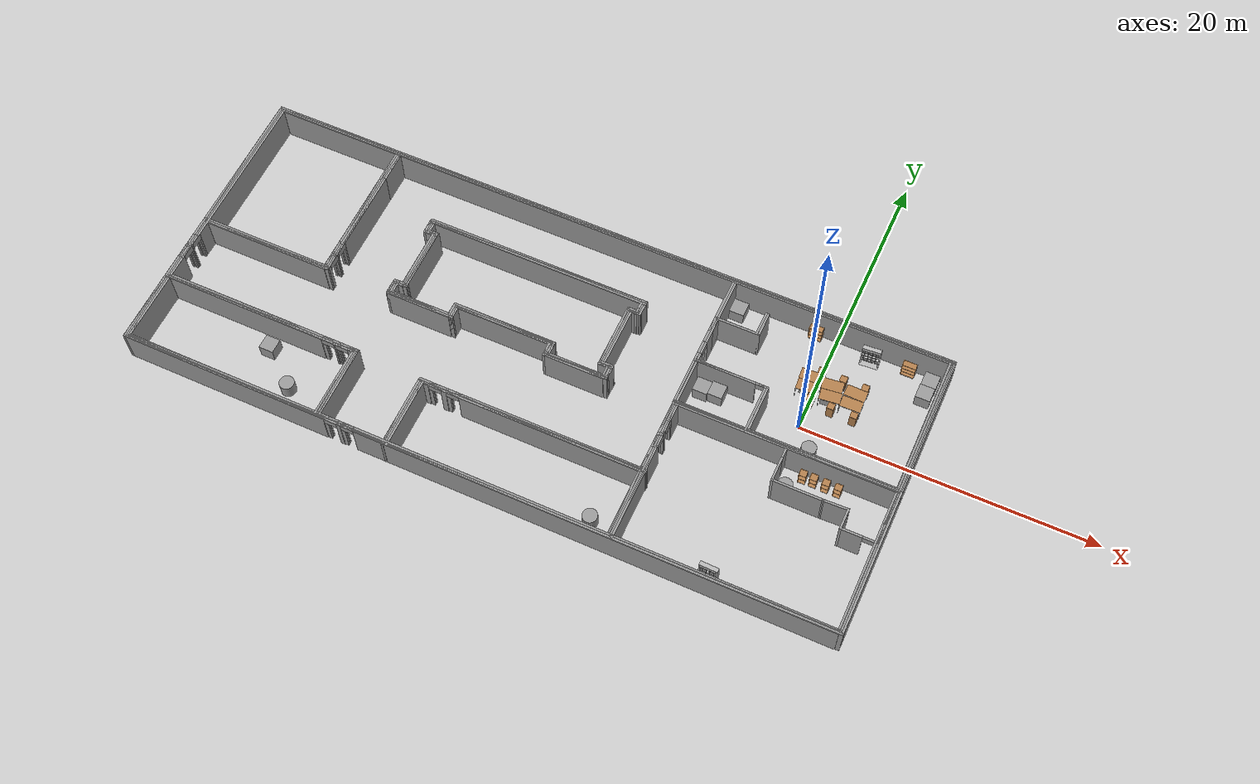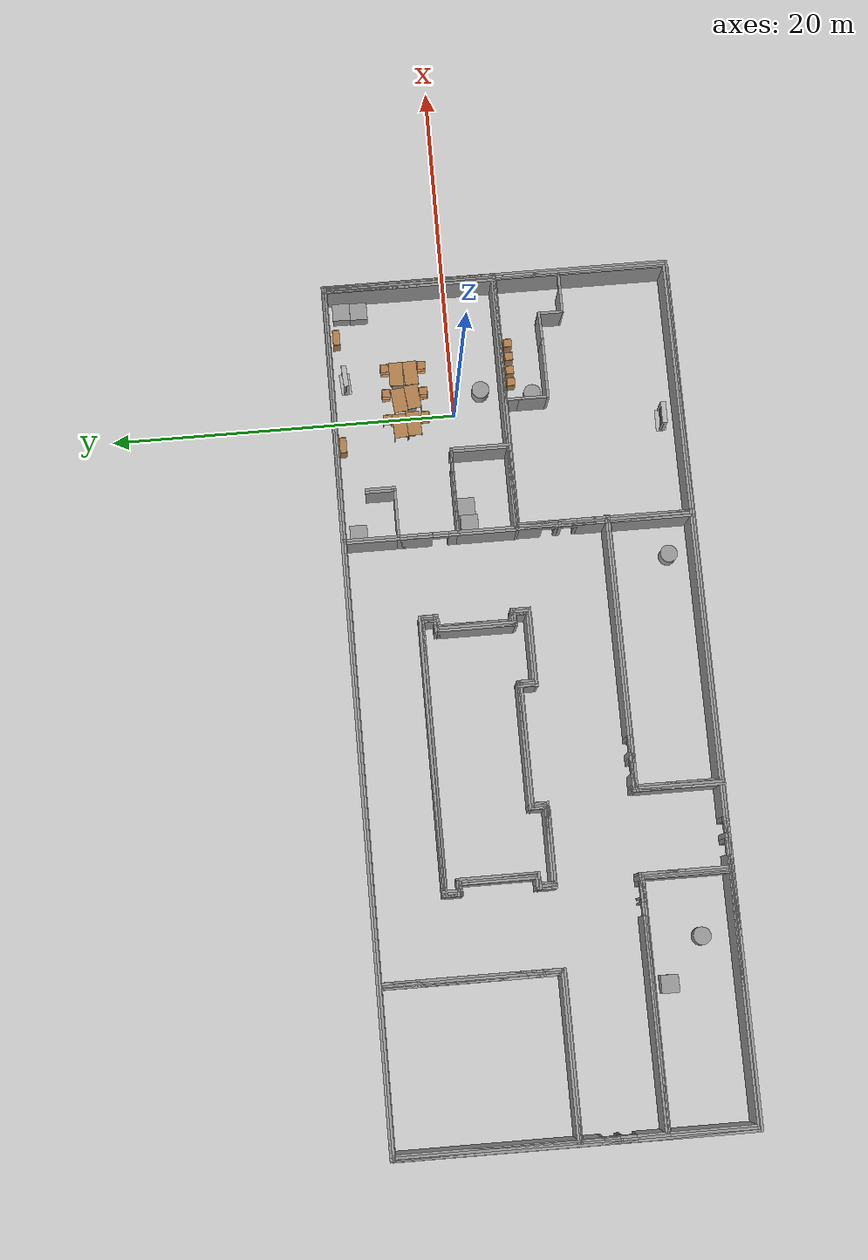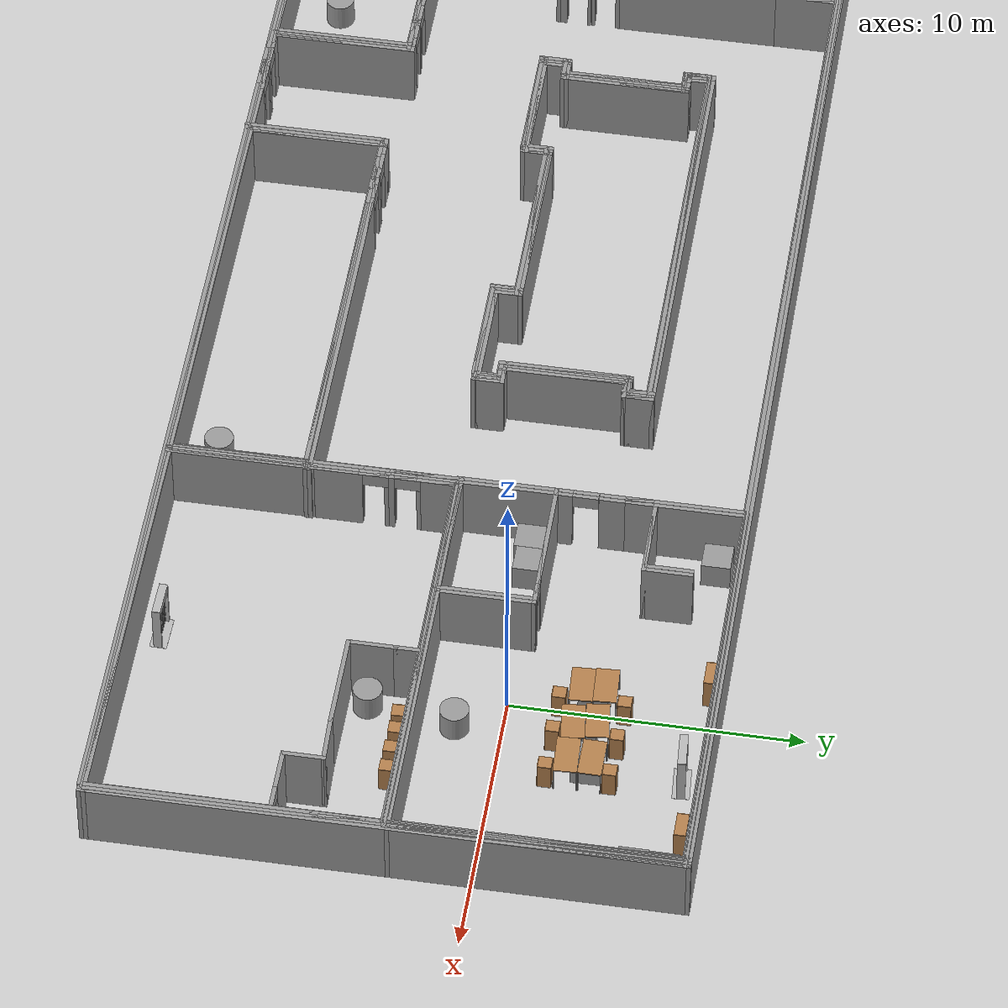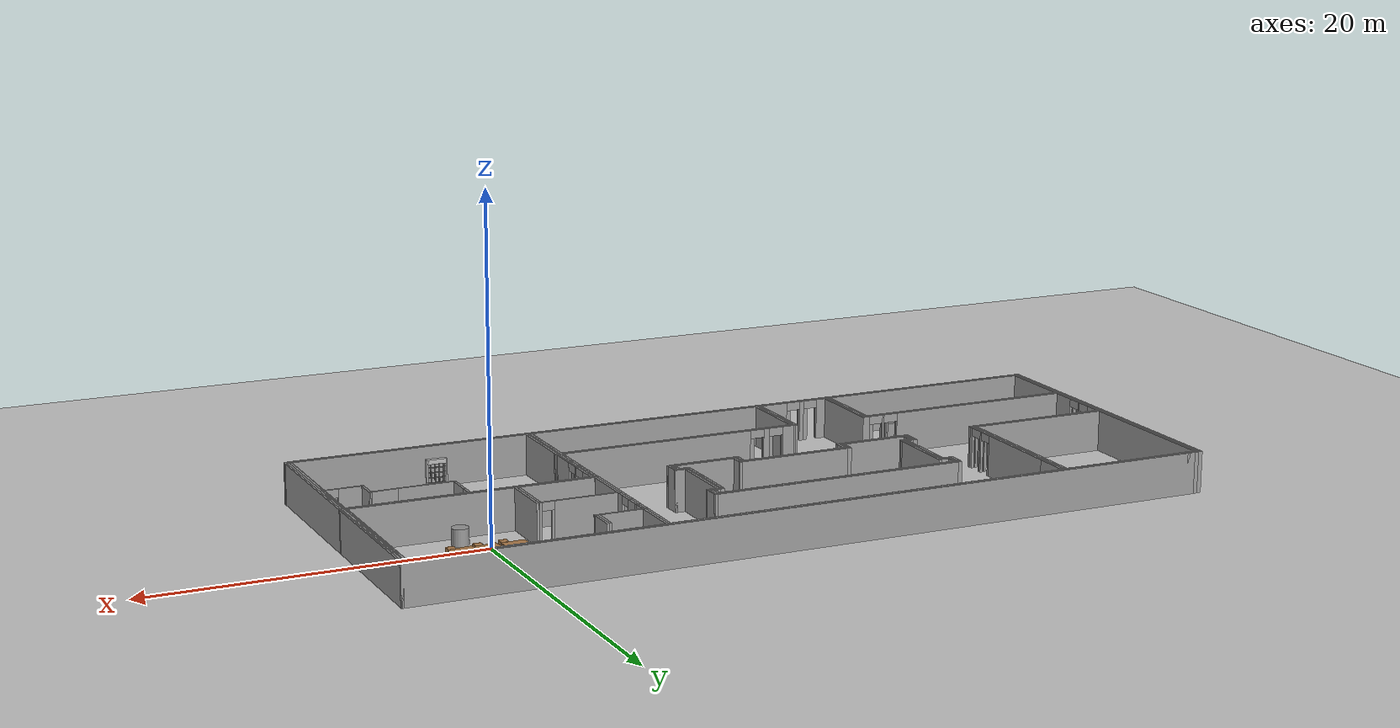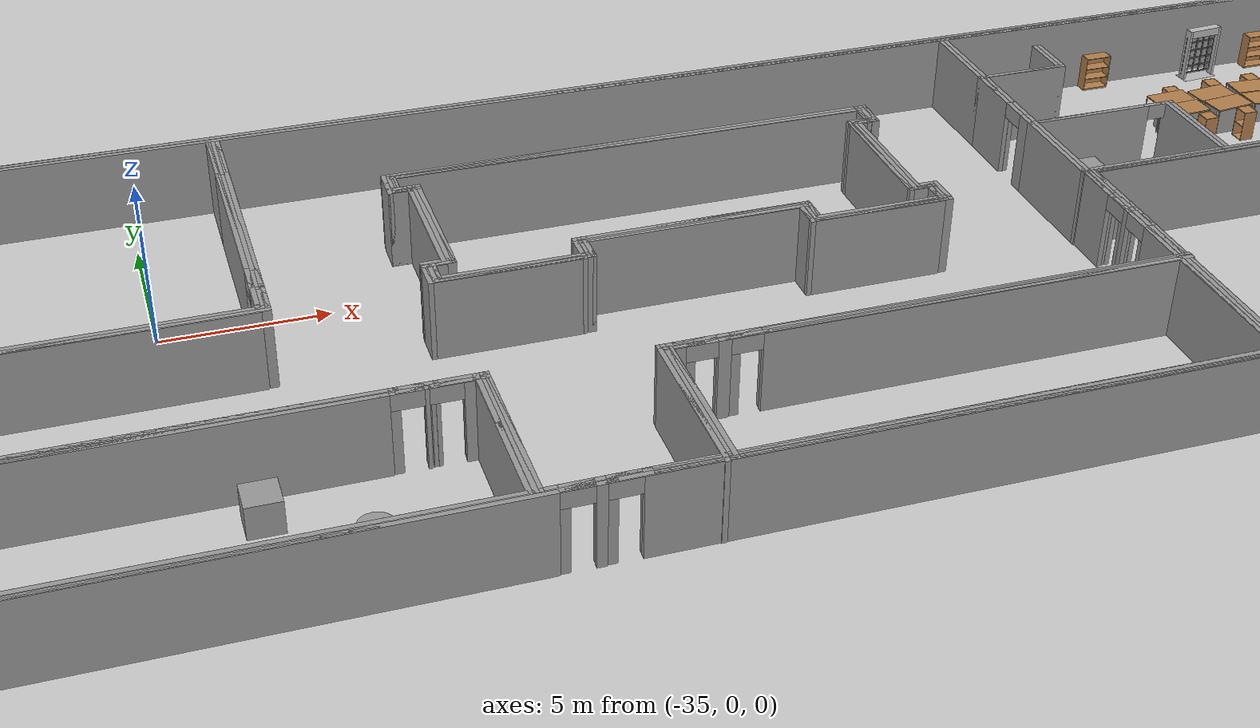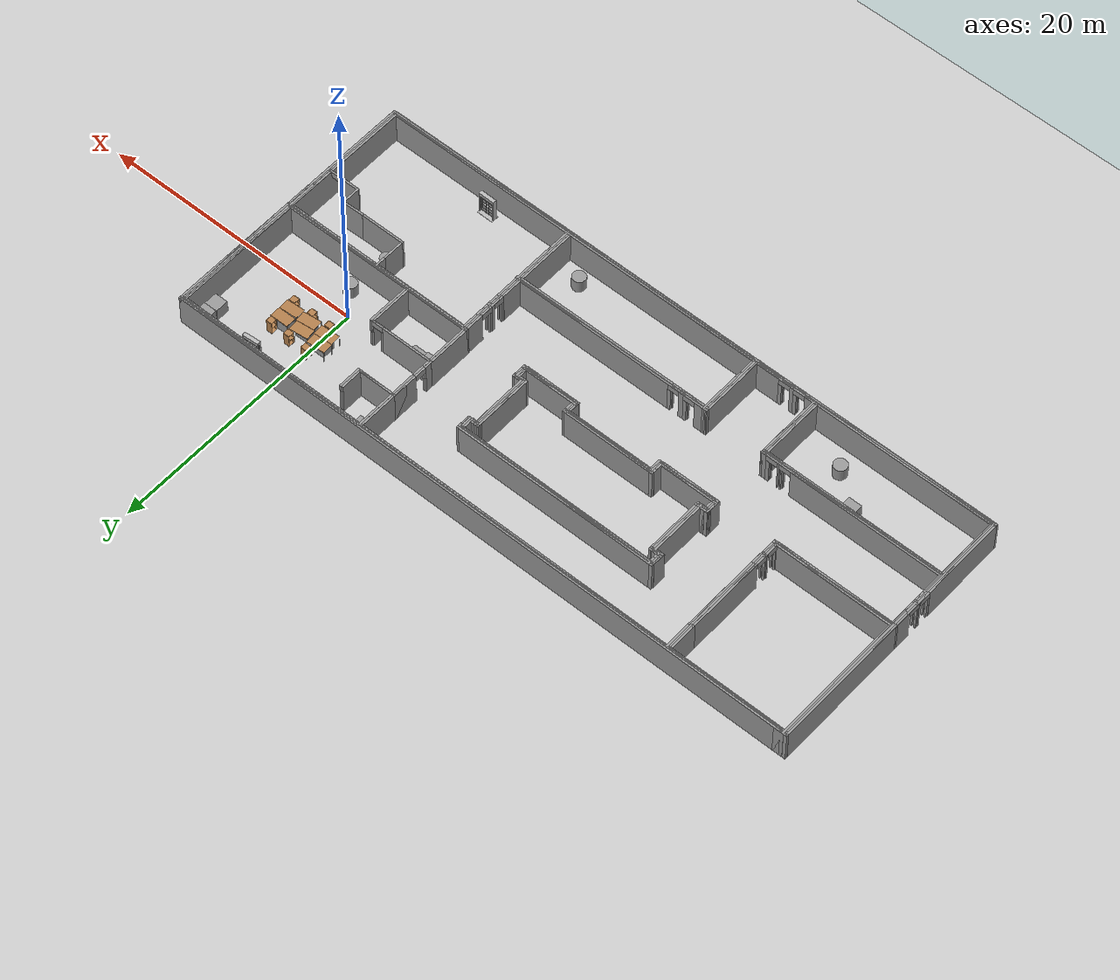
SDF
<sdf version="1.6">
 <world name="default">
  <light name="sun" type="directional">
   <pose>0 0 10 0 -0 0</pose>
   <diffuse>0.8 0.8 0.8 1</diffuse>
   <specular>0.1 0.1 0.1 1</specular>
   <attenuation>
    <range>1000</range>
    <constant>0.9</constant>
    <linear>0.01</linear>
    <quadratic>0.001</quadratic>
   </attenuation>
   <direction>-0.5 0.5 -1</direction>
  </light>
  <model name="ground_plane">
   <static>1</static>
   <link name="link">
    <collision name="collision">
     <geometry><plane><normal>0 0 1</normal><size>100 100</size></plane></geometry>
     <surface><friction><ode><mu>100</mu><mu2>50</mu2></ode></friction></surface>
    </collision>
    <visual name="visual">
     <cast_shadows>0</cast_shadows>
     <geometry><plane><normal>0 0 1</normal><size>100 100</size></plane></geometry>
     <material>
      <script><uri>file://media/materials/scripts/gazebo.material</uri><name>Gazebo/Grey</name></script>
     </material>
    </visual>
   </link>
  </model>
  <gravity>0 0 -9.8</gravity>
  <magnetic_field>6e-06 2.3e-05 -4.2e-05</magnetic_field>
  <atmosphere type="adiabatic"/>
  <physics name="default_physics" default="0" type="ode">
   <max_step_size>0.001</max_step_size>
   <real_time_factor>1</real_time_factor>
   <real_time_update_rate>1000</real_time_update_rate>
  </physics>
  <scene><ambient>0.4 0.4 0.4 1</ambient><background>0.7 0.7 0.7 1</background><shadows>1</shadows></scene>
  <spherical_coordinates>
   <surface_model>EARTH_WGS84</surface_model>
   <latitude_deg>0</latitude_deg>
   <longitude_deg>0</longitude_deg>
   <elevation>0</elevation>
   <heading_deg>0</heading_deg>
  </spherical_coordinates>
  <model name="table_7">
   <static>0</static>
   <link name="link">
    <collision name="surface">
     <pose>0 0 1 0 -0 0</pose>
     <geometry><box><size>1.5 0.8 0.03</size></box></geometry>
     <surface><friction><ode><mu>0.6</mu><mu2>0.6</mu2></ode></friction></surface>
    </collision>
    <visual name="visual1">
     <pose>0 0 1 0 -0 0</pose>
     <geometry><box><size>1.4 0.8 0.04</size></box></geometry>
     <material>
      <script><uri>file://media/materials/scripts/gazebo.material</uri><name>Gazebo/Wood</name></script>
     </material>
    </visual>
    <collision name="front_left_leg">
     <pose>0.68 0.38 0.5 0 -0 0</pose>
     <geometry><cylinder><radius>0.02</radius><length>1</length></cylinder></geometry>
    </collision>
    <visual name="front_left_leg">
     <pose>0.68 0.38 0.5 0 -0 0</pose>
     <geometry><cylinder><radius>0.02</radius><length>1</length></cylinder></geometry>
     <material>
      <script><uri>file://media/materials/scripts/gazebo.material</uri><name>Gazebo/Grey</name></script>
     </material>
    </visual>
    <collision name="front_right_leg">
     <pose>0.68 -0.38 0.5 0 -0 0</pose>
     <geometry><cylinder><radius>0.02</radius><length>1</length></cylinder></geometry>
    </collision>
    <visual name="front_right_leg">
     <pose>0.68 -0.38 0.5 0 -0 0</pose>
     <geometry><cylinder><radius>0.02</radius><length>1</length></cylinder></geometry>
     <material>
      <script><uri>file://media/materials/scripts/gazebo.material</uri><name>Gazebo/Grey</name></script>
     </material>
    </visual>
    <collision name="back_right_leg">
     <pose>-0.68 -0.38 0.5 0 -0 0</pose>
     <geometry><cylinder><radius>0.02</radius><length>1</length></cylinder></geometry>
    </collision>
    <visual name="back_right_leg">
     <pose>-0.68 -0.38 0.5 0 -0 0</pose>
     <geometry><cylinder><radius>0.02</radius><length>1</length></cylinder></geometry>
     <material>
      <script><uri>file://media/materials/scripts/gazebo.material</uri><name>Gazebo/Grey</name></script>
     </material>
    </visual>
    <collision name="back_left_leg">
     <pose>-0.68 0.38 0.5 0 -0 0</pose>
     <geometry><cylinder><radius>0.02</radius><length>1</length></cylinder></geometry>
    </collision>
    <visual name="back_left_leg">
     <pose>-0.68 0.38 0.5 0 -0 0</pose>
     <geometry><cylinder><radius>0.02</radius><length>1</length></cylinder></geometry>
     <material>
      <script><uri>file://media/materials/scripts/gazebo.material</uri><name>Gazebo/Grey</name></script>
     </material>
    </visual>
    <inertial>
     <inertia><ixx>1</ixx><ixy>0</ixy><ixz>0</ixz><iyy>1</iyy><iyz>0</iyz><izz>1</izz></inertia>
     <mass>1</mass>
    </inertial>
   </link>
   <pose>-0.539841 3.25305 0.014986 0 9e-06 0.054108</pose>
  </model>
  <model name="table_7_clone">
   <static>0</static>
   <link name="link">
    <collision name="surface">
     <pose>0 0 1 0 -0 0</pose>
     <geometry><box><size>1.5 0.8 0.03</size></box></geometry>
     <surface><friction><ode><mu>0.6</mu><mu2>0.6</mu2></ode></friction></surface>
    </collision>
    <visual name="visual1">
     <pose>0 0 1 0 -0 0</pose>
     <geometry><box><size>1.4 0.8 0.04</size></box></geometry>
     <material>
      <script><uri>file://media/materials/scripts/gazebo.material</uri><name>Gazebo/Wood</name></script>
     </material>
    </visual>
    <collision name="front_left_leg">
     <pose>0.68 0.38 0.5 0 -0 0</pose>
     <geometry><cylinder><radius>0.02</radius><length>1</length></cylinder></geometry>
    </collision>
    <visual name="front_left_leg">
     <pose>0.68 0.38 0.5 0 -0 0</pose>
     <geometry><cylinder><radius>0.02</radius><length>1</length></cylinder></geometry>
     <material>
      <script><uri>file://media/materials/scripts/gazebo.material</uri><name>Gazebo/Grey</name></script>
     </material>
    </visual>
    <collision name="front_right_leg">
     <pose>0.68 -0.38 0.5 0 -0 0</pose>
     <geometry><cylinder><radius>0.02</radius><length>1</length></cylinder></geometry>
    </collision>
    <visual name="front_right_leg">
     <pose>0.68 -0.38 0.5 0 -0 0</pose>
     <geometry><cylinder><radius>0.02</radius><length>1</length></cylinder></geometry>
     <material>
      <script><uri>file://media/materials/scripts/gazebo.material</uri><name>Gazebo/Grey</name></script>
     </material>
    </visual>
    <collision name="back_right_leg">
     <pose>-0.68 -0.38 0.5 0 -0 0</pose>
     <geometry><cylinder><radius>0.02</radius><length>1</length></cylinder></geometry>
    </collision>
    <visual name="back_right_leg">
     <pose>-0.68 -0.38 0.5 0 -0 0</pose>
     <geometry><cylinder><radius>0.02</radius><length>1</length></cylinder></geometry>
     <material>
      <script><uri>file://media/materials/scripts/gazebo.material</uri><name>Gazebo/Grey</name></script>
     </material>
    </visual>
    <collision name="back_left_leg">
     <pose>-0.68 0.38 0.5 0 -0 0</pose>
     <geometry><cylinder><radius>0.02</radius><length>1</length></cylinder></geometry>
    </collision>
    <visual name="back_left_leg">
     <pose>-0.68 0.38 0.5 0 -0 0</pose>
     <geometry><cylinder><radius>0.02</radius><length>1</length></cylinder></geometry>
     <material>
      <script><uri>file://media/materials/scripts/gazebo.material</uri><name>Gazebo/Grey</name></script>
     </material>
    </visual>
    <inertial>
     <inertia><ixx>1</ixx><ixy>0</ixy><ixz>0</ixz><iyy>1</iyy><iyz>0</iyz><izz>1</izz></inertia>
     <mass>1</mass>
    </inertial>
   </link>
   <pose>-0.46547 2.45586 0.015004 9e-05 6e-06 0.054265</pose>
  </model>
  <model name="table_7_clone_0">
   <static>0</static>
   <link name="link">
    <collision name="surface">
     <pose>0 0 1 0 -0 0</pose>
     <geometry><box><size>1.5 0.8 0.03</size></box></geometry>
     <surface><friction><ode><mu>0.6</mu><mu2>0.6</mu2></ode></friction></surface>
    </collision>
    <visual name="visual1">
     <pose>0 0 1 0 -0 0</pose>
     <geometry><box><size>1.4 0.8 0.04</size></box></geometry>
     <material>
      <script><uri>file://media/materials/scripts/gazebo.material</uri><name>Gazebo/Wood</name></script>
     </material>
    </visual>
    <collision name="front_left_leg">
     <pose>0.68 0.38 0.5 0 -0 0</pose>
     <geometry><cylinder><radius>0.02</radius><length>1</length></cylinder></geometry>
    </collision>
    <visual name="front_left_leg">
     <pose>0.68 0.38 0.5 0 -0 0</pose>
     <geometry><cylinder><radius>0.02</radius><length>1</length></cylinder></geometry>
     <material>
      <script><uri>file://media/materials/scripts/gazebo.material</uri><name>Gazebo/Grey</name></script>
     </material>
    </visual>
    <collision name="front_right_leg">
     <pose>0.68 -0.38 0.5 0 -0 0</pose>
     <geometry><cylinder><radius>0.02</radius><length>1</length></cylinder></geometry>
    </collision>
    <visual name="front_right_leg">
     <pose>0.68 -0.38 0.5 0 -0 0</pose>
     <geometry><cylinder><radius>0.02</radius><length>1</length></cylinder></geometry>
     <material>
      <script><uri>file://media/materials/scripts/gazebo.material</uri><name>Gazebo/Grey</name></script>
     </material>
    </visual>
    <collision name="back_right_leg">
     <pose>-0.68 -0.38 0.5 0 -0 0</pose>
     <geometry><cylinder><radius>0.02</radius><length>1</length></cylinder></geometry>
    </collision>
    <visual name="back_right_leg">
     <pose>-0.68 -0.38 0.5 0 -0 0</pose>
     <geometry><cylinder><radius>0.02</radius><length>1</length></cylinder></geometry>
     <material>
      <script><uri>file://media/materials/scripts/gazebo.material</uri><name>Gazebo/Grey</name></script>
     </material>
    </visual>
    <collision name="back_left_leg">
     <pose>-0.68 0.38 0.5 0 -0 0</pose>
     <geometry><cylinder><radius>0.02</radius><length>1</length></cylinder></geometry>
    </collision>
    <visual name="back_left_leg">
     <pose>-0.68 0.38 0.5 0 -0 0</pose>
     <geometry><cylinder><radius>0.02</radius><length>1</length></cylinder></geometry>
     <material>
      <script><uri>file://media/materials/scripts/gazebo.material</uri><name>Gazebo/Grey</name></script>
     </material>
    </visual>
    <inertial>
     <inertia><ixx>1</ixx><ixy>0</ixy><ixz>0</ixz><iyy>1</iyy><iyz>0</iyz><izz>1</izz></inertia>
     <mass>1</mass>
    </inertial>
   </link>
   <pose>0.985844 3.1842 0.014959 -0.000606 1.8e-05 0.105898</pose>
  </model>
  <model name="table_7_clone_1">
   <static>0</static>
   <link name="link">
    <collision name="surface">
     <pose>0 0 1 0 -0 0</pose>
     <geometry><box><size>1.5 0.8 0.03</size></box></geometry>
     <surface><friction><ode><mu>0.6</mu><mu2>0.6</mu2></ode></friction></surface>
    </collision>
    <visual name="visual1">
     <pose>0 0 1 0 -0 0</pose>
     <geometry><box><size>1.4 0.8 0.04</size></box></geometry>
     <material>
      <script><uri>file://media/materials/scripts/gazebo.material</uri><name>Gazebo/Wood</name></script>
     </material>
    </visual>
    <collision name="front_left_leg">
     <pose>0.68 0.38 0.5 0 -0 0</pose>
     <geometry><cylinder><radius>0.02</radius><length>1</length></cylinder></geometry>
    </collision>
    <visual name="front_left_leg">
     <pose>0.68 0.38 0.5 0 -0 0</pose>
     <geometry><cylinder><radius>0.02</radius><length>1</length></cylinder></geometry>
     <material>
      <script><uri>file://media/materials/scripts/gazebo.material</uri><name>Gazebo/Grey</name></script>
     </material>
    </visual>
    <collision name="front_right_leg">
     <pose>0.68 -0.38 0.5 0 -0 0</pose>
     <geometry><cylinder><radius>0.02</radius><length>1</length></cylinder></geometry>
    </collision>
    <visual name="front_right_leg">
     <pose>0.68 -0.38 0.5 0 -0 0</pose>
     <geometry><cylinder><radius>0.02</radius><length>1</length></cylinder></geometry>
     <material>
      <script><uri>file://media/materials/scripts/gazebo.material</uri><name>Gazebo/Grey</name></script>
     </material>
    </visual>
    <collision name="back_right_leg">
     <pose>-0.68 -0.38 0.5 0 -0 0</pose>
     <geometry><cylinder><radius>0.02</radius><length>1</length></cylinder></geometry>
    </collision>
    <visual name="back_right_leg">
     <pose>-0.68 -0.38 0.5 0 -0 0</pose>
     <geometry><cylinder><radius>0.02</radius><length>1</length></cylinder></geometry>
     <material>
      <script><uri>file://media/materials/scripts/gazebo.material</uri><name>Gazebo/Grey</name></script>
     </material>
    </visual>
    <collision name="back_left_leg">
     <pose>-0.68 0.38 0.5 0 -0 0</pose>
     <geometry><cylinder><radius>0.02</radius><length>1</length></cylinder></geometry>
    </collision>
    <visual name="back_left_leg">
     <pose>-0.68 0.38 0.5 0 -0 0</pose>
     <geometry><cylinder><radius>0.02</radius><length>1</length></cylinder></geometry>
     <material>
      <script><uri>file://media/materials/scripts/gazebo.material</uri><name>Gazebo/Grey</name></script>
     </material>
    </visual>
    <inertial>
     <inertia><ixx>1</ixx><ixy>0</ixy><ixz>0</ixz><iyy>1</iyy><iyz>0</iyz><izz>1</izz></inertia>
     <mass>1</mass>
    </inertial>
   </link>
   <pose>1.1351 2.39038 0.014996 7e-06 3e-06 0.114239</pose>
  </model>
  <model name="bookshelf">
   <static>1</static>
   <link name="link">
    <inertial><mass>1</mass></inertial>
    <collision name="back">
     <pose>0 0.005 0.6 0 -0 0</pose>
     <geometry><box><size>0.9 0.01 1.2</size></box></geometry>
    </collision>
    <visual name="visual1">
     <pose>0 0.005 0.6 0 -0 0</pose>
     <geometry><box><size>0.9 0.01 1.2</size></box></geometry>
     <material>
      <script><uri>file://media/materials/scripts/gazebo.material</uri><name>Gazebo/Wood</name></script>
     </material>
    </visual>
    <collision name="left_side">
     <pose>0.45 -0.195 0.6 0 -0 0</pose>
     <geometry><box><size>0.02 0.4 1.2</size></box></geometry>
    </collision>
    <visual name="visual2">
     <pose>0.45 -0.195 0.6 0 -0 0</pose>
     <geometry><box><size>0.02 0.4 1.2</size></box></geometry>
     <material>
      <script><uri>file://media/materials/scripts/gazebo.material</uri><name>Gazebo/Wood</name></script>
     </material>
    </visual>
    <collision name="right_side">
     <pose>-0.45 -0.195 0.6 0 -0 0</pose>
     <geometry><box><size>0.02 0.4 1.2</size></box></geometry>
    </collision>
    <visual name="visual3">
     <pose>-0.45 -0.195 0.6 0 -0 0</pose>
     <geometry><box><size>0.02 0.4 1.2</size></box></geometry>
     <material>
      <script><uri>file://media/materials/scripts/gazebo.material</uri><name>Gazebo/Wood</name></script>
     </material>
    </visual>
    <collision name="bottom">
     <pose>0 -0.195 0.03 0 -0 0</pose>
     <geometry><box><size>0.88 0.4 0.06</size></box></geometry>
    </collision>
    <visual name="visual4">
     <pose>0 -0.195 0.03 0 -0 0</pose>
     <geometry><box><size>0.88 0.4 0.06</size></box></geometry>
     <material>
      <script><uri>file://media/materials/scripts/gazebo.material</uri><name>Gazebo/Wood</name></script>
     </material>
    </visual>
    <collision name="top">
     <pose>0 -0.195 1.19 0 -0 0</pose>
     <geometry><box><size>0.88 0.4 0.02</size></box></geometry>
    </collision>
    <visual name="visual5">
     <pose>0 -0.195 1.19 0 -0 0</pose>
     <geometry><box><size>0.88 0.4 0.02</size></box></geometry>
     <material>
      <script><uri>file://media/materials/scripts/gazebo.material</uri><name>Gazebo/Wood</name></script>
     </material>
    </visual>
    <collision name="low_shelf">
     <pose>0 -0.195 0.43 0 -0 0</pose>
     <geometry><box><size>0.88 0.4 0.02</size></box></geometry>
    </collision>
    <visual name="visual6">
     <pose>0 -0.195 0.43 0 -0 0</pose>
     <geometry><box><size>0.88 0.4 0.02</size></box></geometry>
     <material>
      <script><uri>file://media/materials/scripts/gazebo.material</uri><name>Gazebo/Wood</name></script>
     </material>
    </visual>
    <collision name="high_shelf">
     <pose>0 -0.195 0.8 0 -0 0</pose>
     <geometry><box><size>0.88 0.4 0.02</size></box></geometry>
    </collision>
    <visual name="visual7">
     <pose>0 -0.195 0.8 0 -0 0</pose>
     <geometry><box><size>0.88 0.4 0.02</size></box></geometry>
     <material>
      <script><uri>file://media/materials/scripts/gazebo.material</uri><name>Gazebo/Wood</name></script>
     </material>
    </visual>
   </link>
   <pose>4.99044 6.73324 0 0 -0 0</pose>
  </model>
  <model name="office_building_0">
   <pose>0.0648 2.0804 0 0 -0 0</pose>
   <link name="Wall_15">
    <collision name="Wall_15_Collision">
     <geometry><box><size>3.25 0.15 2.5</size></box></geometry>
     <pose>0 0 1.25 0 -0 0</pose>
    </collision>
    <visual name="Wall_15_Visual">
     <pose>0 0 1.25 0 -0 0</pose>
     <geometry><box><size>3.25 0.15 2.5</size></box></geometry>
     <material>
      <script><uri>file://media/materials/scripts/gazebo.material</uri><name>Gazebo/Grey</name></script>
      <ambient>1 1 1 1</ambient>
     </material>
    </visual>
    <pose>-7.425 3.375 0 0 0 -1.5708</pose>
   </link>
   <link name="Wall_16">
    <collision name="Wall_16_Collision">
     <geometry><box><size>3 0.15 2.5</size></box></geometry>
     <pose>0 0 1.25 0 -0 0</pose>
    </collision>
    <visual name="Wall_16_Visual">
     <pose>0 0 1.25 0 -0 0</pose>
     <geometry><box><size>3 0.15 2.5</size></box></geometry>
     <material>
      <script><uri>file://media/materials/scripts/gazebo.material</uri><name>Gazebo/Grey</name></script>
      <ambient>1 1 1 1</ambient>
     </material>
    </visual>
    <pose>-6 1.825 0 0 -0 0</pose>
   </link>
   <link name="Wall_17">
    <collision name="Wall_17_Collision">
     <geometry><box><size>1.75 0.15 2.5</size></box></geometry>
     <pose>0 0 1.25 0 -0 0</pose>
    </collision>
    <visual name="Wall_17_Visual">
     <pose>0 0 1.25 0 -0 0</pose>
     <geometry><box><size>1.75 0.15 2.5</size></box></geometry>
     <material>
      <script><uri>file://media/materials/scripts/gazebo.material</uri><name>Gazebo/Grey</name></script>
      <ambient>1 1 1 1</ambient>
     </material>
    </visual>
    <pose>-4.575 2.625 0 0 -0 1.5708</pose>
   </link>
   <link name="Wall_19">
    <collision name="Wall_19_Collision">
     <geometry><box><size>10 0.15 2.5</size></box></geometry>
     <pose>0 0 1.25 0 -0 0</pose>
    </collision>
    <visual name="Wall_19_Visual">
     <pose>0 0 1.25 0 -0 0</pose>
     <geometry><box><size>10 0.15 2.5</size></box></geometry>
     <material>
      <script><uri>file://media/materials/scripts/gazebo.material</uri><name>Gazebo/Grey</name></script>
      <ambient>1 1 1 1</ambient>
     </material>
    </visual>
    <pose>7.425 0 0 0 0 -1.5708</pose>
   </link>
   <link name="Wall_20">
    <collision name="Wall_20_Collision">
     <geometry><box><size>15 0.15 2.5</size></box></geometry>
     <pose>0 0 1.25 0 -0 0</pose>
    </collision>
    <visual name="Wall_20_Visual">
     <pose>0 0 1.25 0 -0 0</pose>
     <geometry><box><size>15 0.15 2.5</size></box></geometry>
     <material>
      <script><uri>file://media/materials/scripts/gazebo.material</uri><name>Gazebo/Grey</name></script>
      <ambient>1 1 1 1</ambient>
     </material>
    </visual>
    <pose>0 -4.925 0 0 -0 3.14159</pose>
   </link>
   <link name="Wall_21">
    <collision name="Wall_21_Collision">
     <geometry><box><size>3.5 0.15 2.5</size></box></geometry>
     <pose>0 0 1.25 0 -0 0</pose>
    </collision>
    <visual name="Wall_21_Visual">
     <pose>0 0 1.25 0 -0 0</pose>
     <geometry><box><size>3.5 0.15 2.5</size></box></geometry>
     <material>
      <script><uri>file://media/materials/scripts/gazebo.material</uri><name>Gazebo/Grey</name></script>
      <ambient>1 1 1 1</ambient>
     </material>
    </visual>
    <pose>-7.425 -3.25 0 0 -0 1.5708</pose>
   </link>
   <link name="Wall_22">
    <pose>-5 -1.575 0 0 -0 0</pose>
    <visual name="Wall_22_Visual_0">
     <pose>-0.454413 0 1.25 0 -0 0</pose>
     <geometry><box><size>4.09117 0.15 2.5</size></box></geometry>
     <material>
      <script><uri>file://media/materials/scripts/gazebo.material</uri><name>Gazebo/Grey</name></script>
      <ambient>1 1 1 1</ambient>
     </material>
    </visual>
    <collision name="Wall_22_Collision_0">
     <geometry><box><size>4.09117 0.15 2.5</size></box></geometry>
     <pose>-0.454413 0 1.25 0 -0 0</pose>
    </collision>
    <visual name="Wall_22_Visual_1">
     <pose>2.49559 0 1.25 0 -0 0</pose>
     <geometry><box><size>0.008827 0.15 2.5</size></box></geometry>
     <material>
      <script><uri>file://media/materials/scripts/gazebo.material</uri><name>Gazebo/Grey</name></script>
      <ambient>1 1 1 1</ambient>
     </material>
    </visual>
    <collision name="Wall_22_Collision_1">
     <geometry><box><size>0.008827 0.15 2.5</size></box></geometry>
     <pose>2.49559 0 1.25 0 -0 0</pose>
    </collision>
    <visual name="Wall_22_Visual_2">
     <pose>2.04117 0 2.25 0 -0 0</pose>
     <geometry><box><size>0.9 0.15 0.5</size></box></geometry>
     <material>
      <script><uri>file://media/materials/scripts/gazebo.material</uri><name>Gazebo/Grey</name></script>
      <ambient>1 1 1 1</ambient>
     </material>
    </visual>
    <collision name="Wall_22_Collision_2">
     <geometry><box><size>0.9 0.15 0.5</size></box></geometry>
     <pose>2.04117 0 2.25 0 -0 0</pose>
    </collision>
   </link>
   <link name="Wall_23">
    <collision name="Wall_23_Collision">
     <geometry><box><size>3.5 0.15 2.5</size></box></geometry>
     <pose>0 0 1.25 0 -0 0</pose>
    </collision>
    <visual name="Wall_23_Visual">
     <pose>0 0 1.25 0 -0 0</pose>
     <geometry><box><size>3.5 0.15 2.5</size></box></geometry>
     <material>
      <script><uri>file://media/materials/scripts/gazebo.material</uri><name>Gazebo/Grey</name></script>
      <ambient>1 1 1 1</ambient>
     </material>
    </visual>
    <pose>-2.575 -3.25 0 0 0 -1.5708</pose>
   </link>
   <link name="Wall_25">
    <pose>-7.425 0.125 0 0 -0 1.5708</pose>
    <visual name="Wall_25_Visual_0">
     <pose>-1.45033 0 1.25 0 -0 0</pose>
     <geometry><box><size>0.649349 0.15 2.5</size></box></geometry>
     <material>
      <script><uri>file://media/materials/scripts/gazebo.material</uri><name>Gazebo/Grey</name></script>
      <ambient>1 1 1 1</ambient>
     </material>
    </visual>
    <collision name="Wall_25_Collision_0">
     <geometry><box><size>0.649349 0.15 2.5</size></box></geometry>
     <pose>-1.45033 0 1.25 0 -0 0</pose>
    </collision>
    <visual name="Wall_25_Visual_1">
     <pose>0.774675 0 1.25 0 -0 0</pose>
     <geometry><box><size>2.00065 0.15 2.5</size></box></geometry>
     <material>
      <script><uri>file://media/materials/scripts/gazebo.material</uri><name>Gazebo/Grey</name></script>
      <ambient>1 1 1 1</ambient>
     </material>
    </visual>
    <collision name="Wall_25_Collision_1">
     <geometry><box><size>2.00065 0.15 2.5</size></box></geometry>
     <pose>0.774675 0 1.25 0 -0 0</pose>
    </collision>
    <visual name="Wall_25_Visual_2">
     <pose>1.21823 0 1.25 0 -0 0</pose>
     <geometry><box><size>1.11353 0.15 2.5</size></box></geometry>
     <material>
      <script><uri>file://media/materials/scripts/gazebo.material</uri><name>Gazebo/Grey</name></script>
      <ambient>1 1 1 1</ambient>
     </material>
    </visual>
    <collision name="Wall_25_Collision_2">
     <geometry><box><size>1.11353 0.15 2.5</size></box></geometry>
     <pose>1.21823 0 1.25 0 -0 0</pose>
    </collision>
    <visual name="Wall_25_Visual_3">
     <pose>-0.682092 0 2.25 0 -0 0</pose>
     <geometry><box><size>0.887117 0.15 0.5</size></box></geometry>
     <material>
      <script><uri>file://media/materials/scripts/gazebo.material</uri><name>Gazebo/Grey</name></script>
      <ambient>1 1 1 1</ambient>
     </material>
    </visual>
    <collision name="Wall_25_Collision_3">
     <geometry><box><size>0.887117 0.15 0.5</size></box></geometry>
     <pose>-0.682092 0 2.25 0 -0 0</pose>
    </collision>
   </link>
   <link name="Wall_4">
    <collision name="Wall_4_Collision">
     <geometry><box><size>15 0.15 2.5</size></box></geometry>
     <pose>0 0 1.25 0 -0 0</pose>
    </collision>
    <visual name="Wall_4_Visual">
     <pose>0 0 1.25 0 -0 0</pose>
     <geometry><box><size>15 0.15 2.5</size></box></geometry>
     <material>
      <script><uri>file://media/materials/scripts/gazebo.material</uri><name>Gazebo/Grey</name></script>
      <ambient>1 1 1 1</ambient>
     </material>
    </visual>
    <pose>0 4.925 0 0 -0 0</pose>
   </link>
   <static>1</static>
  </model>
  <model name="table_7_clone_clone_0">
   <static>0</static>
   <link name="link">
    <collision name="surface">
     <pose>0 0 1 0 -0 0</pose>
     <geometry><box><size>1.5 0.8 0.03</size></box></geometry>
     <surface><friction><ode><mu>0.6</mu><mu2>0.6</mu2></ode></friction></surface>
    </collision>
    <visual name="visual1">
     <pose>0 0 1 0 -0 0</pose>
     <geometry><box><size>1.4 0.8 0.04</size></box></geometry>
     <material>
      <script><uri>file://media/materials/scripts/gazebo.material</uri><name>Gazebo/Wood</name></script>
     </material>
    </visual>
    <collision name="front_left_leg">
     <pose>0.68 0.38 0.5 0 -0 0</pose>
     <geometry><cylinder><radius>0.02</radius><length>1</length></cylinder></geometry>
    </collision>
    <visual name="front_left_leg">
     <pose>0.68 0.38 0.5 0 -0 0</pose>
     <geometry><cylinder><radius>0.02</radius><length>1</length></cylinder></geometry>
     <material>
      <script><uri>file://media/materials/scripts/gazebo.material</uri><name>Gazebo/Grey</name></script>
     </material>
    </visual>
    <collision name="front_right_leg">
     <pose>0.68 -0.38 0.5 0 -0 0</pose>
     <geometry><cylinder><radius>0.02</radius><length>1</length></cylinder></geometry>
    </collision>
    <visual name="front_right_leg">
     <pose>0.68 -0.38 0.5 0 -0 0</pose>
     <geometry><cylinder><radius>0.02</radius><length>1</length></cylinder></geometry>
     <material>
      <script><uri>file://media/materials/scripts/gazebo.material</uri><name>Gazebo/Grey</name></script>
     </material>
    </visual>
    <collision name="back_right_leg">
     <pose>-0.68 -0.38 0.5 0 -0 0</pose>
     <geometry><cylinder><radius>0.02</radius><length>1</length></cylinder></geometry>
    </collision>
    <visual name="back_right_leg">
     <pose>-0.68 -0.38 0.5 0 -0 0</pose>
     <geometry><cylinder><radius>0.02</radius><length>1</length></cylinder></geometry>
     <material>
      <script><uri>file://media/materials/scripts/gazebo.material</uri><name>Gazebo/Grey</name></script>
     </material>
    </visual>
    <collision name="back_left_leg">
     <pose>-0.68 0.38 0.5 0 -0 0</pose>
     <geometry><cylinder><radius>0.02</radius><length>1</length></cylinder></geometry>
    </collision>
    <visual name="back_left_leg">
     <pose>-0.68 0.38 0.5 0 -0 0</pose>
     <geometry><cylinder><radius>0.02</radius><length>1</length></cylinder></geometry>
     <material>
      <script><uri>file://media/materials/scripts/gazebo.material</uri><name>Gazebo/Grey</name></script>
     </material>
    </visual>
    <inertial>
     <inertia><ixx>1</ixx><ixy>0</ixy><ixz>0</ixz><iyy>1</iyy><iyz>0</iyz><izz>1</izz></inertia>
     <mass>1</mass>
    </inertial>
   </link>
   <pose>2.53509 2.3984 0.025611 0.001087 0.030876 0.043374</pose>
  </model>
  <model name="ball_bearing">
   <link name="link">
    <pose>0 0 0.003 0 -0 0</pose>
    <inertial>
     <mass>0.0011</mass>
     <inertia>
      <ixx>3.96e-09</ixx>
      <ixy>0</ixy>
      <ixz>0</ixz>
      <iyy>3.96e-09</iyy>
      <iyz>0</iyz>
      <izz>3.96e-09</izz>
     </inertia>
    </inertial>
    <collision name="collision">
     <geometry><sphere><radius>0.003</radius></sphere></geometry>
     <surface>
      <contact>
       <poissons_ratio>0.305</poissons_ratio>
       <elastic_modulus>2e+11</elastic_modulus>
       <ode><kp>100000</kp><kd>100</kd><max_vel>100</max_vel><min_depth>0.001</min_depth></ode>
      </contact>
      <friction>
       <torsional>
        <coefficient>1</coefficient>
        <use_patch_radius>0</use_patch_radius>
        <surface_radius>0.01</surface_radius>
       </torsional>
      </friction>
     </surface>
    </collision>
    <visual name="visual">
     <geometry><sphere><radius>0.003</radius></sphere></geometry>
     <material>
      <script><uri>file://media/materials/scripts/gazebo.material</uri><name>Gazebo/Grey</name></script>
     </material>
    </visual>
    <velocity_decay><linear>0</linear><angular>0.005</angular></velocity_decay>
   </link>
   <pose>-2.7544 0.153003 -0.001 0 -0 0</pose>
  </model>
  <model name="cabinet">
   <static>1</static>
   <link name="cabinet_bottom_plate">
    <inertial>
     <pose>0 0 -1 0 -0 0</pose>
     <inertia><ixx>2.05</ixx><ixy>0</ixy><ixz>0</ixz><iyy>2.05</iyy><iyz>0</iyz><izz>2.05</izz></inertia>
     <mass>25</mass>
    </inertial>
    <collision name="cabinet_bottom_plate_geom">
     <pose>0 0 0.01 0 -0 0</pose>
     <geometry><box><size>0.45 0.45 0.02</size></box></geometry>
    </collision>
    <visual name="cabinet_bottom_plate_geom_visual">
     <pose>0 0 0.01 0 -0 0</pose>
     <geometry><box><size>0.45 0.45 0.02</size></box></geometry>
     <material>
      <script><uri>file://media/materials/scripts/gazebo.material</uri><name>Gazebo/Wood</name></script>
     </material>
    </visual>
    <collision name="cabinet_bottom_plate_geom_cabinet_back_plate">
     <pose>0.235 0 0.51 0 -0 0</pose>
     <geometry><box><size>0.02 0.45 1.02</size></box></geometry>
    </collision>
    <visual name="cabinet_bottom_plate_geom_cabinet_back_plate_visual">
     <pose>0.235 0 0.51 0 -0 0</pose>
     <geometry><box><size>0.02 0.45 1.02</size></box></geometry>
     <material>
      <script><uri>file://media/materials/scripts/gazebo.material</uri><name>Gazebo/Wood</name></script>
     </material>
    </visual>
    <collision name="cabinet_bottom_plate_geom_cabinet_left_plate">
     <pose>0 0.235 0.51 0 -0 0</pose>
     <geometry><box><size>0.45 0.02 1.02</size></box></geometry>
    </collision>
    <visual name="cabinet_bottom_plate_geom_cabinet_left_plate_visual">
     <pose>0 0.235 0.51 0 -0 0</pose>
     <geometry><box><size>0.45 0.02 1.02</size></box></geometry>
     <material>
      <script><uri>file://media/materials/scripts/gazebo.material</uri><name>Gazebo/Wood</name></script>
     </material>
    </visual>
    <collision name="cabinet_bottom_plate_geom_cabinet_middle_plate">
     <pose>0 0 0.51 0 -0 0</pose>
     <geometry><box><size>0.45 0.45 0.02</size></box></geometry>
    </collision>
    <visual name="cabinet_bottom_plate_geom_cabinet_middle_plate_visual">
     <pose>0 0 0.51 0 -0 0</pose>
     <geometry><box><size>0.45 0.45 0.02</size></box></geometry>
     <material>
      <script><uri>file://media/materials/scripts/gazebo.material</uri><name>Gazebo/Wood</name></script>
     </material>
    </visual>
    <collision name="cabinet_bottom_plate_geom_cabinet_right_plate">
     <pose>0 -0.235 0.51 0 -0 0</pose>
     <geometry><box><size>0.45 0.02 1.02</size></box></geometry>
    </collision>
    <visual name="cabinet_bottom_plate_geom_cabinet_right_plate_visual">
     <pose>0 -0.235 0.51 0 -0 0</pose>
     <geometry><box><size>0.45 0.02 1.02</size></box></geometry>
     <material>
      <script><uri>file://media/materials/scripts/gazebo.material</uri><name>Gazebo/Wood</name></script>
     </material>
    </visual>
    <collision name="cabinet_bottom_plate_geom_cabinet_top_plate">
     <pose>0 0 1.01 0 -0 0</pose>
     <geometry><box><size>0.45 0.45 0.02</size></box></geometry>
    </collision>
    <visual name="cabinet_bottom_plate_geom_cabinet_top_plate_visual">
     <pose>0 0 1.01 0 -0 0</pose>
     <geometry><box><size>0.45 0.45 0.02</size></box></geometry>
     <material>
      <script><uri>file://media/materials/scripts/gazebo.material</uri><name>Gazebo/Wood</name></script>
     </material>
    </visual>
   </link>
   <pose>2.98625 1.73631 0 0 -0 0</pose>
  </model>
  <model name="cabinet_clone">
   <static>1</static>
   <link name="cabinet_bottom_plate">
    <inertial>
     <pose>0 0 -1 0 -0 0</pose>
     <inertia><ixx>2.05</ixx><ixy>0</ixy><ixz>0</ixz><iyy>2.05</iyy><iyz>0</iyz><izz>2.05</izz></inertia>
     <mass>25</mass>
    </inertial>
    <collision name="cabinet_bottom_plate_geom">
     <pose>0 0 0.01 0 -0 0</pose>
     <geometry><box><size>0.45 0.45 0.02</size></box></geometry>
    </collision>
    <visual name="cabinet_bottom_plate_geom_visual">
     <pose>0 0 0.01 0 -0 0</pose>
     <geometry><box><size>0.45 0.45 0.02</size></box></geometry>
     <material>
      <script><uri>file://media/materials/scripts/gazebo.material</uri><name>Gazebo/Wood</name></script>
     </material>
    </visual>
    <collision name="cabinet_bottom_plate_geom_cabinet_back_plate">
     <pose>0.235 0 0.51 0 -0 0</pose>
     <geometry><box><size>0.02 0.45 1.02</size></box></geometry>
    </collision>
    <visual name="cabinet_bottom_plate_geom_cabinet_back_plate_visual">
     <pose>0.235 0 0.51 0 -0 0</pose>
     <geometry><box><size>0.02 0.45 1.02</size></box></geometry>
     <material>
      <script><uri>file://media/materials/scripts/gazebo.material</uri><name>Gazebo/Wood</name></script>
     </material>
    </visual>
    <collision name="cabinet_bottom_plate_geom_cabinet_left_plate">
     <pose>0 0.235 0.51 0 -0 0</pose>
     <geometry><box><size>0.45 0.02 1.02</size></box></geometry>
    </collision>
    <visual name="cabinet_bottom_plate_geom_cabinet_left_plate_visual">
     <pose>0 0.235 0.51 0 -0 0</pose>
     <geometry><box><size>0.45 0.02 1.02</size></box></geometry>
     <material>
      <script><uri>file://media/materials/scripts/gazebo.material</uri><name>Gazebo/Wood</name></script>
     </material>
    </visual>
    <collision name="cabinet_bottom_plate_geom_cabinet_middle_plate">
     <pose>0 0 0.51 0 -0 0</pose>
     <geometry><box><size>0.45 0.45 0.02</size></box></geometry>
    </collision>
    <visual name="cabinet_bottom_plate_geom_cabinet_middle_plate_visual">
     <pose>0 0 0.51 0 -0 0</pose>
     <geometry><box><size>0.45 0.45 0.02</size></box></geometry>
     <material>
      <script><uri>file://media/materials/scripts/gazebo.material</uri><name>Gazebo/Wood</name></script>
     </material>
    </visual>
    <collision name="cabinet_bottom_plate_geom_cabinet_right_plate">
     <pose>0 -0.235 0.51 0 -0 0</pose>
     <geometry><box><size>0.45 0.02 1.02</size></box></geometry>
    </collision>
    <visual name="cabinet_bottom_plate_geom_cabinet_right_plate_visual">
     <pose>0 -0.235 0.51 0 -0 0</pose>
     <geometry><box><size>0.45 0.02 1.02</size></box></geometry>
     <material>
      <script><uri>file://media/materials/scripts/gazebo.material</uri><name>Gazebo/Wood</name></script>
     </material>
    </visual>
    <collision name="cabinet_bottom_plate_geom_cabinet_top_plate">
     <pose>0 0 1.01 0 -0 0</pose>
     <geometry><box><size>0.45 0.45 0.02</size></box></geometry>
    </collision>
    <visual name="cabinet_bottom_plate_geom_cabinet_top_plate_visual">
     <pose>0 0 1.01 0 -0 0</pose>
     <geometry><box><size>0.45 0.45 0.02</size></box></geometry>
     <material>
      <script><uri>file://media/materials/scripts/gazebo.material</uri><name>Gazebo/Wood</name></script>
     </material>
    </visual>
   </link>
   <pose>1.43128 1.75091 0 0 -0 0</pose>
  </model>
  <model name="cabinet_clone_1">
   <static>1</static>
   <link name="cabinet_bottom_plate">
    <inertial>
     <pose>0 0 -1 0 -0 0</pose>
     <inertia><ixx>2.05</ixx><ixy>0</ixy><ixz>0</ixz><iyy>2.05</iyy><iyz>0</iyz><izz>2.05</izz></inertia>
     <mass>25</mass>
    </inertial>
    <collision name="cabinet_bottom_plate_geom">
     <pose>0 0 0.01 0 -0 0</pose>
     <geometry><box><size>0.45 0.45 0.02</size></box></geometry>
    </collision>
    <visual name="cabinet_bottom_plate_geom_visual">
     <pose>0 0 0.01 0 -0 0</pose>
     <geometry><box><size>0.45 0.45 0.02</size></box></geometry>
     <material>
      <script><uri>file://media/materials/scripts/gazebo.material</uri><name>Gazebo/Wood</name></script>
     </material>
    </visual>
    <collision name="cabinet_bottom_plate_geom_cabinet_back_plate">
     <pose>0.235 0 0.51 0 -0 0</pose>
     <geometry><box><size>0.02 0.45 1.02</size></box></geometry>
    </collision>
    <visual name="cabinet_bottom_plate_geom_cabinet_back_plate_visual">
     <pose>0.235 0 0.51 0 -0 0</pose>
     <geometry><box><size>0.02 0.45 1.02</size></box></geometry>
     <material>
      <script><uri>file://media/materials/scripts/gazebo.material</uri><name>Gazebo/Wood</name></script>
     </material>
    </visual>
    <collision name="cabinet_bottom_plate_geom_cabinet_left_plate">
     <pose>0 0.235 0.51 0 -0 0</pose>
     <geometry><box><size>0.45 0.02 1.02</size></box></geometry>
    </collision>
    <visual name="cabinet_bottom_plate_geom_cabinet_left_plate_visual">
     <pose>0 0.235 0.51 0 -0 0</pose>
     <geometry><box><size>0.45 0.02 1.02</size></box></geometry>
     <material>
      <script><uri>file://media/materials/scripts/gazebo.material</uri><name>Gazebo/Wood</name></script>
     </material>
    </visual>
    <collision name="cabinet_bottom_plate_geom_cabinet_middle_plate">
     <pose>0 0 0.51 0 -0 0</pose>
     <geometry><box><size>0.45 0.45 0.02</size></box></geometry>
    </collision>
    <visual name="cabinet_bottom_plate_geom_cabinet_middle_plate_visual">
     <pose>0 0 0.51 0 -0 0</pose>
     <geometry><box><size>0.45 0.45 0.02</size></box></geometry>
     <material>
      <script><uri>file://media/materials/scripts/gazebo.material</uri><name>Gazebo/Wood</name></script>
     </material>
    </visual>
    <collision name="cabinet_bottom_plate_geom_cabinet_right_plate">
     <pose>0 -0.235 0.51 0 -0 0</pose>
     <geometry><box><size>0.45 0.02 1.02</size></box></geometry>
    </collision>
    <visual name="cabinet_bottom_plate_geom_cabinet_right_plate_visual">
     <pose>0 -0.235 0.51 0 -0 0</pose>
     <geometry><box><size>0.45 0.02 1.02</size></box></geometry>
     <material>
      <script><uri>file://media/materials/scripts/gazebo.material</uri><name>Gazebo/Wood</name></script>
     </material>
    </visual>
    <collision name="cabinet_bottom_plate_geom_cabinet_top_plate">
     <pose>0 0 1.01 0 -0 0</pose>
     <geometry><box><size>0.45 0.45 0.02</size></box></geometry>
    </collision>
    <visual name="cabinet_bottom_plate_geom_cabinet_top_plate_visual">
     <pose>0 0 1.01 0 -0 0</pose>
     <geometry><box><size>0.45 0.45 0.02</size></box></geometry>
     <material>
      <script><uri>file://media/materials/scripts/gazebo.material</uri><name>Gazebo/Wood</name></script>
     </material>
    </visual>
   </link>
   <pose>2.9573 3.88305 0 0 -0 0</pose>
  </model>
  <model name="cabinet_clone_3">
   <static>1</static>
   <link name="cabinet_bottom_plate">
    <inertial>
     <pose>0 0 -1 0 -0 0</pose>
     <inertia><ixx>2.05</ixx><ixy>0</ixy><ixz>0</ixz><iyy>2.05</iyy><iyz>0</iyz><izz>2.05</izz></inertia>
     <mass>25</mass>
    </inertial>
    <collision name="cabinet_bottom_plate_geom">
     <pose>0 0 0.01 0 -0 0</pose>
     <geometry><box><size>0.45 0.45 0.02</size></box></geometry>
    </collision>
    <visual name="cabinet_bottom_plate_geom_visual">
     <pose>0 0 0.01 0 -0 0</pose>
     <geometry><box><size>0.45 0.45 0.02</size></box></geometry>
     <material>
      <script><uri>file://media/materials/scripts/gazebo.material</uri><name>Gazebo/Wood</name></script>
     </material>
    </visual>
    <collision name="cabinet_bottom_plate_geom_cabinet_back_plate">
     <pose>0.235 0 0.51 0 -0 0</pose>
     <geometry><box><size>0.02 0.45 1.02</size></box></geometry>
    </collision>
    <visual name="cabinet_bottom_plate_geom_cabinet_back_plate_visual">
     <pose>0.235 0 0.51 0 -0 0</pose>
     <geometry><box><size>0.02 0.45 1.02</size></box></geometry>
     <material>
      <script><uri>file://media/materials/scripts/gazebo.material</uri><name>Gazebo/Wood</name></script>
     </material>
    </visual>
    <collision name="cabinet_bottom_plate_geom_cabinet_left_plate">
     <pose>0 0.235 0.51 0 -0 0</pose>
     <geometry><box><size>0.45 0.02 1.02</size></box></geometry>
    </collision>
    <visual name="cabinet_bottom_plate_geom_cabinet_left_plate_visual">
     <pose>0 0.235 0.51 0 -0 0</pose>
     <geometry><box><size>0.45 0.02 1.02</size></box></geometry>
     <material>
      <script><uri>file://media/materials/scripts/gazebo.material</uri><name>Gazebo/Wood</name></script>
     </material>
    </visual>
    <collision name="cabinet_bottom_plate_geom_cabinet_middle_plate">
     <pose>0 0 0.51 0 -0 0</pose>
     <geometry><box><size>0.45 0.45 0.02</size></box></geometry>
    </collision>
    <visual name="cabinet_bottom_plate_geom_cabinet_middle_plate_visual">
     <pose>0 0 0.51 0 -0 0</pose>
     <geometry><box><size>0.45 0.45 0.02</size></box></geometry>
     <material>
      <script><uri>file://media/materials/scripts/gazebo.material</uri><name>Gazebo/Wood</name></script>
     </material>
    </visual>
    <collision name="cabinet_bottom_plate_geom_cabinet_right_plate">
     <pose>0 -0.235 0.51 0 -0 0</pose>
     <geometry><box><size>0.45 0.02 1.02</size></box></geometry>
    </collision>
    <visual name="cabinet_bottom_plate_geom_cabinet_right_plate_visual">
     <pose>0 -0.235 0.51 0 -0 0</pose>
     <geometry><box><size>0.45 0.02 1.02</size></box></geometry>
     <material>
      <script><uri>file://media/materials/scripts/gazebo.material</uri><name>Gazebo/Wood</name></script>
     </material>
    </visual>
    <collision name="cabinet_bottom_plate_geom_cabinet_top_plate">
     <pose>0 0 1.01 0 -0 0</pose>
     <geometry><box><size>0.45 0.45 0.02</size></box></geometry>
    </collision>
    <visual name="cabinet_bottom_plate_geom_cabinet_top_plate_visual">
     <pose>0 0 1.01 0 -0 0</pose>
     <geometry><box><size>0.45 0.45 0.02</size></box></geometry>
     <material>
      <script><uri>file://media/materials/scripts/gazebo.material</uri><name>Gazebo/Wood</name></script>
     </material>
    </visual>
   </link>
   <pose>-0.048273 3.95202 -0.089414 0 -0 0</pose>
  </model>
  <model name="build1">
   <pose>-16.9008 -2.95936 0 0 -0 0</pose>
   <link name="Wall_0">
    <collision name="Wall_0_Collision">
     <geometry><box><size>48.75 0.15 2.5</size></box></geometry>
     <pose>0 0 1.25 0 -0 0</pose>
    </collision>
    <visual name="Wall_0_Visual">
     <pose>0 0 1.25 0 -0 0</pose>
     <geometry><box><size>48.75 0.15 2.5</size></box></geometry>
     <material>
      <script><uri>file://media/materials/scripts/gazebo.material</uri><name>Gazebo/Grey</name></script>
      <ambient>1 1 1 1</ambient>
     </material>
    </visual>
    <pose>0.128151 9.93761 0 0 -0 0</pose>
   </link>
   <link name="Wall_10">
    <collision name="Wall_10_Collision">
     <geometry><box><size>0.75 0.15 2.5</size></box></geometry>
     <pose>0 0 1.25 0 -0 0</pose>
    </collision>
    <visual name="Wall_10_Visual">
     <pose>0 0 1.25 0 -0 0</pose>
     <geometry><box><size>0.75 0.15 2.5</size></box></geometry>
     <material>
      <script><uri>file://media/materials/scripts/gazebo.material</uri><name>Gazebo/Grey</name></script>
      <ambient>1 1 1 1</ambient>
     </material>
    </visual>
    <pose>-24.1218 9.93761 0 0 -0 0</pose>
   </link>
   <link name="Wall_101">
    <collision name="Wall_101_Collision">
     <geometry><box><size>10 0.15 2.5</size></box></geometry>
     <pose>0 0 1.25 0 -0 0</pose>
    </collision>
    <visual name="Wall_101_Visual">
     <pose>0 0 1.25 0 -0 0</pose>
     <geometry><box><size>10 0.15 2.5</size></box></geometry>
     <material>
      <script><uri>file://media/materials/scripts/gazebo.material</uri><name>Gazebo/Grey</name></script>
      <ambient>1 1 1 1</ambient>
     </material>
    </visual>
    <pose>24.4281 5.01261 0 0 0 -1.5708</pose>
   </link>
   <link name="Wall_102">
    <collision name="Wall_102_Collision">
     <geometry><box><size>15 0.15 2.5</size></box></geometry>
     <pose>0 0 1.25 0 -0 0</pose>
    </collision>
    <visual name="Wall_102_Visual">
     <pose>0 0 1.25 0 -0 0</pose>
     <geometry><box><size>15 0.15 2.5</size></box></geometry>
     <material>
      <script><uri>file://media/materials/scripts/gazebo.material</uri><name>Gazebo/Grey</name></script>
      <ambient>1 1 1 1</ambient>
     </material>
    </visual>
    <pose>17.0032 0.087612 0 0 -0 3.14159</pose>
   </link>
   <link name="Wall_103">
    <pose>9.57815 -2.46239 0 0 0 -1.5708</pose>
    <visual name="Wall_103_Visual_0">
     <pose>-1.90662 0 1.25 0 -0 0</pose>
     <geometry><box><size>1.43676 0.15 2.5</size></box></geometry>
     <material>
      <script><uri>file://media/materials/scripts/gazebo.material</uri><name>Gazebo/Grey</name></script>
      <ambient>1 1 1 1</ambient>
     </material>
    </visual>
    <collision name="Wall_103_Collision_0">
     <geometry><box><size>1.43676 0.15 2.5</size></box></geometry>
     <pose>-1.90662 0 1.25 0 -0 0</pose>
    </collision>
    <visual name="Wall_103_Visual_1">
     <pose>-0.188989 0 1.25 0 -0 0</pose>
     <geometry><box><size>0.198503 0.15 2.5</size></box></geometry>
     <material>
      <script><uri>file://media/materials/scripts/gazebo.material</uri><name>Gazebo/Grey</name></script>
      <ambient>1 1 1 1</ambient>
     </material>
    </visual>
    <collision name="Wall_103_Collision_1">
     <geometry><box><size>0.198503 0.15 2.5</size></box></geometry>
     <pose>-0.188989 0 1.25 0 -0 0</pose>
    </collision>
    <visual name="Wall_103_Visual_2">
     <pose>1.71763 0 1.25 0 -0 0</pose>
     <geometry><box><size>1.81474 0.15 2.5</size></box></geometry>
     <material>
      <script><uri>file://media/materials/scripts/gazebo.material</uri><name>Gazebo/Grey</name></script>
      <ambient>1 1 1 1</ambient>
     </material>
    </visual>
    <collision name="Wall_103_Collision_2">
     <geometry><box><size>1.81474 0.15 2.5</size></box></geometry>
     <pose>1.71763 0 1.25 0 -0 0</pose>
    </collision>
    <visual name="Wall_103_Visual_3">
     <pose>-0.73824 0 2.25 0 -0 0</pose>
     <geometry><box><size>0.9 0.15 0.5</size></box></geometry>
     <material>
      <script><uri>file://media/materials/scripts/gazebo.material</uri><name>Gazebo/Grey</name></script>
      <ambient>1 1 1 1</ambient>
     </material>
    </visual>
    <collision name="Wall_103_Collision_3">
     <geometry><box><size>0.9 0.15 0.5</size></box></geometry>
     <pose>-0.73824 0 2.25 0 -0 0</pose>
    </collision>
    <visual name="Wall_103_Visual_4">
     <pose>0.360263 0 2.25 0 -0 0</pose>
     <geometry><box><size>0.9 0.15 0.5</size></box></geometry>
     <material>
      <script><uri>file://media/materials/scripts/gazebo.material</uri><name>Gazebo/Grey</name></script>
      <ambient>1 1 1 1</ambient>
     </material>
    </visual>
    <collision name="Wall_103_Collision_4">
     <geometry><box><size>0.9 0.15 0.5</size></box></geometry>
     <pose>0.360263 0 2.25 0 -0 0</pose>
    </collision>
   </link>
   <link name="Wall_105">
    <pose>1.96209 -5.08761 0 0 -0 0</pose>
    <visual name="Wall_105_Visual_0">
     <pose>-7.37124 0 1.25 0 -0 0</pose>
     <geometry><box><size>0.757518 0.15 2.5</size></box></geometry>
     <material>
      <script><uri>file://media/materials/scripts/gazebo.material</uri><name>Gazebo/Grey</name></script>
      <ambient>1 1 1 1</ambient>
     </material>
    </visual>
    <collision name="Wall_105_Collision_0">
     <geometry><box><size>0.757518 0.15 2.5</size></box></geometry>
     <pose>-7.37124 0 1.25 0 -0 0</pose>
    </collision>
    <visual name="Wall_105_Visual_1">
     <pose>-5.91186 0 1.25 0 -0 0</pose>
     <geometry><box><size>0.361245 0.15 2.5</size></box></geometry>
     <material>
      <script><uri>file://media/materials/scripts/gazebo.material</uri><name>Gazebo/Grey</name></script>
      <ambient>1 1 1 1</ambient>
     </material>
    </visual>
    <collision name="Wall_105_Collision_1">
     <geometry><box><size>0.361245 0.15 2.5</size></box></geometry>
     <pose>-5.91186 0 1.25 0 -0 0</pose>
    </collision>
    <visual name="Wall_105_Visual_2">
     <pose>1.45938 0 1.25 0 -0 0</pose>
     <geometry><box><size>12.5812 0.15 2.5</size></box></geometry>
     <material>
      <script><uri>file://media/materials/scripts/gazebo.material</uri><name>Gazebo/Grey</name></script>
      <ambient>1 1 1 1</ambient>
     </material>
    </visual>
    <collision name="Wall_105_Collision_2">
     <geometry><box><size>12.5812 0.15 2.5</size></box></geometry>
     <pose>1.45938 0 1.25 0 -0 0</pose>
    </collision>
    <visual name="Wall_105_Visual_3">
     <pose>-6.54248 0 2.25 0 -0 0</pose>
     <geometry><box><size>0.9 0.15 0.5</size></box></geometry>
     <material>
      <script><uri>file://media/materials/scripts/gazebo.material</uri><name>Gazebo/Grey</name></script>
      <ambient>1 1 1 1</ambient>
     </material>
    </visual>
    <collision name="Wall_105_Collision_3">
     <geometry><box><size>0.9 0.15 0.5</size></box></geometry>
     <pose>-6.54248 0 2.25 0 -0 0</pose>
    </collision>
    <visual name="Wall_105_Visual_4">
     <pose>-5.28124 0 2.25 0 -0 0</pose>
     <geometry><box><size>0.9 0.15 0.5</size></box></geometry>
     <material>
      <script><uri>file://media/materials/scripts/gazebo.material</uri><name>Gazebo/Grey</name></script>
      <ambient>1 1 1 1</ambient>
     </material>
    </visual>
    <collision name="Wall_105_Collision_4">
     <geometry><box><size>0.9 0.15 0.5</size></box></geometry>
     <pose>-5.28124 0 2.25 0 -0 0</pose>
    </collision>
   </link>
   <link name="Wall_14">
    <collision name="Wall_14_Collision">
     <geometry><box><size>9.25 0.15 2.5</size></box></geometry>
     <pose>0 0 1.25 0 -0 0</pose>
    </collision>
    <visual name="Wall_14_Visual">
     <pose>0 0 1.25 0 -0 0</pose>
     <geometry><box><size>9.25 0.15 2.5</size></box></geometry>
     <material>
      <script><uri>file://media/materials/scripts/gazebo.material</uri><name>Gazebo/Grey</name></script>
      <ambient>1 1 1 1</ambient>
     </material>
    </visual>
    <pose>-19.8782 -0.176763 0 0 -0 3.14159</pose>
   </link>
   <link name="Wall_16">
    <pose>-15.3282 3.74824 0 0 -0 1.5708</pose>
    <visual name="Wall_16_Visual_0">
     <pose>-3.87767 0 1.25 0 -0 0</pose>
     <geometry><box><size>0.244662 0.15 2.5</size></box></geometry>
     <material>
      <script><uri>file://media/materials/scripts/gazebo.material</uri><name>Gazebo/Grey</name></script>
      <ambient>1 1 1 1</ambient>
     </material>
    </visual>
    <collision name="Wall_16_Collision_0">
     <geometry><box><size>0.244662 0.15 2.5</size></box></geometry>
     <pose>-3.87767 0 1.25 0 -0 0</pose>
    </collision>
    <visual name="Wall_16_Visual_1">
     <pose>-2.79773 0 1.25 0 -0 0</pose>
     <geometry><box><size>0.11521 0.15 2.5</size></box></geometry>
     <material>
      <script><uri>file://media/materials/scripts/gazebo.material</uri><name>Gazebo/Grey</name></script>
      <ambient>1 1 1 1</ambient>
     </material>
    </visual>
    <collision name="Wall_16_Collision_1">
     <geometry><box><size>0.11521 0.15 2.5</size></box></geometry>
     <pose>-2.79773 0 1.25 0 -0 0</pose>
    </collision>
    <visual name="Wall_16_Visual_2">
     <pose>1.07994 0 1.25 0 -0 0</pose>
     <geometry><box><size>5.84013 0.15 2.5</size></box></geometry>
     <material>
      <script><uri>file://media/materials/scripts/gazebo.material</uri><name>Gazebo/Grey</name></script>
      <ambient>1 1 1 1</ambient>
     </material>
    </visual>
    <collision name="Wall_16_Collision_2">
     <geometry><box><size>5.84013 0.15 2.5</size></box></geometry>
     <pose>1.07994 0 1.25 0 -0 0</pose>
    </collision>
    <visual name="Wall_16_Visual_3">
     <pose>-3.30534 0 2.25 0 -0 0</pose>
     <geometry><box><size>0.9 0.15 0.5</size></box></geometry>
     <material>
      <script><uri>file://media/materials/scripts/gazebo.material</uri><name>Gazebo/Grey</name></script>
      <ambient>1 1 1 1</ambient>
     </material>
    </visual>
    <collision name="Wall_16_Collision_3">
     <geometry><box><size>0.9 0.15 0.5</size></box></geometry>
     <pose>-3.30534 0 2.25 0 -0 0</pose>
    </collision>
    <visual name="Wall_16_Visual_4">
     <pose>-2.29013 0 2.25 0 -0 0</pose>
     <geometry><box><size>0.9 0.15 0.5</size></box></geometry>
     <material>
      <script><uri>file://media/materials/scripts/gazebo.material</uri><name>Gazebo/Grey</name></script>
      <ambient>1 1 1 1</ambient>
     </material>
    </visual>
    <collision name="Wall_16_Collision_4">
     <geometry><box><size>0.9 0.15 0.5</size></box></geometry>
     <pose>-2.29013 0 2.25 0 -0 0</pose>
    </collision>
   </link>
   <link name="Wall_19">
    <collision name="Wall_19_Collision">
     <geometry><box><size>2.25 0.15 2.5</size></box></geometry>
     <pose>0 0 1.25 0 -0 0</pose>
    </collision>
    <visual name="Wall_19_Visual">
     <pose>0 0 1.25 0 -0 0</pose>
     <geometry><box><size>2.25 0.15 2.5</size></box></geometry>
     <material>
      <script><uri>file://media/materials/scripts/gazebo.material</uri><name>Gazebo/Grey</name></script>
      <ambient>1 1 1 1</ambient>
     </material>
    </visual>
    <pose>-15.3282 8.72324 0 0 -0 1.5708</pose>
   </link>
   <link name="Wall_21">
    <pose>-17.4625 -4.93332 0 0 -0 0</pose>
    <visual name="Wall_21_Visual_0">
     <pose>-1.1775 0 1.25 0 -0 0</pose>
     <geometry><box><size>11.645 0.15 2.5</size></box></geometry>
     <material>
      <script><uri>file://media/materials/scripts/gazebo.material</uri><name>Gazebo/Grey</name></script>
      <ambient>1 1 1 1</ambient>
     </material>
    </visual>
    <collision name="Wall_21_Collision_0">
     <geometry><box><size>11.645 0.15 2.5</size></box></geometry>
     <pose>-1.1775 0 1.25 0 -0 0</pose>
    </collision>
    <visual name="Wall_21_Visual_1">
     <pose>5.6026 0 1.25 0 -0 0</pose>
     <geometry><box><size>0.115209 0.15 2.5</size></box></geometry>
     <material>
      <script><uri>file://media/materials/scripts/gazebo.material</uri><name>Gazebo/Grey</name></script>
      <ambient>1 1 1 1</ambient>
     </material>
    </visual>
    <collision name="Wall_21_Collision_1">
     <geometry><box><size>0.115209 0.15 2.5</size></box></geometry>
     <pose>5.6026 0 1.25 0 -0 0</pose>
    </collision>
    <visual name="Wall_21_Visual_2">
     <pose>6.7801 0 1.25 0 -0 0</pose>
     <geometry><box><size>0.439798 0.15 2.5</size></box></geometry>
     <material>
      <script><uri>file://media/materials/scripts/gazebo.material</uri><name>Gazebo/Grey</name></script>
      <ambient>1 1 1 1</ambient>
     </material>
    </visual>
    <collision name="Wall_21_Collision_2">
     <geometry><box><size>0.439798 0.15 2.5</size></box></geometry>
     <pose>6.7801 0 1.25 0 -0 0</pose>
    </collision>
    <visual name="Wall_21_Visual_3">
     <pose>5.09499 0 2.25 0 -0 0</pose>
     <geometry><box><size>0.9 0.15 0.5</size></box></geometry>
     <material>
      <script><uri>file://media/materials/scripts/gazebo.material</uri><name>Gazebo/Grey</name></script>
      <ambient>1 1 1 1</ambient>
     </material>
    </visual>
    <collision name="Wall_21_Collision_3">
     <geometry><box><size>0.9 0.15 0.5</size></box></geometry>
     <pose>5.09499 0 2.25 0 -0 0</pose>
    </collision>
    <visual name="Wall_21_Visual_4">
     <pose>6.1102 0 2.25 0 -0 0</pose>
     <geometry><box><size>0.9 0.15 0.5</size></box></geometry>
     <material>
      <script><uri>file://media/materials/scripts/gazebo.material</uri><name>Gazebo/Grey</name></script>
      <ambient>1 1 1 1</ambient>
     </material>
    </visual>
    <collision name="Wall_21_Collision_4">
     <geometry><box><size>0.9 0.15 0.5</size></box></geometry>
     <pose>6.1102 0 2.25 0 -0 0</pose>
    </collision>
   </link>
   <link name="Wall_22">
    <collision name="Wall_22_Collision">
     <geometry><box><size>5 0.15 2.5</size></box></geometry>
     <pose>0 0 1.25 0 -0 0</pose>
    </collision>
    <visual name="Wall_22_Visual">
     <pose>0 0 1.25 0 -0 0</pose>
     <geometry><box><size>5 0.15 2.5</size></box></geometry>
     <material>
      <script><uri>file://media/materials/scripts/gazebo.material</uri><name>Gazebo/Grey</name></script>
      <ambient>1 1 1 1</ambient>
     </material>
    </visual>
    <pose>-10.5375 -7.35832 0 0 0 -1.5708</pose>
   </link>
   <link name="Wall_24">
    <collision name="Wall_24_Collision">
     <geometry><box><size>5 0.15 2.5</size></box></geometry>
     <pose>0 0 1.25 0 -0 0</pose>
    </collision>
    <visual name="Wall_24_Visual">
     <pose>0 0 1.25 0 -0 0</pose>
     <geometry><box><size>5 0.15 2.5</size></box></geometry>
     <material>
      <script><uri>file://media/materials/scripts/gazebo.material</uri><name>Gazebo/Grey</name></script>
      <ambient>1 1 1 1</ambient>
     </material>
    </visual>
    <pose>-5.71291 -7.51261 0 0 -0 1.5708</pose>
   </link>
   <link name="Wall_26">
    <collision name="Wall_26_Collision">
     <geometry><box><size>5 0.15 2.5</size></box></geometry>
     <pose>0 0 1.25 0 -0 0</pose>
    </collision>
    <visual name="Wall_26_Visual">
     <pose>0 0 1.25 0 -0 0</pose>
     <geometry><box><size>5 0.15 2.5</size></box></geometry>
     <material>
      <script><uri>file://media/materials/scripts/gazebo.material</uri><name>Gazebo/Grey</name></script>
      <ambient>1 1 1 1</ambient>
     </material>
    </visual>
    <pose>9.57927 -7.43124 0 0 0 -1.5708</pose>
   </link>
   <link name="Wall_69">
    <collision name="Wall_69_Collision">
     <geometry><box><size>4.5 0.15 2.5</size></box></geometry>
     <pose>0 0 1.25 0 -0 0</pose>
    </collision>
    <visual name="Wall_69_Visual">
     <pose>0 0 1.25 0 -0 0</pose>
     <geometry><box><size>4.5 0.15 2.5</size></box></geometry>
     <material>
      <script><uri>file://media/materials/scripts/gazebo.material</uri><name>Gazebo/Grey</name></script>
      <ambient>1 1 1 1</ambient>
     </material>
    </visual>
    <pose>-8.40817 -0.110852 0 0 -0 0</pose>
   </link>
   <link name="Wall_7">
    <collision name="Wall_7_Collision">
     <geometry><box><size>20 0.15 2.5</size></box></geometry>
     <pose>0 0 1.25 0 -0 0</pose>
    </collision>
    <visual name="Wall_7_Visual">
     <pose>0 0 1.25 0 -0 0</pose>
     <geometry><box><size>20 0.15 2.5</size></box></geometry>
     <material>
      <script><uri>file://media/materials/scripts/gazebo.material</uri><name>Gazebo/Grey</name></script>
      <ambient>1 1 1 1</ambient>
     </material>
    </visual>
    <pose>24.4281 0.012612 0 0 0 -1.5708</pose>
   </link>
   <link name="Wall_70">
    <collision name="Wall_70_Collision">
     <geometry><box><size>1 0.15 2.5</size></box></geometry>
     <pose>0 0 1.25 0 -0 0</pose>
    </collision>
    <visual name="Wall_70_Visual">
     <pose>0 0 1.25 0 -0 0</pose>
     <geometry><box><size>1 0.15 2.5</size></box></geometry>
     <material>
      <script><uri>file://media/materials/scripts/gazebo.material</uri><name>Gazebo/Grey</name></script>
      <ambient>1 1 1 1</ambient>
     </material>
    </visual>
    <pose>-6.23316 0.314148 0 0 -0 1.5708</pose>
   </link>
   <link name="Wall_78">
    <collision name="Wall_78_Collision">
     <geometry><box><size>0.75 0.15 2.5</size></box></geometry>
     <pose>0 0 1.25 0 -0 0</pose>
    </collision>
    <visual name="Wall_78_Visual">
     <pose>0 0 1.25 0 -0 0</pose>
     <geometry><box><size>0.75 0.15 2.5</size></box></geometry>
     <material>
      <script><uri>file://media/materials/scripts/gazebo.material</uri><name>Gazebo/Grey</name></script>
      <ambient>1 1 1 1</ambient>
     </material>
    </visual>
    <pose>4.41683 0.739148 0 0 -0 3.14159</pose>
   </link>
   <link name="Wall_79">
    <collision name="Wall_79_Collision">
     <geometry><box><size>4.5 0.15 2.5</size></box></geometry>
     <pose>0 0 1.25 0 -0 0</pose>
    </collision>
    <visual name="Wall_79_Visual">
     <pose>0 0 1.25 0 -0 0</pose>
     <geometry><box><size>4.5 0.15 2.5</size></box></geometry>
     <material>
      <script><uri>file://media/materials/scripts/gazebo.material</uri><name>Gazebo/Grey</name></script>
      <ambient>1 1 1 1</ambient>
     </material>
    </visual>
    <pose>4.11684 2.91415 0 0 -0 1.5708</pose>
   </link>
   <link name="Wall_8">
    <pose>0.003151 -9.91239 0 0 -0 3.14159</pose>
    <visual name="Wall_8_Visual_0">
     <pose>-8.35572 0 1.25 0 -0 0</pose>
     <geometry><box><size>32.2886 0.15 2.5</size></box></geometry>
     <material>
      <script><uri>file://media/materials/scripts/gazebo.material</uri><name>Gazebo/Grey</name></script>
      <ambient>1 1 1 1</ambient>
     </material>
    </visual>
    <collision name="Wall_8_Collision_0">
     <geometry><box><size>32.2886 0.15 2.5</size></box></geometry>
     <pose>-8.35572 0 1.25 0 -0 0</pose>
    </collision>
    <visual name="Wall_8_Visual_1">
     <pose>8.82849 0 1.25 0 -0 0</pose>
     <geometry><box><size>0.279873 0.15 2.5</size></box></geometry>
     <material>
      <script><uri>file://media/materials/scripts/gazebo.material</uri><name>Gazebo/Grey</name></script>
      <ambient>1 1 1 1</ambient>
     </material>
    </visual>
    <collision name="Wall_8_Collision_1">
     <geometry><box><size>0.279873 0.15 2.5</size></box></geometry>
     <pose>8.82849 0 1.25 0 -0 0</pose>
    </collision>
    <visual name="Wall_8_Visual_2">
     <pose>17.1842 0 1.25 0 -0 0</pose>
     <geometry><box><size>14.6316 0.15 2.5</size></box></geometry>
     <material>
      <script><uri>file://media/materials/scripts/gazebo.material</uri><name>Gazebo/Grey</name></script>
      <ambient>1 1 1 1</ambient>
     </material>
    </visual>
    <collision name="Wall_8_Collision_2">
     <geometry><box><size>14.6316 0.15 2.5</size></box></geometry>
     <pose>17.1842 0 1.25 0 -0 0</pose>
    </collision>
    <visual name="Wall_8_Visual_3">
     <pose>8.23855 0 2.25 0 -0 0</pose>
     <geometry><box><size>0.9 0.15 0.5</size></box></geometry>
     <material>
      <script><uri>file://media/materials/scripts/gazebo.material</uri><name>Gazebo/Grey</name></script>
      <ambient>1 1 1 1</ambient>
     </material>
    </visual>
    <collision name="Wall_8_Collision_3">
     <geometry><box><size>0.9 0.15 0.5</size></box></geometry>
     <pose>8.23855 0 2.25 0 -0 0</pose>
    </collision>
    <visual name="Wall_8_Visual_4">
     <pose>9.41842 0 2.25 0 -0 0</pose>
     <geometry><box><size>0.9 0.15 0.5</size></box></geometry>
     <material>
      <script><uri>file://media/materials/scripts/gazebo.material</uri><name>Gazebo/Grey</name></script>
      <ambient>1 1 1 1</ambient>
     </material>
    </visual>
    <collision name="Wall_8_Collision_4">
     <geometry><box><size>0.9 0.15 0.5</size></box></geometry>
     <pose>9.41842 0 2.25 0 -0 0</pose>
    </collision>
   </link>
   <link name="Wall_80">
    <collision name="Wall_80_Collision">
     <geometry><box><size>0.75 0.15 2.5</size></box></geometry>
     <pose>0 0 1.25 0 -0 0</pose>
    </collision>
    <visual name="Wall_80_Visual">
     <pose>0 0 1.25 0 -0 0</pose>
     <geometry><box><size>0.75 0.15 2.5</size></box></geometry>
     <material>
      <script><uri>file://media/materials/scripts/gazebo.material</uri><name>Gazebo/Grey</name></script>
      <ambient>1 1 1 1</ambient>
     </material>
    </visual>
    <pose>4.41683 5.08915 0 0 -0 0</pose>
   </link>
   <link name="Wall_81">
    <collision name="Wall_81_Collision">
     <geometry><box><size>1 0.15 2.5</size></box></geometry>
     <pose>0 0 1.25 0 -0 0</pose>
    </collision>
    <visual name="Wall_81_Visual">
     <pose>0 0 1.25 0 -0 0</pose>
     <geometry><box><size>1 0.15 2.5</size></box></geometry>
     <material>
      <script><uri>file://media/materials/scripts/gazebo.material</uri><name>Gazebo/Grey</name></script>
      <ambient>1 1 1 1</ambient>
     </material>
    </visual>
    <pose>4.71683 5.51415 0 0 -0 1.5708</pose>
   </link>
   <link name="Wall_82">
    <collision name="Wall_82_Collision">
     <geometry><box><size>15.5 0.15 2.5</size></box></geometry>
     <pose>0 0 1.25 0 -0 0</pose>
    </collision>
    <visual name="Wall_82_Visual">
     <pose>0 0 1.25 0 -0 0</pose>
     <geometry><box><size>15.5 0.15 2.5</size></box></geometry>
     <material>
      <script><uri>file://media/materials/scripts/gazebo.material</uri><name>Gazebo/Grey</name></script>
      <ambient>1 1 1 1</ambient>
     </material>
    </visual>
    <pose>-2.95817 5.93915 0 0 -0 3.14159</pose>
   </link>
   <link name="Wall_84">
    <collision name="Wall_84_Collision">
     <geometry><box><size>1 0.15 2.5</size></box></geometry>
     <pose>0 0 1.25 0 -0 0</pose>
    </collision>
    <visual name="Wall_84_Visual">
     <pose>0 0 1.25 0 -0 0</pose>
     <geometry><box><size>1 0.15 2.5</size></box></geometry>
     <material>
      <script><uri>file://media/materials/scripts/gazebo.material</uri><name>Gazebo/Grey</name></script>
      <ambient>1 1 1 1</ambient>
     </material>
    </visual>
    <pose>-10.6332 5.51415 0 0 0 -1.5708</pose>
   </link>
   <link name="Wall_85">
    <collision name="Wall_85_Collision">
     <geometry><box><size>0.5 0.15 2.5</size></box></geometry>
     <pose>0 0 1.25 0 -0 0</pose>
    </collision>
    <visual name="Wall_85_Visual">
     <pose>0 0 1.25 0 -0 0</pose>
     <geometry><box><size>0.5 0.15 2.5</size></box></geometry>
     <material>
      <script><uri>file://media/materials/scripts/gazebo.material</uri><name>Gazebo/Grey</name></script>
      <ambient>1 1 1 1</ambient>
     </material>
    </visual>
    <pose>-10.4582 5.08915 0 0 -0 0</pose>
   </link>
   <link name="Wall_87">
    <collision name="Wall_87_Collision">
     <geometry><box><size>0.75 0.15 2.5</size></box></geometry>
     <pose>0 0 1.25 0 -0 0</pose>
    </collision>
    <visual name="Wall_87_Visual">
     <pose>0 0 1.25 0 -0 0</pose>
     <geometry><box><size>0.75 0.15 2.5</size></box></geometry>
     <material>
      <script><uri>file://media/materials/scripts/gazebo.material</uri><name>Gazebo/Grey</name></script>
      <ambient>1 1 1 1</ambient>
     </material>
    </visual>
    <pose>-10.3332 5.08915 0 0 -0 0</pose>
   </link>
   <link name="Wall_88">
    <collision name="Wall_88_Collision">
     <geometry><box><size>4.5 0.15 2.5</size></box></geometry>
     <pose>0 0 1.25 0 -0 0</pose>
    </collision>
    <visual name="Wall_88_Visual">
     <pose>0 0 1.25 0 -0 0</pose>
     <geometry><box><size>4.5 0.15 2.5</size></box></geometry>
     <material>
      <script><uri>file://media/materials/scripts/gazebo.material</uri><name>Gazebo/Grey</name></script>
      <ambient>1 1 1 1</ambient>
     </material>
    </visual>
    <pose>-10.0332 2.91415 0 0 0 -1.5708</pose>
   </link>
   <link name="Wall_89">
    <collision name="Wall_89_Collision">
     <geometry><box><size>0.75 0.15 2.5</size></box></geometry>
     <pose>0 0 1.25 0 -0 0</pose>
    </collision>
    <visual name="Wall_89_Visual">
     <pose>0 0 1.25 0 -0 0</pose>
     <geometry><box><size>0.75 0.15 2.5</size></box></geometry>
     <material>
      <script><uri>file://media/materials/scripts/gazebo.material</uri><name>Gazebo/Grey</name></script>
      <ambient>1 1 1 1</ambient>
     </material>
    </visual>
    <pose>-10.3332 0.739148 0 0 -0 3.14159</pose>
   </link>
   <link name="Wall_9">
    <pose>-24.4218 0.012612 0 0 -0 1.5708</pose>
    <visual name="Wall_9_Visual_0">
     <pose>-6.68083 0 1.25 0 -0 0</pose>
     <geometry><box><size>6.63833 0.15 2.5</size></box></geometry>
     <material>
      <script><uri>file://media/materials/scripts/gazebo.material</uri><name>Gazebo/Grey</name></script>
      <ambient>1 1 1 1</ambient>
     </material>
    </visual>
    <collision name="Wall_9_Collision_0">
     <geometry><box><size>6.63833 0.15 2.5</size></box></geometry>
     <pose>-6.68083 0 1.25 0 -0 0</pose>
    </collision>
    <visual name="Wall_9_Visual_1">
     <pose>-2.4031 0 1.25 0 -0 0</pose>
     <geometry><box><size>0.117133 0.15 2.5</size></box></geometry>
     <material>
      <script><uri>file://media/materials/scripts/gazebo.material</uri><name>Gazebo/Grey</name></script>
      <ambient>1 1 1 1</ambient>
     </material>
    </visual>
    <collision name="Wall_9_Collision_1">
     <geometry><box><size>0.117133 0.15 2.5</size></box></geometry>
     <pose>-2.4031 0 1.25 0 -0 0</pose>
    </collision>
    <visual name="Wall_9_Visual_2">
     <pose>4.27773 0 1.25 0 -0 0</pose>
     <geometry><box><size>11.4445 0.15 2.5</size></box></geometry>
     <material>
      <script><uri>file://media/materials/scripts/gazebo.material</uri><name>Gazebo/Grey</name></script>
      <ambient>1 1 1 1</ambient>
     </material>
    </visual>
    <collision name="Wall_9_Collision_2">
     <geometry><box><size>11.4445 0.15 2.5</size></box></geometry>
     <pose>4.27773 0 1.25 0 -0 0</pose>
    </collision>
    <visual name="Wall_9_Visual_3">
     <pose>-2.91167 0 2.25 0 -0 0</pose>
     <geometry><box><size>0.9 0.15 0.5</size></box></geometry>
     <material>
      <script><uri>file://media/materials/scripts/gazebo.material</uri><name>Gazebo/Grey</name></script>
      <ambient>1 1 1 1</ambient>
     </material>
    </visual>
    <collision name="Wall_9_Collision_3">
     <geometry><box><size>0.9 0.15 0.5</size></box></geometry>
     <pose>-2.91167 0 2.25 0 -0 0</pose>
    </collision>
    <visual name="Wall_9_Visual_4">
     <pose>-1.89453 0 2.25 0 -0 0</pose>
     <geometry><box><size>0.9 0.15 0.5</size></box></geometry>
     <material>
      <script><uri>file://media/materials/scripts/gazebo.material</uri><name>Gazebo/Grey</name></script>
      <ambient>1 1 1 1</ambient>
     </material>
    </visual>
    <collision name="Wall_9_Collision_4">
     <geometry><box><size>0.9 0.15 0.5</size></box></geometry>
     <pose>-1.89453 0 2.25 0 -0 0</pose>
    </collision>
   </link>
   <link name="Wall_92">
    <collision name="Wall_92_Collision">
     <geometry><box><size>1 0.15 2.5</size></box></geometry>
     <pose>0 0 1.25 0 -0 0</pose>
    </collision>
    <visual name="Wall_92_Visual">
     <pose>0 0 1.25 0 -0 0</pose>
     <geometry><box><size>1 0.15 2.5</size></box></geometry>
     <material>
      <script><uri>file://media/materials/scripts/gazebo.material</uri><name>Gazebo/Grey</name></script>
      <ambient>1 1 1 1</ambient>
     </material>
    </visual>
    <pose>-10.6332 0.314148 0 0 0 -1.5708</pose>
   </link>
   <link name="Wall_96">
    <collision name="Wall_96_Collision">
     <geometry><box><size>1 0.15 2.5</size></box></geometry>
     <pose>0 0 1.25 0 -0 0</pose>
    </collision>
    <visual name="Wall_96_Visual">
     <pose>0 0 1.25 0 -0 0</pose>
     <geometry><box><size>1 0.15 2.5</size></box></geometry>
     <material>
      <script><uri>file://media/materials/scripts/gazebo.material</uri><name>Gazebo/Grey</name></script>
      <ambient>1 1 1 1</ambient>
     </material>
    </visual>
    <pose>4.71683 0.314148 0 0 0 -1.5708</pose>
   </link>
   <link name="Wall_97">
    <collision name="Wall_97_Collision">
     <geometry><box><size>4.25 0.15 2.5</size></box></geometry>
     <pose>0 0 1.25 0 -0 0</pose>
    </collision>
    <visual name="Wall_97_Visual">
     <pose>0 0 1.25 0 -0 0</pose>
     <geometry><box><size>4.25 0.15 2.5</size></box></geometry>
     <material>
      <script><uri>file://media/materials/scripts/gazebo.material</uri><name>Gazebo/Grey</name></script>
      <ambient>1 1 1 1</ambient>
     </material>
    </visual>
    <pose>2.66683 -0.110852 0 0 -0 3.14159</pose>
   </link>
   <link name="Wall_98">
    <collision name="Wall_98_Collision">
     <geometry><box><size>1 0.15 2.5</size></box></geometry>
     <pose>0 0 1.25 0 -0 0</pose>
    </collision>
    <visual name="Wall_98_Visual">
     <pose>0 0 1.25 0 -0 0</pose>
     <geometry><box><size>1 0.15 2.5</size></box></geometry>
     <material>
      <script><uri>file://media/materials/scripts/gazebo.material</uri><name>Gazebo/Grey</name></script>
      <ambient>1 1 1 1</ambient>
     </material>
    </visual>
    <pose>0.616835 0.314148 0 0 -0 1.5708</pose>
   </link>
   <link name="Wall_99">
    <collision name="Wall_99_Collision">
     <geometry><box><size>7 0.15 2.5</size></box></geometry>
     <pose>0 0 1.25 0 -0 0</pose>
    </collision>
    <visual name="Wall_99_Visual">
     <pose>0 0 1.25 0 -0 0</pose>
     <geometry><box><size>7 0.15 2.5</size></box></geometry>
     <material>
      <script><uri>file://media/materials/scripts/gazebo.material</uri><name>Gazebo/Grey</name></script>
      <ambient>1 1 1 1</ambient>
     </material>
    </visual>
    <pose>-2.80816 0.739148 0 0 -0 3.14159</pose>
   </link>
   <static>1</static>
  </model>
  <model name="unit_box_0">
   <pose>6.56989 6.13784 0.499995 0 1e-05 -0.003331</pose>
   <link name="link">
    <inertial>
     <mass>1</mass>
     <inertia>
      <ixx>0.166667</ixx>
      <ixy>0</ixy>
      <ixz>0</ixz>
      <iyy>0.166667</iyy>
      <iyz>0</iyz>
      <izz>0.166667</izz>
     </inertia>
    </inertial>
    <collision name="collision"><geometry><box><size>1 1 1</size></box></geometry></collision>
    <visual name="visual">
     <geometry><box><size>1 1 1</size></box></geometry>
     <material>
      <script><name>Gazebo/Grey</name><uri>file://media/materials/scripts/gazebo.material</uri></script>
     </material>
    </visual>
   </link>
  </model>
  <model name="unit_box_1">
   <pose>6.5382 5.13544 0.499995 0 1e-05 0.001654</pose>
   <link name="link">
    <inertial>
     <mass>1</mass>
     <inertia>
      <ixx>0.166667</ixx>
      <ixy>0</ixy>
      <ixz>0</ixz>
      <iyy>0.166667</iyy>
      <iyz>0</iyz>
      <izz>0.166667</izz>
     </inertia>
    </inertial>
    <collision name="collision"><geometry><box><size>1 1 1</size></box></geometry></collision>
    <visual name="visual">
     <geometry><box><size>1 1 1</size></box></geometry>
     <material>
      <script><name>Gazebo/Grey</name><uri>file://media/materials/scripts/gazebo.material</uri></script>
     </material>
    </visual>
   </link>
  </model>
  <model name="unit_box_2">
   <pose>-6.72416 6.13968 0.499995 0 1e-05 0</pose>
   <link name="link">
    <inertial>
     <mass>1</mass>
     <inertia>
      <ixx>0.166667</ixx>
      <ixy>0</ixy>
      <ixz>0</ixz>
      <iyy>0.166667</iyy>
      <iyz>0</iyz>
      <izz>0.166667</izz>
     </inertia>
    </inertial>
    <collision name="collision"><geometry><box><size>1 1 1</size></box></geometry></collision>
    <visual name="visual">
     <geometry><box><size>1 1 1</size></box></geometry>
     <material>
      <script><name>Gazebo/Grey</name><uri>file://media/materials/scripts/gazebo.material</uri></script>
     </material>
    </visual>
   </link>
  </model>
  <model name="unit_cylinder_1">
   <pose>1.23104 -1.57578 0.499994 -4e-06 -3e-06 -0</pose>
   <link name="link">
    <inertial>
     <mass>1</mass>
     <inertia><ixx>0.145833</ixx><ixy>0</ixy><ixz>0</ixz><iyy>0.145833</iyy><iyz>0</iyz><izz>0.125</izz></inertia>
    </inertial>
    <collision name="collision">
     <geometry><cylinder><radius>0.5</radius><length>1</length></cylinder></geometry>
    </collision>
    <visual name="visual">
     <geometry><cylinder><radius>0.5</radius><length>1</length></cylinder></geometry>
     <material>
      <script><name>Gazebo/Grey</name><uri>file://media/materials/scripts/gazebo.material</uri></script>
     </material>
    </visual>
   </link>
  </model>
  <model name="unit_box_4">
   <pose>-6.61274 -0.247942 0.499995 0 -1e-05 0.000326</pose>
   <link name="link">
    <inertial>
     <mass>1</mass>
     <inertia>
      <ixx>0.166667</ixx>
      <ixy>0</ixy>
      <ixz>0</ixz>
      <iyy>0.166667</iyy>
      <iyz>0</iyz>
      <izz>0.166667</izz>
     </inertia>
    </inertial>
    <collision name="collision"><geometry><box><size>1 1 1</size></box></geometry></collision>
    <visual name="visual">
     <geometry><box><size>1 1 1</size></box></geometry>
     <material>
      <script><name>Gazebo/Grey</name><uri>file://media/materials/scripts/gazebo.material</uri></script>
     </material>
    </visual>
   </link>
  </model>
  <model name="unit_box_5">
   <pose>-5.61275 -0.138844 0.499995 -0 1e-05 0.000322</pose>
   <link name="link">
    <inertial>
     <mass>1</mass>
     <inertia>
      <ixx>0.166667</ixx>
      <ixy>0</ixy>
      <ixz>0</ixz>
      <iyy>0.166667</iyy>
      <iyz>0</iyz>
      <izz>0.166667</izz>
     </inertia>
    </inertial>
    <collision name="collision"><geometry><box><size>1 1 1</size></box></geometry></collision>
    <visual name="visual">
     <geometry><box><size>1 1 1</size></box></geometry>
     <material>
      <script><name>Gazebo/Grey</name><uri>file://media/materials/scripts/gazebo.material</uri></script>
     </material>
    </visual>
   </link>
  </model>
  <model name="zak">
   <pose>3.81435 -4.72681 0 0 -0 0</pose>
   <link name="Wall_0">
    <collision name="Wall_0_Collision">
     <geometry><box><size>3.5 0.15 2.5</size></box></geometry>
     <pose>0 0 1.25 0 -0 0</pose>
    </collision>
    <visual name="Wall_0_Visual">
     <pose>0 0 1.25 0 -0 0</pose>
     <geometry><box><size>3.5 0.15 2.5</size></box></geometry>
     <material>
      <script><uri>file://media/materials/scripts/gazebo.material</uri><name>Gazebo/Grey</name></script>
      <ambient>1 1 1 1</ambient>
     </material>
    </visual>
    <pose>-2.00843 -0.576704 0 0 -0 3.14159</pose>
   </link>
   <link name="Wall_1">
    <collision name="Wall_1_Collision">
     <geometry><box><size>1.75 0.15 2.5</size></box></geometry>
     <pose>0 0 1.25 0 -0 0</pose>
    </collision>
    <visual name="Wall_1_Visual">
     <pose>0 0 1.25 0 -0 0</pose>
     <geometry><box><size>1.75 0.15 2.5</size></box></geometry>
     <material>
      <script><uri>file://media/materials/scripts/gazebo.material</uri><name>Gazebo/Grey</name></script>
      <ambient>1 1 1 1</ambient>
     </material>
    </visual>
    <pose>-3.68343 0.223296 0 0 -0 1.5708</pose>
   </link>
   <link name="Wall_10">
    <collision name="Wall_10_Collision">
     <geometry><box><size>1.5 0.15 2.5</size></box></geometry>
     <pose>0 0 1.25 0 -0 0</pose>
    </collision>
    <visual name="Wall_10_Visual">
     <pose>0 0 1.25 0 -0 0</pose>
     <geometry><box><size>1.5 0.15 2.5</size></box></geometry>
     <material>
      <script><uri>file://media/materials/scripts/gazebo.material</uri><name>Gazebo/Grey</name></script>
      <ambient>1 1 1 1</ambient>
     </material>
    </visual>
    <pose>1.29069 -1.1983 0 0 -0 1.5708</pose>
   </link>
   <link name="Wall_11">
    <collision name="Wall_11_Collision">
     <geometry><box><size>1.775 0.15 2.5</size></box></geometry>
     <pose>0 0 1.25 0 -0 0</pose>
    </collision>
    <visual name="Wall_11_Visual">
     <pose>0 0 1.25 0 -0 0</pose>
     <geometry><box><size>1.775 0.15 2.5</size></box></geometry>
     <material>
      <script><uri>file://media/materials/scripts/gazebo.material</uri><name>Gazebo/Grey</name></script>
      <ambient>1 1 1 1</ambient>
     </material>
    </visual>
    <pose>0.478631 -0.55 0 0 0 -3.10872</pose>
   </link>
   <link name="Wall_2">
    <collision name="Wall_2_Collision">
     <geometry><box><size>1 0.15 2.5</size></box></geometry>
     <pose>0 0 1.25 0 -0 0</pose>
    </collision>
    <visual name="Wall_2_Visual">
     <pose>0 0 1.25 0 -0 0</pose>
     <geometry><box><size>1 0.15 2.5</size></box></geometry>
     <material>
      <script><uri>file://media/materials/scripts/gazebo.material</uri><name>Gazebo/Grey</name></script>
      <ambient>1 1 1 1</ambient>
     </material>
    </visual>
    <pose>-3.68343 1.4483 0 0 -0 1.5708</pose>
   </link>
   <link name="Wall_3">
    <collision name="Wall_3_Collision">
     <geometry><box><size>7.5 0.15 2.5</size></box></geometry>
     <pose>0 0 1.25 0 -0 0</pose>
    </collision>
    <visual name="Wall_3_Visual">
     <pose>0 0 1.25 0 -0 0</pose>
     <geometry><box><size>7.5 0.15 2.5</size></box></geometry>
     <material>
      <script><uri>file://media/materials/scripts/gazebo.material</uri><name>Gazebo/Grey</name></script>
      <ambient>1 1 1 1</ambient>
     </material>
    </visual>
    <pose>-0.008428 1.8733 0 0 -0 0</pose>
   </link>
   <link name="Wall_4">
    <collision name="Wall_4_Collision">
     <geometry><box><size>2.25 0.15 2.5</size></box></geometry>
     <pose>0 0 1.25 0 -0 0</pose>
    </collision>
    <visual name="Wall_4_Visual">
     <pose>0 0 1.25 0 -0 0</pose>
     <geometry><box><size>2.25 0.15 2.5</size></box></geometry>
     <material>
      <script><uri>file://media/materials/scripts/gazebo.material</uri><name>Gazebo/Grey</name></script>
      <ambient>1 1 1 1</ambient>
     </material>
    </visual>
    <pose>3.66657 0.823296 0 0 0 -1.5708</pose>
   </link>
   <link name="Wall_5">
    <collision name="Wall_5_Collision">
     <geometry><box><size>0.25 0.15 2.5</size></box></geometry>
     <pose>0 0 1.25 0 -0 0</pose>
    </collision>
    <visual name="Wall_5_Visual">
     <pose>0 0 1.25 0 -0 0</pose>
     <geometry><box><size>0.25 0.15 2.5</size></box></geometry>
     <material>
      <script><uri>file://media/materials/scripts/gazebo.material</uri><name>Gazebo/Grey</name></script>
      <ambient>1 1 1 1</ambient>
     </material>
    </visual>
    <pose>3.66657 -0.276704 0 0 0 -1.5708</pose>
   </link>
   <link name="Wall_6">
    <collision name="Wall_6_Collision">
     <geometry><box><size>0.25 0.15 2.5</size></box></geometry>
     <pose>0 0 1.25 0 -0 0</pose>
    </collision>
    <visual name="Wall_6_Visual">
     <pose>0 0 1.25 0 -0 0</pose>
     <geometry><box><size>0.25 0.15 2.5</size></box></geometry>
     <material>
      <script><uri>file://media/materials/scripts/gazebo.material</uri><name>Gazebo/Grey</name></script>
      <ambient>1 1 1 1</ambient>
     </material>
    </visual>
    <pose>3.66657 -0.376704 0 0 0 -1.5708</pose>
   </link>
   <link name="Wall_7">
    <collision name="Wall_7_Collision">
     <geometry><box><size>0.25 0.15 2.5</size></box></geometry>
     <pose>0 0 1.25 0 -0 0</pose>
    </collision>
    <visual name="Wall_7_Visual">
     <pose>0 0 1.25 0 -0 0</pose>
     <geometry><box><size>0.25 0.15 2.5</size></box></geometry>
     <material>
      <script><uri>file://media/materials/scripts/gazebo.material</uri><name>Gazebo/Grey</name></script>
      <ambient>1 1 1 1</ambient>
     </material>
    </visual>
    <pose>3.65363 -0.475 0 0 0 -1.8326</pose>
   </link>
   <link name="Wall_8">
    <collision name="Wall_8_Collision">
     <geometry><box><size>1.5 0.15 2.5</size></box></geometry>
     <pose>0 0 1.25 0 -0 0</pose>
    </collision>
    <visual name="Wall_8_Visual">
     <pose>0 0 1.25 0 -0 0</pose>
     <geometry><box><size>1.5 0.15 2.5</size></box></geometry>
     <material>
      <script><uri>file://media/materials/scripts/gazebo.material</uri><name>Gazebo/Grey</name></script>
      <ambient>1 1 1 1</ambient>
     </material>
    </visual>
    <pose>3.64069 -1.1983 0 0 0 -1.5708</pose>
   </link>
   <link name="Wall_9">
    <pose>2.46569 -1.8733 0 0 -0 3.14159</pose>
    <visual name="Wall_9_Visual_0">
     <pose>-1.20373 0 1.25 0 -0 0</pose>
     <geometry><box><size>0.092549 0.15 2.5</size></box></geometry>
     <material>
      <script><uri>file://media/materials/scripts/gazebo.material</uri><name>Gazebo/Grey</name></script>
      <ambient>1 1 1 1</ambient>
     </material>
    </visual>
    <collision name="Wall_9_Collision_0">
     <geometry><box><size>0.092549 0.15 2.5</size></box></geometry>
     <pose>-1.20373 0 1.25 0 -0 0</pose>
    </collision>
    <visual name="Wall_9_Visual_1">
     <pose>0.496274 0 1.25 0 -0 0</pose>
     <geometry><box><size>1.50745 0.15 2.5</size></box></geometry>
     <material>
      <script><uri>file://media/materials/scripts/gazebo.material</uri><name>Gazebo/Grey</name></script>
      <ambient>1 1 1 1</ambient>
     </material>
    </visual>
    <collision name="Wall_9_Collision_1">
     <geometry><box><size>1.50745 0.15 2.5</size></box></geometry>
     <pose>0.496274 0 1.25 0 -0 0</pose>
    </collision>
    <visual name="Wall_9_Visual_2">
     <pose>-0.707451 0 2.25 0 -0 0</pose>
     <geometry><box><size>0.9 0.15 0.5</size></box></geometry>
     <material>
      <script><uri>file://media/materials/scripts/gazebo.material</uri><name>Gazebo/Grey</name></script>
      <ambient>1 1 1 1</ambient>
     </material>
    </visual>
    <collision name="Wall_9_Collision_2">
     <geometry><box><size>0.9 0.15 0.5</size></box></geometry>
     <pose>-0.707451 0 2.25 0 -0 0</pose>
    </collision>
   </link>
   <static>1</static>
  </model>
  <model name="unit_cylinder_0">
   <pose>-9.3103 -11.4696 0.499993 -3e-06 0 0</pose>
   <link name="link">
    <inertial>
     <mass>1</mass>
     <inertia><ixx>0.145833</ixx><ixy>0</ixy><ixz>0</ixz><iyy>0.145833</iyy><iyz>0</iyz><izz>0.125</izz></inertia>
    </inertial>
    <collision name="collision">
     <geometry><cylinder><radius>0.5</radius><length>1</length></cylinder></geometry>
    </collision>
    <visual name="visual">
     <geometry><cylinder><radius>0.5</radius><length>1</length></cylinder></geometry>
     <material>
      <script><name>Gazebo/Grey</name><uri>file://media/materials/scripts/gazebo.material</uri></script>
     </material>
    </visual>
   </link>
  </model>
  <model name="unit_box_6">
   <pose>-0.474664 2.87732 0.499997 0 6e-06 0.005855</pose>
   <link name="link">
    <inertial>
     <mass>1</mass>
     <inertia>
      <ixx>0.166667</ixx>
      <ixy>0</ixy>
      <ixz>0</ixz>
      <iyy>0.166667</iyy>
      <iyz>0</iyz>
      <izz>0.166667</izz>
     </inertia>
    </inertial>
    <collision name="collision"><geometry><box><size>1 1 1</size></box></geometry></collision>
    <visual name="visual">
     <geometry><box><size>1 1 1</size></box></geometry>
     <material>
      <script><name>Gazebo/Grey</name><uri>file://media/materials/scripts/gazebo.material</uri></script>
     </material>
    </visual>
   </link>
  </model>
  <model name="cabinet_clone_clone">
   <static>1</static>
   <link name="cabinet_bottom_plate">
    <inertial>
     <pose>0 0 -1 0 -0 0</pose>
     <inertia><ixx>2.05</ixx><ixy>0</ixy><ixz>0</ixz><iyy>2.05</iyy><iyz>0</iyz><izz>2.05</izz></inertia>
     <mass>25</mass>
    </inertial>
    <collision name="cabinet_bottom_plate_geom">
     <pose>0 0 0.01 0 -0 0</pose>
     <geometry><box><size>0.45 0.45 0.02</size></box></geometry>
    </collision>
    <visual name="cabinet_bottom_plate_geom_visual">
     <pose>0 0 0.01 0 -0 0</pose>
     <geometry><box><size>0.45 0.45 0.02</size></box></geometry>
     <material>
      <script><uri>file://media/materials/scripts/gazebo.material</uri><name>Gazebo/Wood</name></script>
     </material>
    </visual>
    <collision name="cabinet_bottom_plate_geom_cabinet_back_plate">
     <pose>0.235 0 0.51 0 -0 0</pose>
     <geometry><box><size>0.02 0.45 1.02</size></box></geometry>
    </collision>
    <visual name="cabinet_bottom_plate_geom_cabinet_back_plate_visual">
     <pose>0.235 0 0.51 0 -0 0</pose>
     <geometry><box><size>0.02 0.45 1.02</size></box></geometry>
     <material>
      <script><uri>file://media/materials/scripts/gazebo.material</uri><name>Gazebo/Wood</name></script>
     </material>
    </visual>
    <collision name="cabinet_bottom_plate_geom_cabinet_left_plate">
     <pose>0 0.235 0.51 0 -0 0</pose>
     <geometry><box><size>0.45 0.02 1.02</size></box></geometry>
    </collision>
    <visual name="cabinet_bottom_plate_geom_cabinet_left_plate_visual">
     <pose>0 0.235 0.51 0 -0 0</pose>
     <geometry><box><size>0.45 0.02 1.02</size></box></geometry>
     <material>
      <script><uri>file://media/materials/scripts/gazebo.material</uri><name>Gazebo/Wood</name></script>
     </material>
    </visual>
    <collision name="cabinet_bottom_plate_geom_cabinet_middle_plate">
     <pose>0 0 0.51 0 -0 0</pose>
     <geometry><box><size>0.45 0.45 0.02</size></box></geometry>
    </collision>
    <visual name="cabinet_bottom_plate_geom_cabinet_middle_plate_visual">
     <pose>0 0 0.51 0 -0 0</pose>
     <geometry><box><size>0.45 0.45 0.02</size></box></geometry>
     <material>
      <script><uri>file://media/materials/scripts/gazebo.material</uri><name>Gazebo/Wood</name></script>
     </material>
    </visual>
    <collision name="cabinet_bottom_plate_geom_cabinet_right_plate">
     <pose>0 -0.235 0.51 0 -0 0</pose>
     <geometry><box><size>0.45 0.02 1.02</size></box></geometry>
    </collision>
    <visual name="cabinet_bottom_plate_geom_cabinet_right_plate_visual">
     <pose>0 -0.235 0.51 0 -0 0</pose>
     <geometry><box><size>0.45 0.02 1.02</size></box></geometry>
     <material>
      <script><uri>file://media/materials/scripts/gazebo.material</uri><name>Gazebo/Wood</name></script>
     </material>
    </visual>
    <collision name="cabinet_bottom_plate_geom_cabinet_top_plate">
     <pose>0 0 1.01 0 -0 0</pose>
     <geometry><box><size>0.45 0.45 0.02</size></box></geometry>
    </collision>
    <visual name="cabinet_bottom_plate_geom_cabinet_top_plate_visual">
     <pose>0 0 1.01 0 -0 0</pose>
     <geometry><box><size>0.45 0.45 0.02</size></box></geometry>
     <material>
      <script><uri>file://media/materials/scripts/gazebo.material</uri><name>Gazebo/Wood</name></script>
     </material>
    </visual>
   </link>
   <pose>-0.035114 1.75528 0 0 -0 0</pose>
  </model>
  <model name="unit_box_7">
   <pose>1.05375 2.69276 0.499963 -1.6e-05 -2.5e-05 0.028291</pose>
   <link name="link">
    <inertial>
     <mass>1</mass>
     <inertia>
      <ixx>0.166667</ixx>
      <ixy>0</ixy>
      <ixz>0</ixz>
      <iyy>0.166667</iyy>
      <iyz>0</iyz>
      <izz>0.166667</izz>
     </inertia>
    </inertial>
    <collision name="collision"><geometry><box><size>1 1 1</size></box></geometry></collision>
    <visual name="visual">
     <geometry><box><size>1 1 1</size></box></geometry>
     <material>
      <script><name>Gazebo/Grey</name><uri>file://media/materials/scripts/gazebo.material</uri></script>
     </material>
    </visual>
   </link>
  </model>
  <model name="unit_box_8_0">
   <pose>2.38387 3.03991 0.499969 -7e-06 2.3e-05 0.018025</pose>
   <link name="link">
    <inertial>
     <mass>1</mass>
     <inertia>
      <ixx>0.166667</ixx>
      <ixy>0</ixy>
      <ixz>0</ixz>
      <iyy>0.166667</iyy>
      <iyz>0</iyz>
      <izz>0.166667</izz>
     </inertia>
    </inertial>
    <collision name="collision"><geometry><box><size>1 1 1</size></box></geometry></collision>
    <visual name="visual">
     <geometry><box><size>1 1 1</size></box></geometry>
     <material>
      <script><name>Gazebo/Grey</name><uri>file://media/materials/scripts/gazebo.material</uri></script>
     </material>
    </visual>
   </link>
  </model>
  <model name="table_7_clone_clone_0_clone">
   <static>0</static>
   <link name="link">
    <collision name="surface">
     <pose>0 0 1 0 -0 0</pose>
     <geometry><box><size>1.5 0.8 0.03</size></box></geometry>
     <surface><friction><ode><mu>0.6</mu><mu2>0.6</mu2></ode></friction></surface>
    </collision>
    <visual name="visual1">
     <pose>0 0 1 0 -0 0</pose>
     <geometry><box><size>1.4 0.8 0.04</size></box></geometry>
     <material>
      <script><uri>file://media/materials/scripts/gazebo.material</uri><name>Gazebo/Wood</name></script>
     </material>
    </visual>
    <collision name="front_left_leg">
     <pose>0.68 0.38 0.5 0 -0 0</pose>
     <geometry><cylinder><radius>0.02</radius><length>1</length></cylinder></geometry>
    </collision>
    <visual name="front_left_leg">
     <pose>0.68 0.38 0.5 0 -0 0</pose>
     <geometry><cylinder><radius>0.02</radius><length>1</length></cylinder></geometry>
     <material>
      <script><uri>file://media/materials/scripts/gazebo.material</uri><name>Gazebo/Grey</name></script>
     </material>
    </visual>
    <collision name="front_right_leg">
     <pose>0.68 -0.38 0.5 0 -0 0</pose>
     <geometry><cylinder><radius>0.02</radius><length>1</length></cylinder></geometry>
    </collision>
    <visual name="front_right_leg">
     <pose>0.68 -0.38 0.5 0 -0 0</pose>
     <geometry><cylinder><radius>0.02</radius><length>1</length></cylinder></geometry>
     <material>
      <script><uri>file://media/materials/scripts/gazebo.material</uri><name>Gazebo/Grey</name></script>
     </material>
    </visual>
    <collision name="back_right_leg">
     <pose>-0.68 -0.38 0.5 0 -0 0</pose>
     <geometry><cylinder><radius>0.02</radius><length>1</length></cylinder></geometry>
    </collision>
    <visual name="back_right_leg">
     <pose>-0.68 -0.38 0.5 0 -0 0</pose>
     <geometry><cylinder><radius>0.02</radius><length>1</length></cylinder></geometry>
     <material>
      <script><uri>file://media/materials/scripts/gazebo.material</uri><name>Gazebo/Grey</name></script>
     </material>
    </visual>
    <collision name="back_left_leg">
     <pose>-0.68 0.38 0.5 0 -0 0</pose>
     <geometry><cylinder><radius>0.02</radius><length>1</length></cylinder></geometry>
    </collision>
    <visual name="back_left_leg">
     <pose>-0.68 0.38 0.5 0 -0 0</pose>
     <geometry><cylinder><radius>0.02</radius><length>1</length></cylinder></geometry>
     <material>
      <script><uri>file://media/materials/scripts/gazebo.material</uri><name>Gazebo/Grey</name></script>
     </material>
    </visual>
    <inertial>
     <inertia><ixx>1</ixx><ixy>0</ixy><ixz>0</ixz><iyy>1</iyy><iyz>0</iyz><izz>1</izz></inertia>
     <mass>1</mass>
    </inertial>
   </link>
   <pose>2.52383 3.23958 0.024774 -0.000896 0.028548 -0.01225</pose>
  </model>
  <model name="cabinet_clone_1_clone">
   <static>1</static>
   <link name="cabinet_bottom_plate">
    <inertial>
     <pose>0 0 -1 0 -0 0</pose>
     <inertia><ixx>2.05</ixx><ixy>0</ixy><ixz>0</ixz><iyy>2.05</iyy><iyz>0</iyz><izz>2.05</izz></inertia>
     <mass>25</mass>
    </inertial>
    <collision name="cabinet_bottom_plate_geom">
     <pose>0 0 0.01 0 -0 0</pose>
     <geometry><box><size>0.45 0.45 0.02</size></box></geometry>
    </collision>
    <visual name="cabinet_bottom_plate_geom_visual">
     <pose>0 0 0.01 0 -0 0</pose>
     <geometry><box><size>0.45 0.45 0.02</size></box></geometry>
     <material>
      <script><uri>file://media/materials/scripts/gazebo.material</uri><name>Gazebo/Wood</name></script>
     </material>
    </visual>
    <collision name="cabinet_bottom_plate_geom_cabinet_back_plate">
     <pose>0.235 0 0.51 0 -0 0</pose>
     <geometry><box><size>0.02 0.45 1.02</size></box></geometry>
    </collision>
    <visual name="cabinet_bottom_plate_geom_cabinet_back_plate_visual">
     <pose>0.235 0 0.51 0 -0 0</pose>
     <geometry><box><size>0.02 0.45 1.02</size></box></geometry>
     <material>
      <script><uri>file://media/materials/scripts/gazebo.material</uri><name>Gazebo/Wood</name></script>
     </material>
    </visual>
    <collision name="cabinet_bottom_plate_geom_cabinet_left_plate">
     <pose>0 0.235 0.51 0 -0 0</pose>
     <geometry><box><size>0.45 0.02 1.02</size></box></geometry>
    </collision>
    <visual name="cabinet_bottom_plate_geom_cabinet_left_plate_visual">
     <pose>0 0.235 0.51 0 -0 0</pose>
     <geometry><box><size>0.45 0.02 1.02</size></box></geometry>
     <material>
      <script><uri>file://media/materials/scripts/gazebo.material</uri><name>Gazebo/Wood</name></script>
     </material>
    </visual>
    <collision name="cabinet_bottom_plate_geom_cabinet_middle_plate">
     <pose>0 0 0.51 0 -0 0</pose>
     <geometry><box><size>0.45 0.45 0.02</size></box></geometry>
    </collision>
    <visual name="cabinet_bottom_plate_geom_cabinet_middle_plate_visual">
     <pose>0 0 0.51 0 -0 0</pose>
     <geometry><box><size>0.45 0.45 0.02</size></box></geometry>
     <material>
      <script><uri>file://media/materials/scripts/gazebo.material</uri><name>Gazebo/Wood</name></script>
     </material>
    </visual>
    <collision name="cabinet_bottom_plate_geom_cabinet_right_plate">
     <pose>0 -0.235 0.51 0 -0 0</pose>
     <geometry><box><size>0.45 0.02 1.02</size></box></geometry>
    </collision>
    <visual name="cabinet_bottom_plate_geom_cabinet_right_plate_visual">
     <pose>0 -0.235 0.51 0 -0 0</pose>
     <geometry><box><size>0.45 0.02 1.02</size></box></geometry>
     <material>
      <script><uri>file://media/materials/scripts/gazebo.material</uri><name>Gazebo/Wood</name></script>
     </material>
    </visual>
    <collision name="cabinet_bottom_plate_geom_cabinet_top_plate">
     <pose>0 0 1.01 0 -0 0</pose>
     <geometry><box><size>0.45 0.45 0.02</size></box></geometry>
    </collision>
    <visual name="cabinet_bottom_plate_geom_cabinet_top_plate_visual">
     <pose>0 0 1.01 0 -0 0</pose>
     <geometry><box><size>0.45 0.45 0.02</size></box></geometry>
     <material>
      <script><uri>file://media/materials/scripts/gazebo.material</uri><name>Gazebo/Wood</name></script>
     </material>
    </visual>
   </link>
   <pose>1.45485 3.91013 0 0 -0 0</pose>
  </model>
  <model name="frc2016_portcullis_0">
   <link name="base">
    <inertial>
     <mass>50</mass>
     <pose>0 0 1.02941 0 -0 0</pose>
     <inertia><ixx>3.81711</ixx><ixy>0</ixy><ixz>0</ixz><iyy>4.87698</iyy><iyz>0</iyz><izz>1.6283</izz></inertia>
    </inertial>
    <visual name="platform">
     <pose>0 0 0.07284 0 -0 0</pose>
     <geometry><box><size>1.27 0.5842 0.003175</size></box></geometry>
    </visual>
    <collision name="platform">
     <pose>0 0 0.07284 0 -0 0</pose>
     <geometry><box><size>1.27 0.5842 0.003175</size></box></geometry>
    </collision>
    <visual name="left_column">
     <pose>0.59284 0 0.99042 0 -0 0</pose>
     <geometry><box><size>0.08375 0.28575 1.83198</size></box></geometry>
    </visual>
    <collision name="left_column">
     <pose>0.59284 0 0.99042 0 -0 0</pose>
     <geometry><box><size>0.08375 0.28575 1.83198</size></box></geometry>
    </collision>
    <visual name="right_column">
     <pose>-0.57759 0 0.99042 0 -0 0</pose>
     <geometry><box><size>0.08375 0.28575 1.83198</size></box></geometry>
    </visual>
    <collision name="right_column">
     <pose>-0.57759 0 0.99042 0 -0 0</pose>
     <geometry><box><size>0.08375 0.28575 1.83198</size></box></geometry>
    </collision>
    <visual name="top">
     <pose>-0.00034 0 1.77722 0 -0 0</pose>
     <geometry><box><size>1.22962 0.28575 0.26657</size></box></geometry>
    </visual>
    <collision name="top">
     <pose>-0.00034 0 1.77722 0 -0 0</pose>
     <geometry><box><size>1.22962 0.28575 0.26657</size></box></geometry>
    </collision>
    <visual name="castor1">
     <pose>-0.45651 -0.16234 0.03272 0 -0 0</pose>
     <geometry><sphere><radius>0.03272</radius></sphere></geometry>
    </visual>
    <collision name="castor1">
     <pose>-0.45651 -0.16234 0.03272 0 -0 0</pose>
     <geometry><sphere><radius>0.03272</radius></sphere></geometry>
    </collision>
    <visual name="castor2">
     <pose>-0.27883 0.21836 0.03272 0 -0 0</pose>
     <geometry><sphere><radius>0.03272</radius></sphere></geometry>
    </visual>
    <collision name="castor2">
     <pose>-0.27883 0.21836 0.03272 0 -0 0</pose>
     <geometry><sphere><radius>0.03272</radius></sphere></geometry>
    </collision>
    <visual name="castor3">
     <pose>0.28083 0.21906 0.03272 0 -0 0</pose>
     <geometry><sphere><radius>0.03272</radius></sphere></geometry>
    </visual>
    <collision name="castor3">
     <pose>0.28083 0.21906 0.03272 0 -0 0</pose>
     <geometry><sphere><radius>0.03272</radius></sphere></geometry>
    </collision>
    <visual name="castor4">
     <pose>0.45871 -0.16186 0.03272 0 -0 0</pose>
     <geometry><sphere><radius>0.03272</radius></sphere></geometry>
    </visual>
    <collision name="castor4">
     <pose>0.45871 -0.16186 0.03272 0 -0 0</pose>
     <geometry><sphere><radius>0.03272</radius></sphere></geometry>
    </collision>
   </link>
   <link name="gate">
    <pose>-0.0287 0.02885 0.93327 0 -0 0</pose>
    <inertial>
     <mass>2</mass>
     <inertia><ixx>3.81711</ixx><ixy>0</ixy><ixz>0</ixz><iyy>4.87698</iyy><iyz>0</iyz><izz>1.6283</izz></inertia>
    </inertial>
    <collision name="collision"><geometry><box><size>1.1938 0.02496 1.45732</size></box></geometry></collision>
    <visual name="horz_1">
     <pose>0 0 -0.70326 0 -0 0</pose>
     <geometry><box><size>1.1938 0.02496 0.0508</size></box></geometry>
     <material><ambient>0.4 0.4 0.4 1</ambient><diffuse>0.4 0.4 0.4 1</diffuse></material>
    </visual>
    <visual name="horz_2">
     <pose>0 0 -0.44926 0 -0 0</pose>
     <geometry><box><size>1.1938 0.02496 0.0508</size></box></geometry>
     <material><ambient>0.4 0.4 0.4 1</ambient><diffuse>0.4 0.4 0.4 1</diffuse></material>
    </visual>
    <visual name="horz_3">
     <pose>0 0 -0.14517 0 -0 0</pose>
     <geometry><box><size>1.1938 0.02496 0.0508</size></box></geometry>
     <material><ambient>0.4 0.4 0.4 1</ambient><diffuse>0.4 0.4 0.4 1</diffuse></material>
    </visual>
    <visual name="horz_4">
     <pose>0 0 0.16034 0 -0 0</pose>
     <geometry><box><size>1.1938 0.02496 0.0508</size></box></geometry>
     <material><ambient>0.4 0.4 0.4 1</ambient><diffuse>0.4 0.4 0.4 1</diffuse></material>
    </visual>
    <visual name="horz_5">
     <pose>0 0 0.46514 0 -0 0</pose>
     <geometry><box><size>1.1938 0.02496 0.0508</size></box></geometry>
     <material><ambient>0.4 0.4 0.4 1</ambient><diffuse>0.4 0.4 0.4 1</diffuse></material>
    </visual>
    <visual name="horz_6">
     <pose>0 0 0.72994 0 -0 0</pose>
     <geometry><box><size>1.1938 0.02496 0.0508</size></box></geometry>
     <material><ambient>0.4 0.4 0.4 1</ambient><diffuse>0.4 0.4 0.4 1</diffuse></material>
    </visual>
    <visual name="vert_1">
     <pose>-0.58448 0 0 0 -0 0</pose>
     <geometry><box><size>0.02495 0.02496 1.45732</size></box></geometry>
     <material><ambient>0.4 0.4 0.4 1</ambient><diffuse>0.4 0.4 0.4 1</diffuse></material>
    </visual>
    <visual name="vert_2">
     <pose>-0.38128 0 0 0 -0 0</pose>
     <geometry><box><size>0.0508 0.02496 1.45732</size></box></geometry>
     <material><ambient>0.4 0.4 0.4 1</ambient><diffuse>0.4 0.4 0.4 1</diffuse></material>
    </visual>
    <visual name="vert_3">
     <pose>-0.12728 0 0 0 -0 0</pose>
     <geometry><box><size>0.0508 0.02496 1.45732</size></box></geometry>
     <material><ambient>0.4 0.4 0.4 1</ambient><diffuse>0.4 0.4 0.4 1</diffuse></material>
    </visual>
    <visual name="vert_4">
     <pose>0.12672 0 0 0 -0 0</pose>
     <geometry><box><size>0.0508 0.02496 1.45732</size></box></geometry>
     <material><ambient>0.4 0.4 0.4 1</ambient><diffuse>0.4 0.4 0.4 1</diffuse></material>
    </visual>
    <visual name="vert_5">
     <pose>0.38072 0 0 0 -0 0</pose>
     <geometry><box><size>0.0508 0.02496 1.45732</size></box></geometry>
     <material><ambient>0.4 0.4 0.4 1</ambient><diffuse>0.4 0.4 0.4 1</diffuse></material>
    </visual>
    <visual name="vert_6">
     <pose>0.58392 0 0 0 -0 0</pose>
     <geometry><box><size>0.02495 0.02496 1.45732</size></box></geometry>
     <material><ambient>0.4 0.4 0.4 1</ambient><diffuse>0.4 0.4 0.4 1</diffuse></material>
    </visual>
   </link>
   <joint name="joint" type="prismatic">
    <parent>base</parent>
    <child>gate</child>
    <axis>
     <xyz>0 0 1</xyz>
     <limit><lower>0</lower><upper>1</upper></limit>
     <use_parent_model_frame>0</use_parent_model_frame>
     <dynamics><spring_reference>0</spring_reference><spring_stiffness>0</spring_stiffness></dynamics>
    </axis>
   </joint>
   <pose>-1.19782 -11.9336 1e-06 4e-06 -2e-06 -0.01745</pose>
  </model>
  <model name="bookshelf_0">
   <static>1</static>
   <link name="link">
    <inertial><mass>1</mass></inertial>
    <collision name="back">
     <pose>0 0.005 0.6 0 -0 0</pose>
     <geometry><box><size>0.9 0.01 1.2</size></box></geometry>
    </collision>
    <visual name="visual1">
     <pose>0 0.005 0.6 0 -0 0</pose>
     <geometry><box><size>0.9 0.01 1.2</size></box></geometry>
     <material>
      <script><uri>file://media/materials/scripts/gazebo.material</uri><name>Gazebo/Wood</name></script>
     </material>
    </visual>
    <collision name="left_side">
     <pose>0.45 -0.195 0.6 0 -0 0</pose>
     <geometry><box><size>0.02 0.4 1.2</size></box></geometry>
    </collision>
    <visual name="visual2">
     <pose>0.45 -0.195 0.6 0 -0 0</pose>
     <geometry><box><size>0.02 0.4 1.2</size></box></geometry>
     <material>
      <script><uri>file://media/materials/scripts/gazebo.material</uri><name>Gazebo/Wood</name></script>
     </material>
    </visual>
    <collision name="right_side">
     <pose>-0.45 -0.195 0.6 0 -0 0</pose>
     <geometry><box><size>0.02 0.4 1.2</size></box></geometry>
    </collision>
    <visual name="visual3">
     <pose>-0.45 -0.195 0.6 0 -0 0</pose>
     <geometry><box><size>0.02 0.4 1.2</size></box></geometry>
     <material>
      <script><uri>file://media/materials/scripts/gazebo.material</uri><name>Gazebo/Wood</name></script>
     </material>
    </visual>
    <collision name="bottom">
     <pose>0 -0.195 0.03 0 -0 0</pose>
     <geometry><box><size>0.88 0.4 0.06</size></box></geometry>
    </collision>
    <visual name="visual4">
     <pose>0 -0.195 0.03 0 -0 0</pose>
     <geometry><box><size>0.88 0.4 0.06</size></box></geometry>
     <material>
      <script><uri>file://media/materials/scripts/gazebo.material</uri><name>Gazebo/Wood</name></script>
     </material>
    </visual>
    <collision name="top">
     <pose>0 -0.195 1.19 0 -0 0</pose>
     <geometry><box><size>0.88 0.4 0.02</size></box></geometry>
    </collision>
    <visual name="visual5">
     <pose>0 -0.195 1.19 0 -0 0</pose>
     <geometry><box><size>0.88 0.4 0.02</size></box></geometry>
     <material>
      <script><uri>file://media/materials/scripts/gazebo.material</uri><name>Gazebo/Wood</name></script>
     </material>
    </visual>
    <collision name="low_shelf">
     <pose>0 -0.195 0.43 0 -0 0</pose>
     <geometry><box><size>0.88 0.4 0.02</size></box></geometry>
    </collision>
    <visual name="visual6">
     <pose>0 -0.195 0.43 0 -0 0</pose>
     <geometry><box><size>0.88 0.4 0.02</size></box></geometry>
     <material>
      <script><uri>file://media/materials/scripts/gazebo.material</uri><name>Gazebo/Wood</name></script>
     </material>
    </visual>
    <collision name="high_shelf">
     <pose>0 -0.195 0.8 0 -0 0</pose>
     <geometry><box><size>0.88 0.4 0.02</size></box></geometry>
    </collision>
    <visual name="visual7">
     <pose>0 -0.195 0.8 0 -0 0</pose>
     <geometry><box><size>0.88 0.4 0.02</size></box></geometry>
     <material>
      <script><uri>file://media/materials/scripts/gazebo.material</uri><name>Gazebo/Wood</name></script>
     </material>
    </visual>
   </link>
   <pose>-1.47415 6.82616 0 0 -0 0</pose>
  </model>
  <model name="frc2016_portcullis_0_clone">
   <link name="base">
    <inertial>
     <mass>50</mass>
     <pose>0 0 1.02941 0 -0 0</pose>
     <inertia><ixx>3.81711</ixx><ixy>0</ixy><ixz>0</ixz><iyy>4.87698</iyy><iyz>0</iyz><izz>1.6283</izz></inertia>
    </inertial>
    <visual name="platform">
     <pose>0 0 0.07284 0 -0 0</pose>
     <geometry><box><size>1.27 0.5842 0.003175</size></box></geometry>
    </visual>
    <collision name="platform">
     <pose>0 0 0.07284 0 -0 0</pose>
     <geometry><box><size>1.27 0.5842 0.003175</size></box></geometry>
    </collision>
    <visual name="left_column">
     <pose>0.59284 0 0.99042 0 -0 0</pose>
     <geometry><box><size>0.08375 0.28575 1.83198</size></box></geometry>
    </visual>
    <collision name="left_column">
     <pose>0.59284 0 0.99042 0 -0 0</pose>
     <geometry><box><size>0.08375 0.28575 1.83198</size></box></geometry>
    </collision>
    <visual name="right_column">
     <pose>-0.57759 0 0.99042 0 -0 0</pose>
     <geometry><box><size>0.08375 0.28575 1.83198</size></box></geometry>
    </visual>
    <collision name="right_column">
     <pose>-0.57759 0 0.99042 0 -0 0</pose>
     <geometry><box><size>0.08375 0.28575 1.83198</size></box></geometry>
    </collision>
    <visual name="top">
     <pose>-0.00034 0 1.77722 0 -0 0</pose>
     <geometry><box><size>1.22962 0.28575 0.26657</size></box></geometry>
    </visual>
    <collision name="top">
     <pose>-0.00034 0 1.77722 0 -0 0</pose>
     <geometry><box><size>1.22962 0.28575 0.26657</size></box></geometry>
    </collision>
    <visual name="castor1">
     <pose>-0.45651 -0.16234 0.03272 0 -0 0</pose>
     <geometry><sphere><radius>0.03272</radius></sphere></geometry>
    </visual>
    <collision name="castor1">
     <pose>-0.45651 -0.16234 0.03272 0 -0 0</pose>
     <geometry><sphere><radius>0.03272</radius></sphere></geometry>
    </collision>
    <visual name="castor2">
     <pose>-0.27883 0.21836 0.03272 0 -0 0</pose>
     <geometry><sphere><radius>0.03272</radius></sphere></geometry>
    </visual>
    <collision name="castor2">
     <pose>-0.27883 0.21836 0.03272 0 -0 0</pose>
     <geometry><sphere><radius>0.03272</radius></sphere></geometry>
    </collision>
    <visual name="castor3">
     <pose>0.28083 0.21906 0.03272 0 -0 0</pose>
     <geometry><sphere><radius>0.03272</radius></sphere></geometry>
    </visual>
    <collision name="castor3">
     <pose>0.28083 0.21906 0.03272 0 -0 0</pose>
     <geometry><sphere><radius>0.03272</radius></sphere></geometry>
    </collision>
    <visual name="castor4">
     <pose>0.45871 -0.16186 0.03272 0 -0 0</pose>
     <geometry><sphere><radius>0.03272</radius></sphere></geometry>
    </visual>
    <collision name="castor4">
     <pose>0.45871 -0.16186 0.03272 0 -0 0</pose>
     <geometry><sphere><radius>0.03272</radius></sphere></geometry>
    </collision>
   </link>
   <link name="gate">
    <pose>-0.0287 0.02885 0.93327 0 -0 0</pose>
    <inertial>
     <mass>2</mass>
     <inertia><ixx>3.81711</ixx><ixy>0</ixy><ixz>0</ixz><iyy>4.87698</iyy><iyz>0</iyz><izz>1.6283</izz></inertia>
    </inertial>
    <collision name="collision"><geometry><box><size>1.1938 0.02496 1.45732</size></box></geometry></collision>
    <visual name="horz_1">
     <pose>0 0 -0.70326 0 -0 0</pose>
     <geometry><box><size>1.1938 0.02496 0.0508</size></box></geometry>
     <material><ambient>0.4 0.4 0.4 1</ambient><diffuse>0.4 0.4 0.4 1</diffuse></material>
    </visual>
    <visual name="horz_2">
     <pose>0 0 -0.44926 0 -0 0</pose>
     <geometry><box><size>1.1938 0.02496 0.0508</size></box></geometry>
     <material><ambient>0.4 0.4 0.4 1</ambient><diffuse>0.4 0.4 0.4 1</diffuse></material>
    </visual>
    <visual name="horz_3">
     <pose>0 0 -0.14517 0 -0 0</pose>
     <geometry><box><size>1.1938 0.02496 0.0508</size></box></geometry>
     <material><ambient>0.4 0.4 0.4 1</ambient><diffuse>0.4 0.4 0.4 1</diffuse></material>
    </visual>
    <visual name="horz_4">
     <pose>0 0 0.16034 0 -0 0</pose>
     <geometry><box><size>1.1938 0.02496 0.0508</size></box></geometry>
     <material><ambient>0.4 0.4 0.4 1</ambient><diffuse>0.4 0.4 0.4 1</diffuse></material>
    </visual>
    <visual name="horz_5">
     <pose>0 0 0.46514 0 -0 0</pose>
     <geometry><box><size>1.1938 0.02496 0.0508</size></box></geometry>
     <material><ambient>0.4 0.4 0.4 1</ambient><diffuse>0.4 0.4 0.4 1</diffuse></material>
    </visual>
    <visual name="horz_6">
     <pose>0 0 0.72994 0 -0 0</pose>
     <geometry><box><size>1.1938 0.02496 0.0508</size></box></geometry>
     <material><ambient>0.4 0.4 0.4 1</ambient><diffuse>0.4 0.4 0.4 1</diffuse></material>
    </visual>
    <visual name="vert_1">
     <pose>-0.58448 0 0 0 -0 0</pose>
     <geometry><box><size>0.02495 0.02496 1.45732</size></box></geometry>
     <material><ambient>0.4 0.4 0.4 1</ambient><diffuse>0.4 0.4 0.4 1</diffuse></material>
    </visual>
    <visual name="vert_2">
     <pose>-0.38128 0 0 0 -0 0</pose>
     <geometry><box><size>0.0508 0.02496 1.45732</size></box></geometry>
     <material><ambient>0.4 0.4 0.4 1</ambient><diffuse>0.4 0.4 0.4 1</diffuse></material>
    </visual>
    <visual name="vert_3">
     <pose>-0.12728 0 0 0 -0 0</pose>
     <geometry><box><size>0.0508 0.02496 1.45732</size></box></geometry>
     <material><ambient>0.4 0.4 0.4 1</ambient><diffuse>0.4 0.4 0.4 1</diffuse></material>
    </visual>
    <visual name="vert_4">
     <pose>0.12672 0 0 0 -0 0</pose>
     <geometry><box><size>0.0508 0.02496 1.45732</size></box></geometry>
     <material><ambient>0.4 0.4 0.4 1</ambient><diffuse>0.4 0.4 0.4 1</diffuse></material>
    </visual>
    <visual name="vert_5">
     <pose>0.38072 0 0 0 -0 0</pose>
     <geometry><box><size>0.0508 0.02496 1.45732</size></box></geometry>
     <material><ambient>0.4 0.4 0.4 1</ambient><diffuse>0.4 0.4 0.4 1</diffuse></material>
    </visual>
    <visual name="vert_6">
     <pose>0.58392 0 0 0 -0 0</pose>
     <geometry><box><size>0.02495 0.02496 1.45732</size></box></geometry>
     <material><ambient>0.4 0.4 0.4 1</ambient><diffuse>0.4 0.4 0.4 1</diffuse></material>
    </visual>
   </link>
   <joint name="joint" type="prismatic">
    <parent>base</parent>
    <child>gate</child>
    <axis>
     <xyz>0 0 1</xyz>
     <limit><lower>0</lower><upper>1</upper></limit>
     <use_parent_model_frame>0</use_parent_model_frame>
     <dynamics><spring_reference>0</spring_reference><spring_stiffness>0</spring_stiffness></dynamics>
    </axis>
   </joint>
   <pose>2.43854 6.21277 0 4e-06 2e-06 0.07072</pose>
  </model>
  <model name="unit_cylinder_2">
   <pose>-30.9354 -11.0293 0.499997 4e-06 3e-06 -0</pose>
   <link name="link">
    <inertial>
     <mass>1</mass>
     <inertia><ixx>0.145833</ixx><ixy>0</ixy><ixz>0</ixz><iyy>0.145833</iyy><iyz>0</iyz><izz>0.125</izz></inertia>
    </inertial>
    <collision name="collision">
     <geometry><cylinder><radius>0.5</radius><length>1</length></cylinder></geometry>
    </collision>
    <visual name="visual">
     <geometry><cylinder><radius>0.5</radius><length>1</length></cylinder></geometry>
     <material>
      <script><name>Gazebo/Grey</name><uri>file://media/materials/scripts/gazebo.material</uri></script>
     </material>
    </visual>
   </link>
  </model>
  <model name="unit_box_8_1">
   <pose>-33.3865 -8.97945 0.499995 0 -1e-05 0</pose>
   <link name="link">
    <inertial>
     <mass>1</mass>
     <inertia>
      <ixx>0.166667</ixx>
      <ixy>0</ixy>
      <ixz>0</ixz>
      <iyy>0.166667</iyy>
      <iyz>0</iyz>
      <izz>0.166667</izz>
     </inertia>
    </inertial>
    <collision name="collision"><geometry><box><size>1 1 1</size></box></geometry></collision>
    <visual name="visual">
     <geometry><box><size>1 1 1</size></box></geometry>
     <material>
      <script><name>Gazebo/Grey</name><uri>file://media/materials/scripts/gazebo.material</uri></script>
     </material>
    </visual>
   </link>
  </model>
  <model name="build1_0">
   <pose>-17.042 -2.82308 0 0 -0 0</pose>
   <link name="Wall_0">
    <collision name="Wall_0_Collision">
     <geometry><box><size>48.75 0.15 2.5</size></box></geometry>
     <pose>0 0 1.25 0 -0 0</pose>
    </collision>
    <visual name="Wall_0_Visual">
     <pose>0 0 1.25 0 -0 0</pose>
     <geometry><box><size>48.75 0.15 2.5</size></box></geometry>
     <material>
      <script><uri>file://media/materials/scripts/gazebo.material</uri><name>Gazebo/Grey</name></script>
      <ambient>1 1 1 1</ambient>
     </material>
    </visual>
    <pose>0.128151 9.93761 0 0 -0 0</pose>
   </link>
   <link name="Wall_10">
    <collision name="Wall_10_Collision">
     <geometry><box><size>0.75 0.15 2.5</size></box></geometry>
     <pose>0 0 1.25 0 -0 0</pose>
    </collision>
    <visual name="Wall_10_Visual">
     <pose>0 0 1.25 0 -0 0</pose>
     <geometry><box><size>0.75 0.15 2.5</size></box></geometry>
     <material>
      <script><uri>file://media/materials/scripts/gazebo.material</uri><name>Gazebo/Grey</name></script>
      <ambient>1 1 1 1</ambient>
     </material>
    </visual>
    <pose>-24.1218 9.93761 0 0 -0 0</pose>
   </link>
   <link name="Wall_101">
    <collision name="Wall_101_Collision">
     <geometry><box><size>10 0.15 2.5</size></box></geometry>
     <pose>0 0 1.25 0 -0 0</pose>
    </collision>
    <visual name="Wall_101_Visual">
     <pose>0 0 1.25 0 -0 0</pose>
     <geometry><box><size>10 0.15 2.5</size></box></geometry>
     <material>
      <script><uri>file://media/materials/scripts/gazebo.material</uri><name>Gazebo/Grey</name></script>
      <ambient>1 1 1 1</ambient>
     </material>
    </visual>
    <pose>24.4281 5.01261 0 0 0 -1.5708</pose>
   </link>
   <link name="Wall_102">
    <collision name="Wall_102_Collision">
     <geometry><box><size>15 0.15 2.5</size></box></geometry>
     <pose>0 0 1.25 0 -0 0</pose>
    </collision>
    <visual name="Wall_102_Visual">
     <pose>0 0 1.25 0 -0 0</pose>
     <geometry><box><size>15 0.15 2.5</size></box></geometry>
     <material>
      <script><uri>file://media/materials/scripts/gazebo.material</uri><name>Gazebo/Grey</name></script>
      <ambient>1 1 1 1</ambient>
     </material>
    </visual>
    <pose>17.0032 0.087612 0 0 -0 3.14159</pose>
   </link>
   <link name="Wall_103">
    <pose>9.57815 -2.46239 0 0 0 -1.5708</pose>
    <visual name="Wall_103_Visual_0">
     <pose>-1.90662 0 1.25 0 -0 0</pose>
     <geometry><box><size>1.43676 0.15 2.5</size></box></geometry>
     <material>
      <script><uri>file://media/materials/scripts/gazebo.material</uri><name>Gazebo/Grey</name></script>
      <ambient>1 1 1 1</ambient>
     </material>
    </visual>
    <collision name="Wall_103_Collision_0">
     <geometry><box><size>1.43676 0.15 2.5</size></box></geometry>
     <pose>-1.90662 0 1.25 0 -0 0</pose>
    </collision>
    <visual name="Wall_103_Visual_1">
     <pose>-0.188989 0 1.25 0 -0 0</pose>
     <geometry><box><size>0.198503 0.15 2.5</size></box></geometry>
     <material>
      <script><uri>file://media/materials/scripts/gazebo.material</uri><name>Gazebo/Grey</name></script>
      <ambient>1 1 1 1</ambient>
     </material>
    </visual>
    <collision name="Wall_103_Collision_1">
     <geometry><box><size>0.198503 0.15 2.5</size></box></geometry>
     <pose>-0.188989 0 1.25 0 -0 0</pose>
    </collision>
    <visual name="Wall_103_Visual_2">
     <pose>1.71763 0 1.25 0 -0 0</pose>
     <geometry><box><size>1.81474 0.15 2.5</size></box></geometry>
     <material>
      <script><uri>file://media/materials/scripts/gazebo.material</uri><name>Gazebo/Grey</name></script>
      <ambient>1 1 1 1</ambient>
     </material>
    </visual>
    <collision name="Wall_103_Collision_2">
     <geometry><box><size>1.81474 0.15 2.5</size></box></geometry>
     <pose>1.71763 0 1.25 0 -0 0</pose>
    </collision>
    <visual name="Wall_103_Visual_3">
     <pose>-0.73824 0 2.25 0 -0 0</pose>
     <geometry><box><size>0.9 0.15 0.5</size></box></geometry>
     <material>
      <script><uri>file://media/materials/scripts/gazebo.material</uri><name>Gazebo/Grey</name></script>
      <ambient>1 1 1 1</ambient>
     </material>
    </visual>
    <collision name="Wall_103_Collision_3">
     <geometry><box><size>0.9 0.15 0.5</size></box></geometry>
     <pose>-0.73824 0 2.25 0 -0 0</pose>
    </collision>
    <visual name="Wall_103_Visual_4">
     <pose>0.360263 0 2.25 0 -0 0</pose>
     <geometry><box><size>0.9 0.15 0.5</size></box></geometry>
     <material>
      <script><uri>file://media/materials/scripts/gazebo.material</uri><name>Gazebo/Grey</name></script>
      <ambient>1 1 1 1</ambient>
     </material>
    </visual>
    <collision name="Wall_103_Collision_4">
     <geometry><box><size>0.9 0.15 0.5</size></box></geometry>
     <pose>0.360263 0 2.25 0 -0 0</pose>
    </collision>
   </link>
   <link name="Wall_105">
    <pose>1.96209 -5.08761 0 0 -0 0</pose>
    <visual name="Wall_105_Visual_0">
     <pose>-7.37124 0 1.25 0 -0 0</pose>
     <geometry><box><size>0.757518 0.15 2.5</size></box></geometry>
     <material>
      <script><uri>file://media/materials/scripts/gazebo.material</uri><name>Gazebo/Grey</name></script>
      <ambient>1 1 1 1</ambient>
     </material>
    </visual>
    <collision name="Wall_105_Collision_0">
     <geometry><box><size>0.757518 0.15 2.5</size></box></geometry>
     <pose>-7.37124 0 1.25 0 -0 0</pose>
    </collision>
    <visual name="Wall_105_Visual_1">
     <pose>-5.91186 0 1.25 0 -0 0</pose>
     <geometry><box><size>0.361245 0.15 2.5</size></box></geometry>
     <material>
      <script><uri>file://media/materials/scripts/gazebo.material</uri><name>Gazebo/Grey</name></script>
      <ambient>1 1 1 1</ambient>
     </material>
    </visual>
    <collision name="Wall_105_Collision_1">
     <geometry><box><size>0.361245 0.15 2.5</size></box></geometry>
     <pose>-5.91186 0 1.25 0 -0 0</pose>
    </collision>
    <visual name="Wall_105_Visual_2">
     <pose>1.45938 0 1.25 0 -0 0</pose>
     <geometry><box><size>12.5812 0.15 2.5</size></box></geometry>
     <material>
      <script><uri>file://media/materials/scripts/gazebo.material</uri><name>Gazebo/Grey</name></script>
      <ambient>1 1 1 1</ambient>
     </material>
    </visual>
    <collision name="Wall_105_Collision_2">
     <geometry><box><size>12.5812 0.15 2.5</size></box></geometry>
     <pose>1.45938 0 1.25 0 -0 0</pose>
    </collision>
    <visual name="Wall_105_Visual_3">
     <pose>-6.54248 0 2.25 0 -0 0</pose>
     <geometry><box><size>0.9 0.15 0.5</size></box></geometry>
     <material>
      <script><uri>file://media/materials/scripts/gazebo.material</uri><name>Gazebo/Grey</name></script>
      <ambient>1 1 1 1</ambient>
     </material>
    </visual>
    <collision name="Wall_105_Collision_3">
     <geometry><box><size>0.9 0.15 0.5</size></box></geometry>
     <pose>-6.54248 0 2.25 0 -0 0</pose>
    </collision>
    <visual name="Wall_105_Visual_4">
     <pose>-5.28124 0 2.25 0 -0 0</pose>
     <geometry><box><size>0.9 0.15 0.5</size></box></geometry>
     <material>
      <script><uri>file://media/materials/scripts/gazebo.material</uri><name>Gazebo/Grey</name></script>
      <ambient>1 1 1 1</ambient>
     </material>
    </visual>
    <collision name="Wall_105_Collision_4">
     <geometry><box><size>0.9 0.15 0.5</size></box></geometry>
     <pose>-5.28124 0 2.25 0 -0 0</pose>
    </collision>
   </link>
   <link name="Wall_14">
    <collision name="Wall_14_Collision">
     <geometry><box><size>9.25 0.15 2.5</size></box></geometry>
     <pose>0 0 1.25 0 -0 0</pose>
    </collision>
    <visual name="Wall_14_Visual">
     <pose>0 0 1.25 0 -0 0</pose>
     <geometry><box><size>9.25 0.15 2.5</size></box></geometry>
     <material>
      <script><uri>file://media/materials/scripts/gazebo.material</uri><name>Gazebo/Grey</name></script>
      <ambient>1 1 1 1</ambient>
     </material>
    </visual>
    <pose>-19.8782 -0.176763 0 0 -0 3.14159</pose>
   </link>
   <link name="Wall_16">
    <pose>-15.3282 3.74824 0 0 -0 1.5708</pose>
    <visual name="Wall_16_Visual_0">
     <pose>-3.87767 0 1.25 0 -0 0</pose>
     <geometry><box><size>0.244662 0.15 2.5</size></box></geometry>
     <material>
      <script><uri>file://media/materials/scripts/gazebo.material</uri><name>Gazebo/Grey</name></script>
      <ambient>1 1 1 1</ambient>
     </material>
    </visual>
    <collision name="Wall_16_Collision_0">
     <geometry><box><size>0.244662 0.15 2.5</size></box></geometry>
     <pose>-3.87767 0 1.25 0 -0 0</pose>
    </collision>
    <visual name="Wall_16_Visual_1">
     <pose>-2.79773 0 1.25 0 -0 0</pose>
     <geometry><box><size>0.11521 0.15 2.5</size></box></geometry>
     <material>
      <script><uri>file://media/materials/scripts/gazebo.material</uri><name>Gazebo/Grey</name></script>
      <ambient>1 1 1 1</ambient>
     </material>
    </visual>
    <collision name="Wall_16_Collision_1">
     <geometry><box><size>0.11521 0.15 2.5</size></box></geometry>
     <pose>-2.79773 0 1.25 0 -0 0</pose>
    </collision>
    <visual name="Wall_16_Visual_2">
     <pose>1.07994 0 1.25 0 -0 0</pose>
     <geometry><box><size>5.84013 0.15 2.5</size></box></geometry>
     <material>
      <script><uri>file://media/materials/scripts/gazebo.material</uri><name>Gazebo/Grey</name></script>
      <ambient>1 1 1 1</ambient>
     </material>
    </visual>
    <collision name="Wall_16_Collision_2">
     <geometry><box><size>5.84013 0.15 2.5</size></box></geometry>
     <pose>1.07994 0 1.25 0 -0 0</pose>
    </collision>
    <visual name="Wall_16_Visual_3">
     <pose>-3.30534 0 2.25 0 -0 0</pose>
     <geometry><box><size>0.9 0.15 0.5</size></box></geometry>
     <material>
      <script><uri>file://media/materials/scripts/gazebo.material</uri><name>Gazebo/Grey</name></script>
      <ambient>1 1 1 1</ambient>
     </material>
    </visual>
    <collision name="Wall_16_Collision_3">
     <geometry><box><size>0.9 0.15 0.5</size></box></geometry>
     <pose>-3.30534 0 2.25 0 -0 0</pose>
    </collision>
    <visual name="Wall_16_Visual_4">
     <pose>-2.29013 0 2.25 0 -0 0</pose>
     <geometry><box><size>0.9 0.15 0.5</size></box></geometry>
     <material>
      <script><uri>file://media/materials/scripts/gazebo.material</uri><name>Gazebo/Grey</name></script>
      <ambient>1 1 1 1</ambient>
     </material>
    </visual>
    <collision name="Wall_16_Collision_4">
     <geometry><box><size>0.9 0.15 0.5</size></box></geometry>
     <pose>-2.29013 0 2.25 0 -0 0</pose>
    </collision>
   </link>
   <link name="Wall_19">
    <collision name="Wall_19_Collision">
     <geometry><box><size>2.25 0.15 2.5</size></box></geometry>
     <pose>0 0 1.25 0 -0 0</pose>
    </collision>
    <visual name="Wall_19_Visual">
     <pose>0 0 1.25 0 -0 0</pose>
     <geometry><box><size>2.25 0.15 2.5</size></box></geometry>
     <material>
      <script><uri>file://media/materials/scripts/gazebo.material</uri><name>Gazebo/Grey</name></script>
      <ambient>1 1 1 1</ambient>
     </material>
    </visual>
    <pose>-15.3282 8.72324 0 0 -0 1.5708</pose>
   </link>
   <link name="Wall_21">
    <pose>-17.4625 -4.93332 0 0 -0 0</pose>
    <visual name="Wall_21_Visual_0">
     <pose>-1.1775 0 1.25 0 -0 0</pose>
     <geometry><box><size>11.645 0.15 2.5</size></box></geometry>
     <material>
      <script><uri>file://media/materials/scripts/gazebo.material</uri><name>Gazebo/Grey</name></script>
      <ambient>1 1 1 1</ambient>
     </material>
    </visual>
    <collision name="Wall_21_Collision_0">
     <geometry><box><size>11.645 0.15 2.5</size></box></geometry>
     <pose>-1.1775 0 1.25 0 -0 0</pose>
    </collision>
    <visual name="Wall_21_Visual_1">
     <pose>5.6026 0 1.25 0 -0 0</pose>
     <geometry><box><size>0.115209 0.15 2.5</size></box></geometry>
     <material>
      <script><uri>file://media/materials/scripts/gazebo.material</uri><name>Gazebo/Grey</name></script>
      <ambient>1 1 1 1</ambient>
     </material>
    </visual>
    <collision name="Wall_21_Collision_1">
     <geometry><box><size>0.115209 0.15 2.5</size></box></geometry>
     <pose>5.6026 0 1.25 0 -0 0</pose>
    </collision>
    <visual name="Wall_21_Visual_2">
     <pose>6.7801 0 1.25 0 -0 0</pose>
     <geometry><box><size>0.439798 0.15 2.5</size></box></geometry>
     <material>
      <script><uri>file://media/materials/scripts/gazebo.material</uri><name>Gazebo/Grey</name></script>
      <ambient>1 1 1 1</ambient>
     </material>
    </visual>
    <collision name="Wall_21_Collision_2">
     <geometry><box><size>0.439798 0.15 2.5</size></box></geometry>
     <pose>6.7801 0 1.25 0 -0 0</pose>
    </collision>
    <visual name="Wall_21_Visual_3">
     <pose>5.09499 0 2.25 0 -0 0</pose>
     <geometry><box><size>0.9 0.15 0.5</size></box></geometry>
     <material>
      <script><uri>file://media/materials/scripts/gazebo.material</uri><name>Gazebo/Grey</name></script>
      <ambient>1 1 1 1</ambient>
     </material>
    </visual>
    <collision name="Wall_21_Collision_3">
     <geometry><box><size>0.9 0.15 0.5</size></box></geometry>
     <pose>5.09499 0 2.25 0 -0 0</pose>
    </collision>
    <visual name="Wall_21_Visual_4">
     <pose>6.1102 0 2.25 0 -0 0</pose>
     <geometry><box><size>0.9 0.15 0.5</size></box></geometry>
     <material>
      <script><uri>file://media/materials/scripts/gazebo.material</uri><name>Gazebo/Grey</name></script>
      <ambient>1 1 1 1</ambient>
     </material>
    </visual>
    <collision name="Wall_21_Collision_4">
     <geometry><box><size>0.9 0.15 0.5</size></box></geometry>
     <pose>6.1102 0 2.25 0 -0 0</pose>
    </collision>
   </link>
   <link name="Wall_22">
    <collision name="Wall_22_Collision">
     <geometry><box><size>5 0.15 2.5</size></box></geometry>
     <pose>0 0 1.25 0 -0 0</pose>
    </collision>
    <visual name="Wall_22_Visual">
     <pose>0 0 1.25 0 -0 0</pose>
     <geometry><box><size>5 0.15 2.5</size></box></geometry>
     <material>
      <script><uri>file://media/materials/scripts/gazebo.material</uri><name>Gazebo/Grey</name></script>
      <ambient>1 1 1 1</ambient>
     </material>
    </visual>
    <pose>-10.5375 -7.35832 0 0 0 -1.5708</pose>
   </link>
   <link name="Wall_24">
    <collision name="Wall_24_Collision">
     <geometry><box><size>5 0.15 2.5</size></box></geometry>
     <pose>0 0 1.25 0 -0 0</pose>
    </collision>
    <visual name="Wall_24_Visual">
     <pose>0 0 1.25 0 -0 0</pose>
     <geometry><box><size>5 0.15 2.5</size></box></geometry>
     <material>
      <script><uri>file://media/materials/scripts/gazebo.material</uri><name>Gazebo/Grey</name></script>
      <ambient>1 1 1 1</ambient>
     </material>
    </visual>
    <pose>-5.71291 -7.51261 0 0 -0 1.5708</pose>
   </link>
   <link name="Wall_26">
    <collision name="Wall_26_Collision">
     <geometry><box><size>5 0.15 2.5</size></box></geometry>
     <pose>0 0 1.25 0 -0 0</pose>
    </collision>
    <visual name="Wall_26_Visual">
     <pose>0 0 1.25 0 -0 0</pose>
     <geometry><box><size>5 0.15 2.5</size></box></geometry>
     <material>
      <script><uri>file://media/materials/scripts/gazebo.material</uri><name>Gazebo/Grey</name></script>
      <ambient>1 1 1 1</ambient>
     </material>
    </visual>
    <pose>9.57927 -7.43124 0 0 0 -1.5708</pose>
   </link>
   <link name="Wall_69">
    <collision name="Wall_69_Collision">
     <geometry><box><size>4.5 0.15 2.5</size></box></geometry>
     <pose>0 0 1.25 0 -0 0</pose>
    </collision>
    <visual name="Wall_69_Visual">
     <pose>0 0 1.25 0 -0 0</pose>
     <geometry><box><size>4.5 0.15 2.5</size></box></geometry>
     <material>
      <script><uri>file://media/materials/scripts/gazebo.material</uri><name>Gazebo/Grey</name></script>
      <ambient>1 1 1 1</ambient>
     </material>
    </visual>
    <pose>-8.40817 -0.110852 0 0 -0 0</pose>
   </link>
   <link name="Wall_7">
    <collision name="Wall_7_Collision">
     <geometry><box><size>20 0.15 2.5</size></box></geometry>
     <pose>0 0 1.25 0 -0 0</pose>
    </collision>
    <visual name="Wall_7_Visual">
     <pose>0 0 1.25 0 -0 0</pose>
     <geometry><box><size>20 0.15 2.5</size></box></geometry>
     <material>
      <script><uri>file://media/materials/scripts/gazebo.material</uri><name>Gazebo/Grey</name></script>
      <ambient>1 1 1 1</ambient>
     </material>
    </visual>
    <pose>24.4281 0.012612 0 0 0 -1.5708</pose>
   </link>
   <link name="Wall_70">
    <collision name="Wall_70_Collision">
     <geometry><box><size>1 0.15 2.5</size></box></geometry>
     <pose>0 0 1.25 0 -0 0</pose>
    </collision>
    <visual name="Wall_70_Visual">
     <pose>0 0 1.25 0 -0 0</pose>
     <geometry><box><size>1 0.15 2.5</size></box></geometry>
     <material>
      <script><uri>file://media/materials/scripts/gazebo.material</uri><name>Gazebo/Grey</name></script>
      <ambient>1 1 1 1</ambient>
     </material>
    </visual>
    <pose>-6.23316 0.314148 0 0 -0 1.5708</pose>
   </link>
   <link name="Wall_78">
    <collision name="Wall_78_Collision">
     <geometry><box><size>0.75 0.15 2.5</size></box></geometry>
     <pose>0 0 1.25 0 -0 0</pose>
    </collision>
    <visual name="Wall_78_Visual">
     <pose>0 0 1.25 0 -0 0</pose>
     <geometry><box><size>0.75 0.15 2.5</size></box></geometry>
     <material>
      <script><uri>file://media/materials/scripts/gazebo.material</uri><name>Gazebo/Grey</name></script>
      <ambient>1 1 1 1</ambient>
     </material>
    </visual>
    <pose>4.41683 0.739148 0 0 -0 3.14159</pose>
   </link>
   <link name="Wall_79">
    <collision name="Wall_79_Collision">
     <geometry><box><size>4.5 0.15 2.5</size></box></geometry>
     <pose>0 0 1.25 0 -0 0</pose>
    </collision>
    <visual name="Wall_79_Visual">
     <pose>0 0 1.25 0 -0 0</pose>
     <geometry><box><size>4.5 0.15 2.5</size></box></geometry>
     <material>
      <script><uri>file://media/materials/scripts/gazebo.material</uri><name>Gazebo/Grey</name></script>
      <ambient>1 1 1 1</ambient>
     </material>
    </visual>
    <pose>4.11684 2.91415 0 0 -0 1.5708</pose>
   </link>
   <link name="Wall_8">
    <pose>0.003151 -9.91239 0 0 -0 3.14159</pose>
    <visual name="Wall_8_Visual_0">
     <pose>-8.35572 0 1.25 0 -0 0</pose>
     <geometry><box><size>32.2886 0.15 2.5</size></box></geometry>
     <material>
      <script><uri>file://media/materials/scripts/gazebo.material</uri><name>Gazebo/Grey</name></script>
      <ambient>1 1 1 1</ambient>
     </material>
    </visual>
    <collision name="Wall_8_Collision_0">
     <geometry><box><size>32.2886 0.15 2.5</size></box></geometry>
     <pose>-8.35572 0 1.25 0 -0 0</pose>
    </collision>
    <visual name="Wall_8_Visual_1">
     <pose>8.82849 0 1.25 0 -0 0</pose>
     <geometry><box><size>0.279873 0.15 2.5</size></box></geometry>
     <material>
      <script><uri>file://media/materials/scripts/gazebo.material</uri><name>Gazebo/Grey</name></script>
      <ambient>1 1 1 1</ambient>
     </material>
    </visual>
    <collision name="Wall_8_Collision_1">
     <geometry><box><size>0.279873 0.15 2.5</size></box></geometry>
     <pose>8.82849 0 1.25 0 -0 0</pose>
    </collision>
    <visual name="Wall_8_Visual_2">
     <pose>17.1842 0 1.25 0 -0 0</pose>
     <geometry><box><size>14.6316 0.15 2.5</size></box></geometry>
     <material>
      <script><uri>file://media/materials/scripts/gazebo.material</uri><name>Gazebo/Grey</name></script>
      <ambient>1 1 1 1</ambient>
     </material>
    </visual>
    <collision name="Wall_8_Collision_2">
     <geometry><box><size>14.6316 0.15 2.5</size></box></geometry>
     <pose>17.1842 0 1.25 0 -0 0</pose>
    </collision>
    <visual name="Wall_8_Visual_3">
     <pose>8.23855 0 2.25 0 -0 0</pose>
     <geometry><box><size>0.9 0.15 0.5</size></box></geometry>
     <material>
      <script><uri>file://media/materials/scripts/gazebo.material</uri><name>Gazebo/Grey</name></script>
      <ambient>1 1 1 1</ambient>
     </material>
    </visual>
    <collision name="Wall_8_Collision_3">
     <geometry><box><size>0.9 0.15 0.5</size></box></geometry>
     <pose>8.23855 0 2.25 0 -0 0</pose>
    </collision>
    <visual name="Wall_8_Visual_4">
     <pose>9.41842 0 2.25 0 -0 0</pose>
     <geometry><box><size>0.9 0.15 0.5</size></box></geometry>
     <material>
      <script><uri>file://media/materials/scripts/gazebo.material</uri><name>Gazebo/Grey</name></script>
      <ambient>1 1 1 1</ambient>
     </material>
    </visual>
    <collision name="Wall_8_Collision_4">
     <geometry><box><size>0.9 0.15 0.5</size></box></geometry>
     <pose>9.41842 0 2.25 0 -0 0</pose>
    </collision>
   </link>
   <link name="Wall_80">
    <collision name="Wall_80_Collision">
     <geometry><box><size>0.75 0.15 2.5</size></box></geometry>
     <pose>0 0 1.25 0 -0 0</pose>
    </collision>
    <visual name="Wall_80_Visual">
     <pose>0 0 1.25 0 -0 0</pose>
     <geometry><box><size>0.75 0.15 2.5</size></box></geometry>
     <material>
      <script><uri>file://media/materials/scripts/gazebo.material</uri><name>Gazebo/Grey</name></script>
      <ambient>1 1 1 1</ambient>
     </material>
    </visual>
    <pose>4.41683 5.08915 0 0 -0 0</pose>
   </link>
   <link name="Wall_81">
    <collision name="Wall_81_Collision">
     <geometry><box><size>1 0.15 2.5</size></box></geometry>
     <pose>0 0 1.25 0 -0 0</pose>
    </collision>
    <visual name="Wall_81_Visual">
     <pose>0 0 1.25 0 -0 0</pose>
     <geometry><box><size>1 0.15 2.5</size></box></geometry>
     <material>
      <script><uri>file://media/materials/scripts/gazebo.material</uri><name>Gazebo/Grey</name></script>
      <ambient>1 1 1 1</ambient>
     </material>
    </visual>
    <pose>4.71683 5.51415 0 0 -0 1.5708</pose>
   </link>
   <link name="Wall_82">
    <collision name="Wall_82_Collision">
     <geometry><box><size>15.5 0.15 2.5</size></box></geometry>
     <pose>0 0 1.25 0 -0 0</pose>
    </collision>
    <visual name="Wall_82_Visual">
     <pose>0 0 1.25 0 -0 0</pose>
     <geometry><box><size>15.5 0.15 2.5</size></box></geometry>
     <material>
      <script><uri>file://media/materials/scripts/gazebo.material</uri><name>Gazebo/Grey</name></script>
      <ambient>1 1 1 1</ambient>
     </material>
    </visual>
    <pose>-2.95817 5.93915 0 0 -0 3.14159</pose>
   </link>
   <link name="Wall_84">
    <collision name="Wall_84_Collision">
     <geometry><box><size>1 0.15 2.5</size></box></geometry>
     <pose>0 0 1.25 0 -0 0</pose>
    </collision>
    <visual name="Wall_84_Visual">
     <pose>0 0 1.25 0 -0 0</pose>
     <geometry><box><size>1 0.15 2.5</size></box></geometry>
     <material>
      <script><uri>file://media/materials/scripts/gazebo.material</uri><name>Gazebo/Grey</name></script>
      <ambient>1 1 1 1</ambient>
     </material>
    </visual>
    <pose>-10.6332 5.51415 0 0 0 -1.5708</pose>
   </link>
   <link name="Wall_85">
    <collision name="Wall_85_Collision">
     <geometry><box><size>0.5 0.15 2.5</size></box></geometry>
     <pose>0 0 1.25 0 -0 0</pose>
    </collision>
    <visual name="Wall_85_Visual">
     <pose>0 0 1.25 0 -0 0</pose>
     <geometry><box><size>0.5 0.15 2.5</size></box></geometry>
     <material>
      <script><uri>file://media/materials/scripts/gazebo.material</uri><name>Gazebo/Grey</name></script>
      <ambient>1 1 1 1</ambient>
     </material>
    </visual>
    <pose>-10.4582 5.08915 0 0 -0 0</pose>
   </link>
   <link name="Wall_87">
    <collision name="Wall_87_Collision">
     <geometry><box><size>0.75 0.15 2.5</size></box></geometry>
     <pose>0 0 1.25 0 -0 0</pose>
    </collision>
    <visual name="Wall_87_Visual">
     <pose>0 0 1.25 0 -0 0</pose>
     <geometry><box><size>0.75 0.15 2.5</size></box></geometry>
     <material>
      <script><uri>file://media/materials/scripts/gazebo.material</uri><name>Gazebo/Grey</name></script>
      <ambient>1 1 1 1</ambient>
     </material>
    </visual>
    <pose>-10.3332 5.08915 0 0 -0 0</pose>
   </link>
   <link name="Wall_88">
    <collision name="Wall_88_Collision">
     <geometry><box><size>4.5 0.15 2.5</size></box></geometry>
     <pose>0 0 1.25 0 -0 0</pose>
    </collision>
    <visual name="Wall_88_Visual">
     <pose>0 0 1.25 0 -0 0</pose>
     <geometry><box><size>4.5 0.15 2.5</size></box></geometry>
     <material>
      <script><uri>file://media/materials/scripts/gazebo.material</uri><name>Gazebo/Grey</name></script>
      <ambient>1 1 1 1</ambient>
     </material>
    </visual>
    <pose>-10.0332 2.91415 0 0 0 -1.5708</pose>
   </link>
   <link name="Wall_89">
    <collision name="Wall_89_Collision">
     <geometry><box><size>0.75 0.15 2.5</size></box></geometry>
     <pose>0 0 1.25 0 -0 0</pose>
    </collision>
    <visual name="Wall_89_Visual">
     <pose>0 0 1.25 0 -0 0</pose>
     <geometry><box><size>0.75 0.15 2.5</size></box></geometry>
     <material>
      <script><uri>file://media/materials/scripts/gazebo.material</uri><name>Gazebo/Grey</name></script>
      <ambient>1 1 1 1</ambient>
     </material>
    </visual>
    <pose>-10.3332 0.739148 0 0 -0 3.14159</pose>
   </link>
   <link name="Wall_9">
    <pose>-24.4218 0.012612 0 0 -0 1.5708</pose>
    <visual name="Wall_9_Visual_0">
     <pose>-6.68083 0 1.25 0 -0 0</pose>
     <geometry><box><size>6.63833 0.15 2.5</size></box></geometry>
     <material>
      <script><uri>file://media/materials/scripts/gazebo.material</uri><name>Gazebo/Grey</name></script>
      <ambient>1 1 1 1</ambient>
     </material>
    </visual>
    <collision name="Wall_9_Collision_0">
     <geometry><box><size>6.63833 0.15 2.5</size></box></geometry>
     <pose>-6.68083 0 1.25 0 -0 0</pose>
    </collision>
    <visual name="Wall_9_Visual_1">
     <pose>-2.4031 0 1.25 0 -0 0</pose>
     <geometry><box><size>0.117133 0.15 2.5</size></box></geometry>
     <material>
      <script><uri>file://media/materials/scripts/gazebo.material</uri><name>Gazebo/Grey</name></script>
      <ambient>1 1 1 1</ambient>
     </material>
    </visual>
    <collision name="Wall_9_Collision_1">
     <geometry><box><size>0.117133 0.15 2.5</size></box></geometry>
     <pose>-2.4031 0 1.25 0 -0 0</pose>
    </collision>
    <visual name="Wall_9_Visual_2">
     <pose>4.27773 0 1.25 0 -0 0</pose>
     <geometry><box><size>11.4445 0.15 2.5</size></box></geometry>
     <material>
      <script><uri>file://media/materials/scripts/gazebo.material</uri><name>Gazebo/Grey</name></script>
      <ambient>1 1 1 1</ambient>
     </material>
    </visual>
    <collision name="Wall_9_Collision_2">
     <geometry><box><size>11.4445 0.15 2.5</size></box></geometry>
     <pose>4.27773 0 1.25 0 -0 0</pose>
    </collision>
    <visual name="Wall_9_Visual_3">
     <pose>-2.91167 0 2.25 0 -0 0</pose>
     <geometry><box><size>0.9 0.15 0.5</size></box></geometry>
     <material>
      <script><uri>file://media/materials/scripts/gazebo.material</uri><name>Gazebo/Grey</name></script>
      <ambient>1 1 1 1</ambient>
     </material>
    </visual>
    <collision name="Wall_9_Collision_3">
     <geometry><box><size>0.9 0.15 0.5</size></box></geometry>
     <pose>-2.91167 0 2.25 0 -0 0</pose>
    </collision>
    <visual name="Wall_9_Visual_4">
     <pose>-1.89453 0 2.25 0 -0 0</pose>
     <geometry><box><size>0.9 0.15 0.5</size></box></geometry>
     <material>
      <script><uri>file://media/materials/scripts/gazebo.material</uri><name>Gazebo/Grey</name></script>
      <ambient>1 1 1 1</ambient>
     </material>
    </visual>
    <collision name="Wall_9_Collision_4">
     <geometry><box><size>0.9 0.15 0.5</size></box></geometry>
     <pose>-1.89453 0 2.25 0 -0 0</pose>
    </collision>
   </link>
   <link name="Wall_92">
    <collision name="Wall_92_Collision">
     <geometry><box><size>1 0.15 2.5</size></box></geometry>
     <pose>0 0 1.25 0 -0 0</pose>
    </collision>
    <visual name="Wall_92_Visual">
     <pose>0 0 1.25 0 -0 0</pose>
     <geometry><box><size>1 0.15 2.5</size></box></geometry>
     <material>
      <script><uri>file://media/materials/scripts/gazebo.material</uri><name>Gazebo/Grey</name></script>
      <ambient>1 1 1 1</ambient>
     </material>
    </visual>
    <pose>-10.6332 0.314148 0 0 0 -1.5708</pose>
   </link>
   <link name="Wall_96">
    <collision name="Wall_96_Collision">
     <geometry><box><size>1 0.15 2.5</size></box></geometry>
     <pose>0 0 1.25 0 -0 0</pose>
    </collision>
    <visual name="Wall_96_Visual">
     <pose>0 0 1.25 0 -0 0</pose>
     <geometry><box><size>1 0.15 2.5</size></box></geometry>
     <material>
      <script><uri>file://media/materials/scripts/gazebo.material</uri><name>Gazebo/Grey</name></script>
      <ambient>1 1 1 1</ambient>
     </material>
    </visual>
    <pose>4.71683 0.314148 0 0 0 -1.5708</pose>
   </link>
   <link name="Wall_97">
    <collision name="Wall_97_Collision">
     <geometry><box><size>4.25 0.15 2.5</size></box></geometry>
     <pose>0 0 1.25 0 -0 0</pose>
    </collision>
    <visual name="Wall_97_Visual">
     <pose>0 0 1.25 0 -0 0</pose>
     <geometry><box><size>4.25 0.15 2.5</size></box></geometry>
     <material>
      <script><uri>file://media/materials/scripts/gazebo.material</uri><name>Gazebo/Grey</name></script>
      <ambient>1 1 1 1</ambient>
     </material>
    </visual>
    <pose>2.66683 -0.110852 0 0 -0 3.14159</pose>
   </link>
   <link name="Wall_98">
    <collision name="Wall_98_Collision">
     <geometry><box><size>1 0.15 2.5</size></box></geometry>
     <pose>0 0 1.25 0 -0 0</pose>
    </collision>
    <visual name="Wall_98_Visual">
     <pose>0 0 1.25 0 -0 0</pose>
     <geometry><box><size>1 0.15 2.5</size></box></geometry>
     <material>
      <script><uri>file://media/materials/scripts/gazebo.material</uri><name>Gazebo/Grey</name></script>
      <ambient>1 1 1 1</ambient>
     </material>
    </visual>
    <pose>0.616835 0.314148 0 0 -0 1.5708</pose>
   </link>
   <link name="Wall_99">
    <collision name="Wall_99_Collision">
     <geometry><box><size>7 0.15 2.5</size></box></geometry>
     <pose>0 0 1.25 0 -0 0</pose>
    </collision>
    <visual name="Wall_99_Visual">
     <pose>0 0 1.25 0 -0 0</pose>
     <geometry><box><size>7 0.15 2.5</size></box></geometry>
     <material>
      <script><uri>file://media/materials/scripts/gazebo.material</uri><name>Gazebo/Grey</name></script>
      <ambient>1 1 1 1</ambient>
     </material>
    </visual>
    <pose>-2.80816 0.739148 0 0 -0 3.14159</pose>
   </link>
   <static>1</static>
  </model>
  <model name="build1_1">
   <pose>-16.7833 -2.82215 0 0 -0 0</pose>
   <link name="Wall_0">
    <collision name="Wall_0_Collision">
     <geometry><box><size>48.75 0.15 2.5</size></box></geometry>
     <pose>0 0 1.25 0 -0 0</pose>
    </collision>
    <visual name="Wall_0_Visual">
     <pose>0 0 1.25 0 -0 0</pose>
     <geometry><box><size>48.75 0.15 2.5</size></box></geometry>
     <material>
      <script><uri>file://media/materials/scripts/gazebo.material</uri><name>Gazebo/Grey</name></script>
      <ambient>1 1 1 1</ambient>
     </material>
    </visual>
    <pose>0.128151 9.93761 0 0 -0 0</pose>
   </link>
   <link name="Wall_10">
    <collision name="Wall_10_Collision">
     <geometry><box><size>0.75 0.15 2.5</size></box></geometry>
     <pose>0 0 1.25 0 -0 0</pose>
    </collision>
    <visual name="Wall_10_Visual">
     <pose>0 0 1.25 0 -0 0</pose>
     <geometry><box><size>0.75 0.15 2.5</size></box></geometry>
     <material>
      <script><uri>file://media/materials/scripts/gazebo.material</uri><name>Gazebo/Grey</name></script>
      <ambient>1 1 1 1</ambient>
     </material>
    </visual>
    <pose>-24.1218 9.93761 0 0 -0 0</pose>
   </link>
   <link name="Wall_101">
    <collision name="Wall_101_Collision">
     <geometry><box><size>10 0.15 2.5</size></box></geometry>
     <pose>0 0 1.25 0 -0 0</pose>
    </collision>
    <visual name="Wall_101_Visual">
     <pose>0 0 1.25 0 -0 0</pose>
     <geometry><box><size>10 0.15 2.5</size></box></geometry>
     <material>
      <script><uri>file://media/materials/scripts/gazebo.material</uri><name>Gazebo/Grey</name></script>
      <ambient>1 1 1 1</ambient>
     </material>
    </visual>
    <pose>24.4281 5.01261 0 0 0 -1.5708</pose>
   </link>
   <link name="Wall_102">
    <collision name="Wall_102_Collision">
     <geometry><box><size>15 0.15 2.5</size></box></geometry>
     <pose>0 0 1.25 0 -0 0</pose>
    </collision>
    <visual name="Wall_102_Visual">
     <pose>0 0 1.25 0 -0 0</pose>
     <geometry><box><size>15 0.15 2.5</size></box></geometry>
     <material>
      <script><uri>file://media/materials/scripts/gazebo.material</uri><name>Gazebo/Grey</name></script>
      <ambient>1 1 1 1</ambient>
     </material>
    </visual>
    <pose>17.0032 0.087612 0 0 -0 3.14159</pose>
   </link>
   <link name="Wall_103">
    <pose>9.57815 -2.46239 0 0 0 -1.5708</pose>
    <visual name="Wall_103_Visual_0">
     <pose>-1.90662 0 1.25 0 -0 0</pose>
     <geometry><box><size>1.43676 0.15 2.5</size></box></geometry>
     <material>
      <script><uri>file://media/materials/scripts/gazebo.material</uri><name>Gazebo/Grey</name></script>
      <ambient>1 1 1 1</ambient>
     </material>
    </visual>
    <collision name="Wall_103_Collision_0">
     <geometry><box><size>1.43676 0.15 2.5</size></box></geometry>
     <pose>-1.90662 0 1.25 0 -0 0</pose>
    </collision>
    <visual name="Wall_103_Visual_1">
     <pose>-0.188989 0 1.25 0 -0 0</pose>
     <geometry><box><size>0.198503 0.15 2.5</size></box></geometry>
     <material>
      <script><uri>file://media/materials/scripts/gazebo.material</uri><name>Gazebo/Grey</name></script>
      <ambient>1 1 1 1</ambient>
     </material>
    </visual>
    <collision name="Wall_103_Collision_1">
     <geometry><box><size>0.198503 0.15 2.5</size></box></geometry>
     <pose>-0.188989 0 1.25 0 -0 0</pose>
    </collision>
    <visual name="Wall_103_Visual_2">
     <pose>1.71763 0 1.25 0 -0 0</pose>
     <geometry><box><size>1.81474 0.15 2.5</size></box></geometry>
     <material>
      <script><uri>file://media/materials/scripts/gazebo.material</uri><name>Gazebo/Grey</name></script>
      <ambient>1 1 1 1</ambient>
     </material>
    </visual>
    <collision name="Wall_103_Collision_2">
     <geometry><box><size>1.81474 0.15 2.5</size></box></geometry>
     <pose>1.71763 0 1.25 0 -0 0</pose>
    </collision>
    <visual name="Wall_103_Visual_3">
     <pose>-0.73824 0 2.25 0 -0 0</pose>
     <geometry><box><size>0.9 0.15 0.5</size></box></geometry>
     <material>
      <script><uri>file://media/materials/scripts/gazebo.material</uri><name>Gazebo/Grey</name></script>
      <ambient>1 1 1 1</ambient>
     </material>
    </visual>
    <collision name="Wall_103_Collision_3">
     <geometry><box><size>0.9 0.15 0.5</size></box></geometry>
     <pose>-0.73824 0 2.25 0 -0 0</pose>
    </collision>
    <visual name="Wall_103_Visual_4">
     <pose>0.360263 0 2.25 0 -0 0</pose>
     <geometry><box><size>0.9 0.15 0.5</size></box></geometry>
     <material>
      <script><uri>file://media/materials/scripts/gazebo.material</uri><name>Gazebo/Grey</name></script>
      <ambient>1 1 1 1</ambient>
     </material>
    </visual>
    <collision name="Wall_103_Collision_4">
     <geometry><box><size>0.9 0.15 0.5</size></box></geometry>
     <pose>0.360263 0 2.25 0 -0 0</pose>
    </collision>
   </link>
   <link name="Wall_105">
    <pose>1.96209 -5.08761 0 0 -0 0</pose>
    <visual name="Wall_105_Visual_0">
     <pose>-7.37124 0 1.25 0 -0 0</pose>
     <geometry><box><size>0.757518 0.15 2.5</size></box></geometry>
     <material>
      <script><uri>file://media/materials/scripts/gazebo.material</uri><name>Gazebo/Grey</name></script>
      <ambient>1 1 1 1</ambient>
     </material>
    </visual>
    <collision name="Wall_105_Collision_0">
     <geometry><box><size>0.757518 0.15 2.5</size></box></geometry>
     <pose>-7.37124 0 1.25 0 -0 0</pose>
    </collision>
    <visual name="Wall_105_Visual_1">
     <pose>-5.91186 0 1.25 0 -0 0</pose>
     <geometry><box><size>0.361245 0.15 2.5</size></box></geometry>
     <material>
      <script><uri>file://media/materials/scripts/gazebo.material</uri><name>Gazebo/Grey</name></script>
      <ambient>1 1 1 1</ambient>
     </material>
    </visual>
    <collision name="Wall_105_Collision_1">
     <geometry><box><size>0.361245 0.15 2.5</size></box></geometry>
     <pose>-5.91186 0 1.25 0 -0 0</pose>
    </collision>
    <visual name="Wall_105_Visual_2">
     <pose>1.45938 0 1.25 0 -0 0</pose>
     <geometry><box><size>12.5812 0.15 2.5</size></box></geometry>
     <material>
      <script><uri>file://media/materials/scripts/gazebo.material</uri><name>Gazebo/Grey</name></script>
      <ambient>1 1 1 1</ambient>
     </material>
    </visual>
    <collision name="Wall_105_Collision_2">
     <geometry><box><size>12.5812 0.15 2.5</size></box></geometry>
     <pose>1.45938 0 1.25 0 -0 0</pose>
    </collision>
    <visual name="Wall_105_Visual_3">
     <pose>-6.54248 0 2.25 0 -0 0</pose>
     <geometry><box><size>0.9 0.15 0.5</size></box></geometry>
     <material>
      <script><uri>file://media/materials/scripts/gazebo.material</uri><name>Gazebo/Grey</name></script>
      <ambient>1 1 1 1</ambient>
     </material>
    </visual>
    <collision name="Wall_105_Collision_3">
     <geometry><box><size>0.9 0.15 0.5</size></box></geometry>
     <pose>-6.54248 0 2.25 0 -0 0</pose>
    </collision>
    <visual name="Wall_105_Visual_4">
     <pose>-5.28124 0 2.25 0 -0 0</pose>
     <geometry><box><size>0.9 0.15 0.5</size></box></geometry>
     <material>
      <script><uri>file://media/materials/scripts/gazebo.material</uri><name>Gazebo/Grey</name></script>
      <ambient>1 1 1 1</ambient>
     </material>
    </visual>
    <collision name="Wall_105_Collision_4">
     <geometry><box><size>0.9 0.15 0.5</size></box></geometry>
     <pose>-5.28124 0 2.25 0 -0 0</pose>
    </collision>
   </link>
   <link name="Wall_14">
    <collision name="Wall_14_Collision">
     <geometry><box><size>9.25 0.15 2.5</size></box></geometry>
     <pose>0 0 1.25 0 -0 0</pose>
    </collision>
    <visual name="Wall_14_Visual">
     <pose>0 0 1.25 0 -0 0</pose>
     <geometry><box><size>9.25 0.15 2.5</size></box></geometry>
     <material>
      <script><uri>file://media/materials/scripts/gazebo.material</uri><name>Gazebo/Grey</name></script>
      <ambient>1 1 1 1</ambient>
     </material>
    </visual>
    <pose>-19.8782 -0.176763 0 0 -0 3.14159</pose>
   </link>
   <link name="Wall_16">
    <pose>-15.3282 3.74824 0 0 -0 1.5708</pose>
    <visual name="Wall_16_Visual_0">
     <pose>-3.87767 0 1.25 0 -0 0</pose>
     <geometry><box><size>0.244662 0.15 2.5</size></box></geometry>
     <material>
      <script><uri>file://media/materials/scripts/gazebo.material</uri><name>Gazebo/Grey</name></script>
      <ambient>1 1 1 1</ambient>
     </material>
    </visual>
    <collision name="Wall_16_Collision_0">
     <geometry><box><size>0.244662 0.15 2.5</size></box></geometry>
     <pose>-3.87767 0 1.25 0 -0 0</pose>
    </collision>
    <visual name="Wall_16_Visual_1">
     <pose>-2.79773 0 1.25 0 -0 0</pose>
     <geometry><box><size>0.11521 0.15 2.5</size></box></geometry>
     <material>
      <script><uri>file://media/materials/scripts/gazebo.material</uri><name>Gazebo/Grey</name></script>
      <ambient>1 1 1 1</ambient>
     </material>
    </visual>
    <collision name="Wall_16_Collision_1">
     <geometry><box><size>0.11521 0.15 2.5</size></box></geometry>
     <pose>-2.79773 0 1.25 0 -0 0</pose>
    </collision>
    <visual name="Wall_16_Visual_2">
     <pose>1.07994 0 1.25 0 -0 0</pose>
     <geometry><box><size>5.84013 0.15 2.5</size></box></geometry>
     <material>
      <script><uri>file://media/materials/scripts/gazebo.material</uri><name>Gazebo/Grey</name></script>
      <ambient>1 1 1 1</ambient>
     </material>
    </visual>
    <collision name="Wall_16_Collision_2">
     <geometry><box><size>5.84013 0.15 2.5</size></box></geometry>
     <pose>1.07994 0 1.25 0 -0 0</pose>
    </collision>
    <visual name="Wall_16_Visual_3">
     <pose>-3.30534 0 2.25 0 -0 0</pose>
     <geometry><box><size>0.9 0.15 0.5</size></box></geometry>
     <material>
      <script><uri>file://media/materials/scripts/gazebo.material</uri><name>Gazebo/Grey</name></script>
      <ambient>1 1 1 1</ambient>
     </material>
    </visual>
    <collision name="Wall_16_Collision_3">
     <geometry><box><size>0.9 0.15 0.5</size></box></geometry>
     <pose>-3.30534 0 2.25 0 -0 0</pose>
    </collision>
    <visual name="Wall_16_Visual_4">
     <pose>-2.29013 0 2.25 0 -0 0</pose>
     <geometry><box><size>0.9 0.15 0.5</size></box></geometry>
     <material>
      <script><uri>file://media/materials/scripts/gazebo.material</uri><name>Gazebo/Grey</name></script>
      <ambient>1 1 1 1</ambient>
     </material>
    </visual>
    <collision name="Wall_16_Collision_4">
     <geometry><box><size>0.9 0.15 0.5</size></box></geometry>
     <pose>-2.29013 0 2.25 0 -0 0</pose>
    </collision>
   </link>
   <link name="Wall_19">
    <collision name="Wall_19_Collision">
     <geometry><box><size>2.25 0.15 2.5</size></box></geometry>
     <pose>0 0 1.25 0 -0 0</pose>
    </collision>
    <visual name="Wall_19_Visual">
     <pose>0 0 1.25 0 -0 0</pose>
     <geometry><box><size>2.25 0.15 2.5</size></box></geometry>
     <material>
      <script><uri>file://media/materials/scripts/gazebo.material</uri><name>Gazebo/Grey</name></script>
      <ambient>1 1 1 1</ambient>
     </material>
    </visual>
    <pose>-15.3282 8.72324 0 0 -0 1.5708</pose>
   </link>
   <link name="Wall_21">
    <pose>-17.4625 -4.93332 0 0 -0 0</pose>
    <visual name="Wall_21_Visual_0">
     <pose>-1.1775 0 1.25 0 -0 0</pose>
     <geometry><box><size>11.645 0.15 2.5</size></box></geometry>
     <material>
      <script><uri>file://media/materials/scripts/gazebo.material</uri><name>Gazebo/Grey</name></script>
      <ambient>1 1 1 1</ambient>
     </material>
    </visual>
    <collision name="Wall_21_Collision_0">
     <geometry><box><size>11.645 0.15 2.5</size></box></geometry>
     <pose>-1.1775 0 1.25 0 -0 0</pose>
    </collision>
    <visual name="Wall_21_Visual_1">
     <pose>5.6026 0 1.25 0 -0 0</pose>
     <geometry><box><size>0.115209 0.15 2.5</size></box></geometry>
     <material>
      <script><uri>file://media/materials/scripts/gazebo.material</uri><name>Gazebo/Grey</name></script>
      <ambient>1 1 1 1</ambient>
     </material>
    </visual>
    <collision name="Wall_21_Collision_1">
     <geometry><box><size>0.115209 0.15 2.5</size></box></geometry>
     <pose>5.6026 0 1.25 0 -0 0</pose>
    </collision>
    <visual name="Wall_21_Visual_2">
     <pose>6.7801 0 1.25 0 -0 0</pose>
     <geometry><box><size>0.439798 0.15 2.5</size></box></geometry>
     <material>
      <script><uri>file://media/materials/scripts/gazebo.material</uri><name>Gazebo/Grey</name></script>
      <ambient>1 1 1 1</ambient>
     </material>
    </visual>
    <collision name="Wall_21_Collision_2">
     <geometry><box><size>0.439798 0.15 2.5</size></box></geometry>
     <pose>6.7801 0 1.25 0 -0 0</pose>
    </collision>
    <visual name="Wall_21_Visual_3">
     <pose>5.09499 0 2.25 0 -0 0</pose>
     <geometry><box><size>0.9 0.15 0.5</size></box></geometry>
     <material>
      <script><uri>file://media/materials/scripts/gazebo.material</uri><name>Gazebo/Grey</name></script>
      <ambient>1 1 1 1</ambient>
     </material>
    </visual>
    <collision name="Wall_21_Collision_3">
     <geometry><box><size>0.9 0.15 0.5</size></box></geometry>
     <pose>5.09499 0 2.25 0 -0 0</pose>
    </collision>
    <visual name="Wall_21_Visual_4">
     <pose>6.1102 0 2.25 0 -0 0</pose>
     <geometry><box><size>0.9 0.15 0.5</size></box></geometry>
     <material>
      <script><uri>file://media/materials/scripts/gazebo.material</uri><name>Gazebo/Grey</name></script>
      <ambient>1 1 1 1</ambient>
     </material>
    </visual>
    <collision name="Wall_21_Collision_4">
     <geometry><box><size>0.9 0.15 0.5</size></box></geometry>
     <pose>6.1102 0 2.25 0 -0 0</pose>
    </collision>
   </link>
   <link name="Wall_22">
    <collision name="Wall_22_Collision">
     <geometry><box><size>5 0.15 2.5</size></box></geometry>
     <pose>0 0 1.25 0 -0 0</pose>
    </collision>
    <visual name="Wall_22_Visual">
     <pose>0 0 1.25 0 -0 0</pose>
     <geometry><box><size>5 0.15 2.5</size></box></geometry>
     <material>
      <script><uri>file://media/materials/scripts/gazebo.material</uri><name>Gazebo/Grey</name></script>
      <ambient>1 1 1 1</ambient>
     </material>
    </visual>
    <pose>-10.5375 -7.35832 0 0 0 -1.5708</pose>
   </link>
   <link name="Wall_24">
    <collision name="Wall_24_Collision">
     <geometry><box><size>5 0.15 2.5</size></box></geometry>
     <pose>0 0 1.25 0 -0 0</pose>
    </collision>
    <visual name="Wall_24_Visual">
     <pose>0 0 1.25 0 -0 0</pose>
     <geometry><box><size>5 0.15 2.5</size></box></geometry>
     <material>
      <script><uri>file://media/materials/scripts/gazebo.material</uri><name>Gazebo/Grey</name></script>
      <ambient>1 1 1 1</ambient>
     </material>
    </visual>
    <pose>-5.71291 -7.51261 0 0 -0 1.5708</pose>
   </link>
   <link name="Wall_26">
    <collision name="Wall_26_Collision">
     <geometry><box><size>5 0.15 2.5</size></box></geometry>
     <pose>0 0 1.25 0 -0 0</pose>
    </collision>
    <visual name="Wall_26_Visual">
     <pose>0 0 1.25 0 -0 0</pose>
     <geometry><box><size>5 0.15 2.5</size></box></geometry>
     <material>
      <script><uri>file://media/materials/scripts/gazebo.material</uri><name>Gazebo/Grey</name></script>
      <ambient>1 1 1 1</ambient>
     </material>
    </visual>
    <pose>9.57927 -7.43124 0 0 0 -1.5708</pose>
   </link>
   <link name="Wall_69">
    <collision name="Wall_69_Collision">
     <geometry><box><size>4.5 0.15 2.5</size></box></geometry>
     <pose>0 0 1.25 0 -0 0</pose>
    </collision>
    <visual name="Wall_69_Visual">
     <pose>0 0 1.25 0 -0 0</pose>
     <geometry><box><size>4.5 0.15 2.5</size></box></geometry>
     <material>
      <script><uri>file://media/materials/scripts/gazebo.material</uri><name>Gazebo/Grey</name></script>
      <ambient>1 1 1 1</ambient>
     </material>
    </visual>
    <pose>-8.40817 -0.110852 0 0 -0 0</pose>
   </link>
   <link name="Wall_7">
    <collision name="Wall_7_Collision">
     <geometry><box><size>20 0.15 2.5</size></box></geometry>
     <pose>0 0 1.25 0 -0 0</pose>
    </collision>
    <visual name="Wall_7_Visual">
     <pose>0 0 1.25 0 -0 0</pose>
     <geometry><box><size>20 0.15 2.5</size></box></geometry>
     <material>
      <script><uri>file://media/materials/scripts/gazebo.material</uri><name>Gazebo/Grey</name></script>
      <ambient>1 1 1 1</ambient>
     </material>
    </visual>
    <pose>24.4281 0.012612 0 0 0 -1.5708</pose>
   </link>
   <link name="Wall_70">
    <collision name="Wall_70_Collision">
     <geometry><box><size>1 0.15 2.5</size></box></geometry>
     <pose>0 0 1.25 0 -0 0</pose>
    </collision>
    <visual name="Wall_70_Visual">
     <pose>0 0 1.25 0 -0 0</pose>
     <geometry><box><size>1 0.15 2.5</size></box></geometry>
     <material>
      <script><uri>file://media/materials/scripts/gazebo.material</uri><name>Gazebo/Grey</name></script>
      <ambient>1 1 1 1</ambient>
     </material>
    </visual>
    <pose>-6.23316 0.314148 0 0 -0 1.5708</pose>
   </link>
   <link name="Wall_78">
    <collision name="Wall_78_Collision">
     <geometry><box><size>0.75 0.15 2.5</size></box></geometry>
     <pose>0 0 1.25 0 -0 0</pose>
    </collision>
    <visual name="Wall_78_Visual">
     <pose>0 0 1.25 0 -0 0</pose>
     <geometry><box><size>0.75 0.15 2.5</size></box></geometry>
     <material>
      <script><uri>file://media/materials/scripts/gazebo.material</uri><name>Gazebo/Grey</name></script>
      <ambient>1 1 1 1</ambient>
     </material>
    </visual>
    <pose>4.41683 0.739148 0 0 -0 3.14159</pose>
   </link>
   <link name="Wall_79">
    <collision name="Wall_79_Collision">
     <geometry><box><size>4.5 0.15 2.5</size></box></geometry>
     <pose>0 0 1.25 0 -0 0</pose>
    </collision>
    <visual name="Wall_79_Visual">
     <pose>0 0 1.25 0 -0 0</pose>
     <geometry><box><size>4.5 0.15 2.5</size></box></geometry>
     <material>
      <script><uri>file://media/materials/scripts/gazebo.material</uri><name>Gazebo/Grey</name></script>
      <ambient>1 1 1 1</ambient>
     </material>
    </visual>
    <pose>4.11684 2.91415 0 0 -0 1.5708</pose>
   </link>
   <link name="Wall_8">
    <pose>0.003151 -9.91239 0 0 -0 3.14159</pose>
    <visual name="Wall_8_Visual_0">
     <pose>-8.35572 0 1.25 0 -0 0</pose>
     <geometry><box><size>32.2886 0.15 2.5</size></box></geometry>
     <material>
      <script><uri>file://media/materials/scripts/gazebo.material</uri><name>Gazebo/Grey</name></script>
      <ambient>1 1 1 1</ambient>
     </material>
    </visual>
    <collision name="Wall_8_Collision_0">
     <geometry><box><size>32.2886 0.15 2.5</size></box></geometry>
     <pose>-8.35572 0 1.25 0 -0 0</pose>
    </collision>
    <visual name="Wall_8_Visual_1">
     <pose>8.82849 0 1.25 0 -0 0</pose>
     <geometry><box><size>0.279873 0.15 2.5</size></box></geometry>
     <material>
      <script><uri>file://media/materials/scripts/gazebo.material</uri><name>Gazebo/Grey</name></script>
      <ambient>1 1 1 1</ambient>
     </material>
    </visual>
    <collision name="Wall_8_Collision_1">
     <geometry><box><size>0.279873 0.15 2.5</size></box></geometry>
     <pose>8.82849 0 1.25 0 -0 0</pose>
    </collision>
    <visual name="Wall_8_Visual_2">
     <pose>17.1842 0 1.25 0 -0 0</pose>
     <geometry><box><size>14.6316 0.15 2.5</size></box></geometry>
     <material>
      <script><uri>file://media/materials/scripts/gazebo.material</uri><name>Gazebo/Grey</name></script>
      <ambient>1 1 1 1</ambient>
     </material>
    </visual>
    <collision name="Wall_8_Collision_2">
     <geometry><box><size>14.6316 0.15 2.5</size></box></geometry>
     <pose>17.1842 0 1.25 0 -0 0</pose>
    </collision>
    <visual name="Wall_8_Visual_3">
     <pose>8.23855 0 2.25 0 -0 0</pose>
     <geometry><box><size>0.9 0.15 0.5</size></box></geometry>
     <material>
      <script><uri>file://media/materials/scripts/gazebo.material</uri><name>Gazebo/Grey</name></script>
      <ambient>1 1 1 1</ambient>
     </material>
    </visual>
    <collision name="Wall_8_Collision_3">
     <geometry><box><size>0.9 0.15 0.5</size></box></geometry>
     <pose>8.23855 0 2.25 0 -0 0</pose>
    </collision>
    <visual name="Wall_8_Visual_4">
     <pose>9.41842 0 2.25 0 -0 0</pose>
     <geometry><box><size>0.9 0.15 0.5</size></box></geometry>
     <material>
      <script><uri>file://media/materials/scripts/gazebo.material</uri><name>Gazebo/Grey</name></script>
      <ambient>1 1 1 1</ambient>
     </material>
    </visual>
    <collision name="Wall_8_Collision_4">
     <geometry><box><size>0.9 0.15 0.5</size></box></geometry>
     <pose>9.41842 0 2.25 0 -0 0</pose>
    </collision>
   </link>
   <link name="Wall_80">
    <collision name="Wall_80_Collision">
     <geometry><box><size>0.75 0.15 2.5</size></box></geometry>
     <pose>0 0 1.25 0 -0 0</pose>
    </collision>
    <visual name="Wall_80_Visual">
     <pose>0 0 1.25 0 -0 0</pose>
     <geometry><box><size>0.75 0.15 2.5</size></box></geometry>
     <material>
      <script><uri>file://media/materials/scripts/gazebo.material</uri><name>Gazebo/Grey</name></script>
      <ambient>1 1 1 1</ambient>
     </material>
    </visual>
    <pose>4.41683 5.08915 0 0 -0 0</pose>
   </link>
   <link name="Wall_81">
    <collision name="Wall_81_Collision">
     <geometry><box><size>1 0.15 2.5</size></box></geometry>
     <pose>0 0 1.25 0 -0 0</pose>
    </collision>
    <visual name="Wall_81_Visual">
     <pose>0 0 1.25 0 -0 0</pose>
     <geometry><box><size>1 0.15 2.5</size></box></geometry>
     <material>
      <script><uri>file://media/materials/scripts/gazebo.material</uri><name>Gazebo/Grey</name></script>
      <ambient>1 1 1 1</ambient>
     </material>
    </visual>
    <pose>4.71683 5.51415 0 0 -0 1.5708</pose>
   </link>
   <link name="Wall_82">
    <collision name="Wall_82_Collision">
     <geometry><box><size>15.5 0.15 2.5</size></box></geometry>
     <pose>0 0 1.25 0 -0 0</pose>
    </collision>
    <visual name="Wall_82_Visual">
     <pose>0 0 1.25 0 -0 0</pose>
     <geometry><box><size>15.5 0.15 2.5</size></box></geometry>
     <material>
      <script><uri>file://media/materials/scripts/gazebo.material</uri><name>Gazebo/Grey</name></script>
      <ambient>1 1 1 1</ambient>
     </material>
    </visual>
    <pose>-2.95817 5.93915 0 0 -0 3.14159</pose>
   </link>
   <link name="Wall_84">
    <collision name="Wall_84_Collision">
     <geometry><box><size>1 0.15 2.5</size></box></geometry>
     <pose>0 0 1.25 0 -0 0</pose>
    </collision>
    <visual name="Wall_84_Visual">
     <pose>0 0 1.25 0 -0 0</pose>
     <geometry><box><size>1 0.15 2.5</size></box></geometry>
     <material>
      <script><uri>file://media/materials/scripts/gazebo.material</uri><name>Gazebo/Grey</name></script>
      <ambient>1 1 1 1</ambient>
     </material>
    </visual>
    <pose>-10.6332 5.51415 0 0 0 -1.5708</pose>
   </link>
   <link name="Wall_85">
    <collision name="Wall_85_Collision">
     <geometry><box><size>0.5 0.15 2.5</size></box></geometry>
     <pose>0 0 1.25 0 -0 0</pose>
    </collision>
    <visual name="Wall_85_Visual">
     <pose>0 0 1.25 0 -0 0</pose>
     <geometry><box><size>0.5 0.15 2.5</size></box></geometry>
     <material>
      <script><uri>file://media/materials/scripts/gazebo.material</uri><name>Gazebo/Grey</name></script>
      <ambient>1 1 1 1</ambient>
     </material>
    </visual>
    <pose>-10.4582 5.08915 0 0 -0 0</pose>
   </link>
   <link name="Wall_87">
    <collision name="Wall_87_Collision">
     <geometry><box><size>0.75 0.15 2.5</size></box></geometry>
     <pose>0 0 1.25 0 -0 0</pose>
    </collision>
    <visual name="Wall_87_Visual">
     <pose>0 0 1.25 0 -0 0</pose>
     <geometry><box><size>0.75 0.15 2.5</size></box></geometry>
     <material>
      <script><uri>file://media/materials/scripts/gazebo.material</uri><name>Gazebo/Grey</name></script>
      <ambient>1 1 1 1</ambient>
     </material>
    </visual>
    <pose>-10.3332 5.08915 0 0 -0 0</pose>
   </link>
   <link name="Wall_88">
    <collision name="Wall_88_Collision">
     <geometry><box><size>4.5 0.15 2.5</size></box></geometry>
     <pose>0 0 1.25 0 -0 0</pose>
    </collision>
    <visual name="Wall_88_Visual">
     <pose>0 0 1.25 0 -0 0</pose>
     <geometry><box><size>4.5 0.15 2.5</size></box></geometry>
     <material>
      <script><uri>file://media/materials/scripts/gazebo.material</uri><name>Gazebo/Grey</name></script>
      <ambient>1 1 1 1</ambient>
     </material>
    </visual>
    <pose>-10.0332 2.91415 0 0 0 -1.5708</pose>
   </link>
   <link name="Wall_89">
    <collision name="Wall_89_Collision">
     <geometry><box><size>0.75 0.15 2.5</size></box></geometry>
     <pose>0 0 1.25 0 -0 0</pose>
    </collision>
    <visual name="Wall_89_Visual">
     <pose>0 0 1.25 0 -0 0</pose>
     <geometry><box><size>0.75 0.15 2.5</size></box></geometry>
     <material>
      <script><uri>file://media/materials/scripts/gazebo.material</uri><name>Gazebo/Grey</name></script>
      <ambient>1 1 1 1</ambient>
     </material>
    </visual>
    <pose>-10.3332 0.739148 0 0 -0 3.14159</pose>
   </link>
   <link name="Wall_9">
    <pose>-24.4218 0.012612 0 0 -0 1.5708</pose>
    <visual name="Wall_9_Visual_0">
     <pose>-6.68083 0 1.25 0 -0 0</pose>
     <geometry><box><size>6.63833 0.15 2.5</size></box></geometry>
     <material>
      <script><uri>file://media/materials/scripts/gazebo.material</uri><name>Gazebo/Grey</name></script>
      <ambient>1 1 1 1</ambient>
     </material>
    </visual>
    <collision name="Wall_9_Collision_0">
     <geometry><box><size>6.63833 0.15 2.5</size></box></geometry>
     <pose>-6.68083 0 1.25 0 -0 0</pose>
    </collision>
    <visual name="Wall_9_Visual_1">
     <pose>-2.4031 0 1.25 0 -0 0</pose>
     <geometry><box><size>0.117133 0.15 2.5</size></box></geometry>
     <material>
      <script><uri>file://media/materials/scripts/gazebo.material</uri><name>Gazebo/Grey</name></script>
      <ambient>1 1 1 1</ambient>
     </material>
    </visual>
    <collision name="Wall_9_Collision_1">
     <geometry><box><size>0.117133 0.15 2.5</size></box></geometry>
     <pose>-2.4031 0 1.25 0 -0 0</pose>
    </collision>
    <visual name="Wall_9_Visual_2">
     <pose>4.27773 0 1.25 0 -0 0</pose>
     <geometry><box><size>11.4445 0.15 2.5</size></box></geometry>
     <material>
      <script><uri>file://media/materials/scripts/gazebo.material</uri><name>Gazebo/Grey</name></script>
      <ambient>1 1 1 1</ambient>
     </material>
    </visual>
    <collision name="Wall_9_Collision_2">
     <geometry><box><size>11.4445 0.15 2.5</size></box></geometry>
     <pose>4.27773 0 1.25 0 -0 0</pose>
    </collision>
    <visual name="Wall_9_Visual_3">
     <pose>-2.91167 0 2.25 0 -0 0</pose>
     <geometry><box><size>0.9 0.15 0.5</size></box></geometry>
     <material>
      <script><uri>file://media/materials/scripts/gazebo.material</uri><name>Gazebo/Grey</name></script>
      <ambient>1 1 1 1</ambient>
     </material>
    </visual>
    <collision name="Wall_9_Collision_3">
     <geometry><box><size>0.9 0.15 0.5</size></box></geometry>
     <pose>-2.91167 0 2.25 0 -0 0</pose>
    </collision>
    <visual name="Wall_9_Visual_4">
     <pose>-1.89453 0 2.25 0 -0 0</pose>
     <geometry><box><size>0.9 0.15 0.5</size></box></geometry>
     <material>
      <script><uri>file://media/materials/scripts/gazebo.material</uri><name>Gazebo/Grey</name></script>
      <ambient>1 1 1 1</ambient>
     </material>
    </visual>
    <collision name="Wall_9_Collision_4">
     <geometry><box><size>0.9 0.15 0.5</size></box></geometry>
     <pose>-1.89453 0 2.25 0 -0 0</pose>
    </collision>
   </link>
   <link name="Wall_92">
    <collision name="Wall_92_Collision">
     <geometry><box><size>1 0.15 2.5</size></box></geometry>
     <pose>0 0 1.25 0 -0 0</pose>
    </collision>
    <visual name="Wall_92_Visual">
     <pose>0 0 1.25 0 -0 0</pose>
     <geometry><box><size>1 0.15 2.5</size></box></geometry>
     <material>
      <script><uri>file://media/materials/scripts/gazebo.material</uri><name>Gazebo/Grey</name></script>
      <ambient>1 1 1 1</ambient>
     </material>
    </visual>
    <pose>-10.6332 0.314148 0 0 0 -1.5708</pose>
   </link>
   <link name="Wall_96">
    <collision name="Wall_96_Collision">
     <geometry><box><size>1 0.15 2.5</size></box></geometry>
     <pose>0 0 1.25 0 -0 0</pose>
    </collision>
    <visual name="Wall_96_Visual">
     <pose>0 0 1.25 0 -0 0</pose>
     <geometry><box><size>1 0.15 2.5</size></box></geometry>
     <material>
      <script><uri>file://media/materials/scripts/gazebo.material</uri><name>Gazebo/Grey</name></script>
      <ambient>1 1 1 1</ambient>
     </material>
    </visual>
    <pose>4.71683 0.314148 0 0 0 -1.5708</pose>
   </link>
   <link name="Wall_97">
    <collision name="Wall_97_Collision">
     <geometry><box><size>4.25 0.15 2.5</size></box></geometry>
     <pose>0 0 1.25 0 -0 0</pose>
    </collision>
    <visual name="Wall_97_Visual">
     <pose>0 0 1.25 0 -0 0</pose>
     <geometry><box><size>4.25 0.15 2.5</size></box></geometry>
     <material>
      <script><uri>file://media/materials/scripts/gazebo.material</uri><name>Gazebo/Grey</name></script>
      <ambient>1 1 1 1</ambient>
     </material>
    </visual>
    <pose>2.66683 -0.110852 0 0 -0 3.14159</pose>
   </link>
   <link name="Wall_98">
    <collision name="Wall_98_Collision">
     <geometry><box><size>1 0.15 2.5</size></box></geometry>
     <pose>0 0 1.25 0 -0 0</pose>
    </collision>
    <visual name="Wall_98_Visual">
     <pose>0 0 1.25 0 -0 0</pose>
     <geometry><box><size>1 0.15 2.5</size></box></geometry>
     <material>
      <script><uri>file://media/materials/scripts/gazebo.material</uri><name>Gazebo/Grey</name></script>
      <ambient>1 1 1 1</ambient>
     </material>
    </visual>
    <pose>0.616835 0.314148 0 0 -0 1.5708</pose>
   </link>
   <link name="Wall_99">
    <collision name="Wall_99_Collision">
     <geometry><box><size>7 0.15 2.5</size></box></geometry>
     <pose>0 0 1.25 0 -0 0</pose>
    </collision>
    <visual name="Wall_99_Visual">
     <pose>0 0 1.25 0 -0 0</pose>
     <geometry><box><size>7 0.15 2.5</size></box></geometry>
     <material>
      <script><uri>file://media/materials/scripts/gazebo.material</uri><name>Gazebo/Grey</name></script>
      <ambient>1 1 1 1</ambient>
     </material>
    </visual>
    <pose>-2.80816 0.739148 0 0 -0 3.14159</pose>
   </link>
   <static>1</static>
  </model>
  <model name="build1_2">
   <pose>-17.0565 -2.99989 0 0 -0 0</pose>
   <link name="Wall_0">
    <collision name="Wall_0_Collision">
     <geometry><box><size>48.75 0.15 2.5</size></box></geometry>
     <pose>0 0 1.25 0 -0 0</pose>
    </collision>
    <visual name="Wall_0_Visual">
     <pose>0 0 1.25 0 -0 0</pose>
     <geometry><box><size>48.75 0.15 2.5</size></box></geometry>
     <material>
      <script><uri>file://media/materials/scripts/gazebo.material</uri><name>Gazebo/Grey</name></script>
      <ambient>1 1 1 1</ambient>
     </material>
    </visual>
    <pose>0.128151 9.93761 0 0 -0 0</pose>
   </link>
   <link name="Wall_10">
    <collision name="Wall_10_Collision">
     <geometry><box><size>0.75 0.15 2.5</size></box></geometry>
     <pose>0 0 1.25 0 -0 0</pose>
    </collision>
    <visual name="Wall_10_Visual">
     <pose>0 0 1.25 0 -0 0</pose>
     <geometry><box><size>0.75 0.15 2.5</size></box></geometry>
     <material>
      <script><uri>file://media/materials/scripts/gazebo.material</uri><name>Gazebo/Grey</name></script>
      <ambient>1 1 1 1</ambient>
     </material>
    </visual>
    <pose>-24.1218 9.93761 0 0 -0 0</pose>
   </link>
   <link name="Wall_101">
    <collision name="Wall_101_Collision">
     <geometry><box><size>10 0.15 2.5</size></box></geometry>
     <pose>0 0 1.25 0 -0 0</pose>
    </collision>
    <visual name="Wall_101_Visual">
     <pose>0 0 1.25 0 -0 0</pose>
     <geometry><box><size>10 0.15 2.5</size></box></geometry>
     <material>
      <script><uri>file://media/materials/scripts/gazebo.material</uri><name>Gazebo/Grey</name></script>
      <ambient>1 1 1 1</ambient>
     </material>
    </visual>
    <pose>24.4281 5.01261 0 0 0 -1.5708</pose>
   </link>
   <link name="Wall_102">
    <collision name="Wall_102_Collision">
     <geometry><box><size>15 0.15 2.5</size></box></geometry>
     <pose>0 0 1.25 0 -0 0</pose>
    </collision>
    <visual name="Wall_102_Visual">
     <pose>0 0 1.25 0 -0 0</pose>
     <geometry><box><size>15 0.15 2.5</size></box></geometry>
     <material>
      <script><uri>file://media/materials/scripts/gazebo.material</uri><name>Gazebo/Grey</name></script>
      <ambient>1 1 1 1</ambient>
     </material>
    </visual>
    <pose>17.0032 0.087612 0 0 -0 3.14159</pose>
   </link>
   <link name="Wall_103">
    <pose>9.57815 -2.46239 0 0 0 -1.5708</pose>
    <visual name="Wall_103_Visual_0">
     <pose>-1.90662 0 1.25 0 -0 0</pose>
     <geometry><box><size>1.43676 0.15 2.5</size></box></geometry>
     <material>
      <script><uri>file://media/materials/scripts/gazebo.material</uri><name>Gazebo/Grey</name></script>
      <ambient>1 1 1 1</ambient>
     </material>
    </visual>
    <collision name="Wall_103_Collision_0">
     <geometry><box><size>1.43676 0.15 2.5</size></box></geometry>
     <pose>-1.90662 0 1.25 0 -0 0</pose>
    </collision>
    <visual name="Wall_103_Visual_1">
     <pose>-0.188989 0 1.25 0 -0 0</pose>
     <geometry><box><size>0.198503 0.15 2.5</size></box></geometry>
     <material>
      <script><uri>file://media/materials/scripts/gazebo.material</uri><name>Gazebo/Grey</name></script>
      <ambient>1 1 1 1</ambient>
     </material>
    </visual>
    <collision name="Wall_103_Collision_1">
     <geometry><box><size>0.198503 0.15 2.5</size></box></geometry>
     <pose>-0.188989 0 1.25 0 -0 0</pose>
    </collision>
    <visual name="Wall_103_Visual_2">
     <pose>1.71763 0 1.25 0 -0 0</pose>
     <geometry><box><size>1.81474 0.15 2.5</size></box></geometry>
     <material>
      <script><uri>file://media/materials/scripts/gazebo.material</uri><name>Gazebo/Grey</name></script>
      <ambient>1 1 1 1</ambient>
     </material>
    </visual>
    <collision name="Wall_103_Collision_2">
     <geometry><box><size>1.81474 0.15 2.5</size></box></geometry>
     <pose>1.71763 0 1.25 0 -0 0</pose>
    </collision>
    <visual name="Wall_103_Visual_3">
     <pose>-0.73824 0 2.25 0 -0 0</pose>
     <geometry><box><size>0.9 0.15 0.5</size></box></geometry>
     <material>
      <script><uri>file://media/materials/scripts/gazebo.material</uri><name>Gazebo/Grey</name></script>
      <ambient>1 1 1 1</ambient>
     </material>
    </visual>
    <collision name="Wall_103_Collision_3">
     <geometry><box><size>0.9 0.15 0.5</size></box></geometry>
     <pose>-0.73824 0 2.25 0 -0 0</pose>
    </collision>
    <visual name="Wall_103_Visual_4">
     <pose>0.360263 0 2.25 0 -0 0</pose>
     <geometry><box><size>0.9 0.15 0.5</size></box></geometry>
     <material>
      <script><uri>file://media/materials/scripts/gazebo.material</uri><name>Gazebo/Grey</name></script>
      <ambient>1 1 1 1</ambient>
     </material>
    </visual>
    <collision name="Wall_103_Collision_4">
     <geometry><box><size>0.9 0.15 0.5</size></box></geometry>
     <pose>0.360263 0 2.25 0 -0 0</pose>
    </collision>
   </link>
   <link name="Wall_105">
    <pose>1.96209 -5.08761 0 0 -0 0</pose>
    <visual name="Wall_105_Visual_0">
     <pose>-7.37124 0 1.25 0 -0 0</pose>
     <geometry><box><size>0.757518 0.15 2.5</size></box></geometry>
     <material>
      <script><uri>file://media/materials/scripts/gazebo.material</uri><name>Gazebo/Grey</name></script>
      <ambient>1 1 1 1</ambient>
     </material>
    </visual>
    <collision name="Wall_105_Collision_0">
     <geometry><box><size>0.757518 0.15 2.5</size></box></geometry>
     <pose>-7.37124 0 1.25 0 -0 0</pose>
    </collision>
    <visual name="Wall_105_Visual_1">
     <pose>-5.91186 0 1.25 0 -0 0</pose>
     <geometry><box><size>0.361245 0.15 2.5</size></box></geometry>
     <material>
      <script><uri>file://media/materials/scripts/gazebo.material</uri><name>Gazebo/Grey</name></script>
      <ambient>1 1 1 1</ambient>
     </material>
    </visual>
    <collision name="Wall_105_Collision_1">
     <geometry><box><size>0.361245 0.15 2.5</size></box></geometry>
     <pose>-5.91186 0 1.25 0 -0 0</pose>
    </collision>
    <visual name="Wall_105_Visual_2">
     <pose>1.45938 0 1.25 0 -0 0</pose>
     <geometry><box><size>12.5812 0.15 2.5</size></box></geometry>
     <material>
      <script><uri>file://media/materials/scripts/gazebo.material</uri><name>Gazebo/Grey</name></script>
      <ambient>1 1 1 1</ambient>
     </material>
    </visual>
    <collision name="Wall_105_Collision_2">
     <geometry><box><size>12.5812 0.15 2.5</size></box></geometry>
     <pose>1.45938 0 1.25 0 -0 0</pose>
    </collision>
    <visual name="Wall_105_Visual_3">
     <pose>-6.54248 0 2.25 0 -0 0</pose>
     <geometry><box><size>0.9 0.15 0.5</size></box></geometry>
     <material>
      <script><uri>file://media/materials/scripts/gazebo.material</uri><name>Gazebo/Grey</name></script>
      <ambient>1 1 1 1</ambient>
     </material>
    </visual>
    <collision name="Wall_105_Collision_3">
     <geometry><box><size>0.9 0.15 0.5</size></box></geometry>
     <pose>-6.54248 0 2.25 0 -0 0</pose>
    </collision>
    <visual name="Wall_105_Visual_4">
     <pose>-5.28124 0 2.25 0 -0 0</pose>
     <geometry><box><size>0.9 0.15 0.5</size></box></geometry>
     <material>
      <script><uri>file://media/materials/scripts/gazebo.material</uri><name>Gazebo/Grey</name></script>
      <ambient>1 1 1 1</ambient>
     </material>
    </visual>
    <collision name="Wall_105_Collision_4">
     <geometry><box><size>0.9 0.15 0.5</size></box></geometry>
     <pose>-5.28124 0 2.25 0 -0 0</pose>
    </collision>
   </link>
   <link name="Wall_14">
    <collision name="Wall_14_Collision">
     <geometry><box><size>9.25 0.15 2.5</size></box></geometry>
     <pose>0 0 1.25 0 -0 0</pose>
    </collision>
    <visual name="Wall_14_Visual">
     <pose>0 0 1.25 0 -0 0</pose>
     <geometry><box><size>9.25 0.15 2.5</size></box></geometry>
     <material>
      <script><uri>file://media/materials/scripts/gazebo.material</uri><name>Gazebo/Grey</name></script>
      <ambient>1 1 1 1</ambient>
     </material>
    </visual>
    <pose>-19.8782 -0.176763 0 0 -0 3.14159</pose>
   </link>
   <link name="Wall_16">
    <pose>-15.3282 3.74824 0 0 -0 1.5708</pose>
    <visual name="Wall_16_Visual_0">
     <pose>-3.87767 0 1.25 0 -0 0</pose>
     <geometry><box><size>0.244662 0.15 2.5</size></box></geometry>
     <material>
      <script><uri>file://media/materials/scripts/gazebo.material</uri><name>Gazebo/Grey</name></script>
      <ambient>1 1 1 1</ambient>
     </material>
    </visual>
    <collision name="Wall_16_Collision_0">
     <geometry><box><size>0.244662 0.15 2.5</size></box></geometry>
     <pose>-3.87767 0 1.25 0 -0 0</pose>
    </collision>
    <visual name="Wall_16_Visual_1">
     <pose>-2.79773 0 1.25 0 -0 0</pose>
     <geometry><box><size>0.11521 0.15 2.5</size></box></geometry>
     <material>
      <script><uri>file://media/materials/scripts/gazebo.material</uri><name>Gazebo/Grey</name></script>
      <ambient>1 1 1 1</ambient>
     </material>
    </visual>
    <collision name="Wall_16_Collision_1">
     <geometry><box><size>0.11521 0.15 2.5</size></box></geometry>
     <pose>-2.79773 0 1.25 0 -0 0</pose>
    </collision>
    <visual name="Wall_16_Visual_2">
     <pose>1.07994 0 1.25 0 -0 0</pose>
     <geometry><box><size>5.84013 0.15 2.5</size></box></geometry>
     <material>
      <script><uri>file://media/materials/scripts/gazebo.material</uri><name>Gazebo/Grey</name></script>
      <ambient>1 1 1 1</ambient>
     </material>
    </visual>
    <collision name="Wall_16_Collision_2">
     <geometry><box><size>5.84013 0.15 2.5</size></box></geometry>
     <pose>1.07994 0 1.25 0 -0 0</pose>
    </collision>
    <visual name="Wall_16_Visual_3">
     <pose>-3.30534 0 2.25 0 -0 0</pose>
     <geometry><box><size>0.9 0.15 0.5</size></box></geometry>
     <material>
      <script><uri>file://media/materials/scripts/gazebo.material</uri><name>Gazebo/Grey</name></script>
      <ambient>1 1 1 1</ambient>
     </material>
    </visual>
    <collision name="Wall_16_Collision_3">
     <geometry><box><size>0.9 0.15 0.5</size></box></geometry>
     <pose>-3.30534 0 2.25 0 -0 0</pose>
    </collision>
    <visual name="Wall_16_Visual_4">
     <pose>-2.29013 0 2.25 0 -0 0</pose>
     <geometry><box><size>0.9 0.15 0.5</size></box></geometry>
     <material>
      <script><uri>file://media/materials/scripts/gazebo.material</uri><name>Gazebo/Grey</name></script>
      <ambient>1 1 1 1</ambient>
     </material>
    </visual>
    <collision name="Wall_16_Collision_4">
     <geometry><box><size>0.9 0.15 0.5</size></box></geometry>
     <pose>-2.29013 0 2.25 0 -0 0</pose>
    </collision>
   </link>
   <link name="Wall_19">
    <collision name="Wall_19_Collision">
     <geometry><box><size>2.25 0.15 2.5</size></box></geometry>
     <pose>0 0 1.25 0 -0 0</pose>
    </collision>
    <visual name="Wall_19_Visual">
     <pose>0 0 1.25 0 -0 0</pose>
     <geometry><box><size>2.25 0.15 2.5</size></box></geometry>
     <material>
      <script><uri>file://media/materials/scripts/gazebo.material</uri><name>Gazebo/Grey</name></script>
      <ambient>1 1 1 1</ambient>
     </material>
    </visual>
    <pose>-15.3282 8.72324 0 0 -0 1.5708</pose>
   </link>
   <link name="Wall_21">
    <pose>-17.4625 -4.93332 0 0 -0 0</pose>
    <visual name="Wall_21_Visual_0">
     <pose>-1.1775 0 1.25 0 -0 0</pose>
     <geometry><box><size>11.645 0.15 2.5</size></box></geometry>
     <material>
      <script><uri>file://media/materials/scripts/gazebo.material</uri><name>Gazebo/Grey</name></script>
      <ambient>1 1 1 1</ambient>
     </material>
    </visual>
    <collision name="Wall_21_Collision_0">
     <geometry><box><size>11.645 0.15 2.5</size></box></geometry>
     <pose>-1.1775 0 1.25 0 -0 0</pose>
    </collision>
    <visual name="Wall_21_Visual_1">
     <pose>5.6026 0 1.25 0 -0 0</pose>
     <geometry><box><size>0.115209 0.15 2.5</size></box></geometry>
     <material>
      <script><uri>file://media/materials/scripts/gazebo.material</uri><name>Gazebo/Grey</name></script>
      <ambient>1 1 1 1</ambient>
     </material>
    </visual>
    <collision name="Wall_21_Collision_1">
     <geometry><box><size>0.115209 0.15 2.5</size></box></geometry>
     <pose>5.6026 0 1.25 0 -0 0</pose>
    </collision>
    <visual name="Wall_21_Visual_2">
     <pose>6.7801 0 1.25 0 -0 0</pose>
     <geometry><box><size>0.439798 0.15 2.5</size></box></geometry>
     <material>
      <script><uri>file://media/materials/scripts/gazebo.material</uri><name>Gazebo/Grey</name></script>
      <ambient>1 1 1 1</ambient>
     </material>
    </visual>
    <collision name="Wall_21_Collision_2">
     <geometry><box><size>0.439798 0.15 2.5</size></box></geometry>
     <pose>6.7801 0 1.25 0 -0 0</pose>
    </collision>
    <visual name="Wall_21_Visual_3">
     <pose>5.09499 0 2.25 0 -0 0</pose>
     <geometry><box><size>0.9 0.15 0.5</size></box></geometry>
     <material>
      <script><uri>file://media/materials/scripts/gazebo.material</uri><name>Gazebo/Grey</name></script>
      <ambient>1 1 1 1</ambient>
     </material>
    </visual>
    <collision name="Wall_21_Collision_3">
     <geometry><box><size>0.9 0.15 0.5</size></box></geometry>
     <pose>5.09499 0 2.25 0 -0 0</pose>
    </collision>
    <visual name="Wall_21_Visual_4">
     <pose>6.1102 0 2.25 0 -0 0</pose>
     <geometry><box><size>0.9 0.15 0.5</size></box></geometry>
     <material>
      <script><uri>file://media/materials/scripts/gazebo.material</uri><name>Gazebo/Grey</name></script>
      <ambient>1 1 1 1</ambient>
     </material>
    </visual>
    <collision name="Wall_21_Collision_4">
     <geometry><box><size>0.9 0.15 0.5</size></box></geometry>
     <pose>6.1102 0 2.25 0 -0 0</pose>
    </collision>
   </link>
   <link name="Wall_22">
    <collision name="Wall_22_Collision">
     <geometry><box><size>5 0.15 2.5</size></box></geometry>
     <pose>0 0 1.25 0 -0 0</pose>
    </collision>
    <visual name="Wall_22_Visual">
     <pose>0 0 1.25 0 -0 0</pose>
     <geometry><box><size>5 0.15 2.5</size></box></geometry>
     <material>
      <script><uri>file://media/materials/scripts/gazebo.material</uri><name>Gazebo/Grey</name></script>
      <ambient>1 1 1 1</ambient>
     </material>
    </visual>
    <pose>-10.5375 -7.35832 0 0 0 -1.5708</pose>
   </link>
   <link name="Wall_24">
    <collision name="Wall_24_Collision">
     <geometry><box><size>5 0.15 2.5</size></box></geometry>
     <pose>0 0 1.25 0 -0 0</pose>
    </collision>
    <visual name="Wall_24_Visual">
     <pose>0 0 1.25 0 -0 0</pose>
     <geometry><box><size>5 0.15 2.5</size></box></geometry>
     <material>
      <script><uri>file://media/materials/scripts/gazebo.material</uri><name>Gazebo/Grey</name></script>
      <ambient>1 1 1 1</ambient>
     </material>
    </visual>
    <pose>-5.71291 -7.51261 0 0 -0 1.5708</pose>
   </link>
   <link name="Wall_26">
    <collision name="Wall_26_Collision">
     <geometry><box><size>5 0.15 2.5</size></box></geometry>
     <pose>0 0 1.25 0 -0 0</pose>
    </collision>
    <visual name="Wall_26_Visual">
     <pose>0 0 1.25 0 -0 0</pose>
     <geometry><box><size>5 0.15 2.5</size></box></geometry>
     <material>
      <script><uri>file://media/materials/scripts/gazebo.material</uri><name>Gazebo/Grey</name></script>
      <ambient>1 1 1 1</ambient>
     </material>
    </visual>
    <pose>9.57927 -7.43124 0 0 0 -1.5708</pose>
   </link>
   <link name="Wall_69">
    <collision name="Wall_69_Collision">
     <geometry><box><size>4.5 0.15 2.5</size></box></geometry>
     <pose>0 0 1.25 0 -0 0</pose>
    </collision>
    <visual name="Wall_69_Visual">
     <pose>0 0 1.25 0 -0 0</pose>
     <geometry><box><size>4.5 0.15 2.5</size></box></geometry>
     <material>
      <script><uri>file://media/materials/scripts/gazebo.material</uri><name>Gazebo/Grey</name></script>
      <ambient>1 1 1 1</ambient>
     </material>
    </visual>
    <pose>-8.40817 -0.110852 0 0 -0 0</pose>
   </link>
   <link name="Wall_7">
    <collision name="Wall_7_Collision">
     <geometry><box><size>20 0.15 2.5</size></box></geometry>
     <pose>0 0 1.25 0 -0 0</pose>
    </collision>
    <visual name="Wall_7_Visual">
     <pose>0 0 1.25 0 -0 0</pose>
     <geometry><box><size>20 0.15 2.5</size></box></geometry>
     <material>
      <script><uri>file://media/materials/scripts/gazebo.material</uri><name>Gazebo/Grey</name></script>
      <ambient>1 1 1 1</ambient>
     </material>
    </visual>
    <pose>24.4281 0.012612 0 0 0 -1.5708</pose>
   </link>
   <link name="Wall_70">
    <collision name="Wall_70_Collision">
     <geometry><box><size>1 0.15 2.5</size></box></geometry>
     <pose>0 0 1.25 0 -0 0</pose>
    </collision>
    <visual name="Wall_70_Visual">
     <pose>0 0 1.25 0 -0 0</pose>
     <geometry><box><size>1 0.15 2.5</size></box></geometry>
     <material>
      <script><uri>file://media/materials/scripts/gazebo.material</uri><name>Gazebo/Grey</name></script>
      <ambient>1 1 1 1</ambient>
     </material>
    </visual>
    <pose>-6.23316 0.314148 0 0 -0 1.5708</pose>
   </link>
   <link name="Wall_78">
    <collision name="Wall_78_Collision">
     <geometry><box><size>0.75 0.15 2.5</size></box></geometry>
     <pose>0 0 1.25 0 -0 0</pose>
    </collision>
    <visual name="Wall_78_Visual">
     <pose>0 0 1.25 0 -0 0</pose>
     <geometry><box><size>0.75 0.15 2.5</size></box></geometry>
     <material>
      <script><uri>file://media/materials/scripts/gazebo.material</uri><name>Gazebo/Grey</name></script>
      <ambient>1 1 1 1</ambient>
     </material>
    </visual>
    <pose>4.41683 0.739148 0 0 -0 3.14159</pose>
   </link>
   <link name="Wall_79">
    <collision name="Wall_79_Collision">
     <geometry><box><size>4.5 0.15 2.5</size></box></geometry>
     <pose>0 0 1.25 0 -0 0</pose>
    </collision>
    <visual name="Wall_79_Visual">
     <pose>0 0 1.25 0 -0 0</pose>
     <geometry><box><size>4.5 0.15 2.5</size></box></geometry>
     <material>
      <script><uri>file://media/materials/scripts/gazebo.material</uri><name>Gazebo/Grey</name></script>
      <ambient>1 1 1 1</ambient>
     </material>
    </visual>
    <pose>4.11684 2.91415 0 0 -0 1.5708</pose>
   </link>
   <link name="Wall_8">
    <pose>0.003151 -9.91239 0 0 -0 3.14159</pose>
    <visual name="Wall_8_Visual_0">
     <pose>-8.35572 0 1.25 0 -0 0</pose>
     <geometry><box><size>32.2886 0.15 2.5</size></box></geometry>
     <material>
      <script><uri>file://media/materials/scripts/gazebo.material</uri><name>Gazebo/Grey</name></script>
      <ambient>1 1 1 1</ambient>
     </material>
    </visual>
    <collision name="Wall_8_Collision_0">
     <geometry><box><size>32.2886 0.15 2.5</size></box></geometry>
     <pose>-8.35572 0 1.25 0 -0 0</pose>
    </collision>
    <visual name="Wall_8_Visual_1">
     <pose>8.82849 0 1.25 0 -0 0</pose>
     <geometry><box><size>0.279873 0.15 2.5</size></box></geometry>
     <material>
      <script><uri>file://media/materials/scripts/gazebo.material</uri><name>Gazebo/Grey</name></script>
      <ambient>1 1 1 1</ambient>
     </material>
    </visual>
    <collision name="Wall_8_Collision_1">
     <geometry><box><size>0.279873 0.15 2.5</size></box></geometry>
     <pose>8.82849 0 1.25 0 -0 0</pose>
    </collision>
    <visual name="Wall_8_Visual_2">
     <pose>17.1842 0 1.25 0 -0 0</pose>
     <geometry><box><size>14.6316 0.15 2.5</size></box></geometry>
     <material>
      <script><uri>file://media/materials/scripts/gazebo.material</uri><name>Gazebo/Grey</name></script>
      <ambient>1 1 1 1</ambient>
     </material>
    </visual>
    <collision name="Wall_8_Collision_2">
     <geometry><box><size>14.6316 0.15 2.5</size></box></geometry>
     <pose>17.1842 0 1.25 0 -0 0</pose>
    </collision>
    <visual name="Wall_8_Visual_3">
     <pose>8.23855 0 2.25 0 -0 0</pose>
     <geometry><box><size>0.9 0.15 0.5</size></box></geometry>
     <material>
      <script><uri>file://media/materials/scripts/gazebo.material</uri><name>Gazebo/Grey</name></script>
      <ambient>1 1 1 1</ambient>
     </material>
    </visual>
    <collision name="Wall_8_Collision_3">
     <geometry><box><size>0.9 0.15 0.5</size></box></geometry>
     <pose>8.23855 0 2.25 0 -0 0</pose>
    </collision>
    <visual name="Wall_8_Visual_4">
     <pose>9.41842 0 2.25 0 -0 0</pose>
     <geometry><box><size>0.9 0.15 0.5</size></box></geometry>
     <material>
      <script><uri>file://media/materials/scripts/gazebo.material</uri><name>Gazebo/Grey</name></script>
      <ambient>1 1 1 1</ambient>
     </material>
    </visual>
    <collision name="Wall_8_Collision_4">
     <geometry><box><size>0.9 0.15 0.5</size></box></geometry>
     <pose>9.41842 0 2.25 0 -0 0</pose>
    </collision>
   </link>
   <link name="Wall_80">
    <collision name="Wall_80_Collision">
     <geometry><box><size>0.75 0.15 2.5</size></box></geometry>
     <pose>0 0 1.25 0 -0 0</pose>
    </collision>
    <visual name="Wall_80_Visual">
     <pose>0 0 1.25 0 -0 0</pose>
     <geometry><box><size>0.75 0.15 2.5</size></box></geometry>
     <material>
      <script><uri>file://media/materials/scripts/gazebo.material</uri><name>Gazebo/Grey</name></script>
      <ambient>1 1 1 1</ambient>
     </material>
    </visual>
    <pose>4.41683 5.08915 0 0 -0 0</pose>
   </link>
   <link name="Wall_81">
    <collision name="Wall_81_Collision">
     <geometry><box><size>1 0.15 2.5</size></box></geometry>
     <pose>0 0 1.25 0 -0 0</pose>
    </collision>
    <visual name="Wall_81_Visual">
     <pose>0 0 1.25 0 -0 0</pose>
     <geometry><box><size>1 0.15 2.5</size></box></geometry>
     <material>
      <script><uri>file://media/materials/scripts/gazebo.material</uri><name>Gazebo/Grey</name></script>
      <ambient>1 1 1 1</ambient>
     </material>
    </visual>
    <pose>4.71683 5.51415 0 0 -0 1.5708</pose>
   </link>
   <link name="Wall_82">
    <collision name="Wall_82_Collision">
     <geometry><box><size>15.5 0.15 2.5</size></box></geometry>
     <pose>0 0 1.25 0 -0 0</pose>
    </collision>
    <visual name="Wall_82_Visual">
     <pose>0 0 1.25 0 -0 0</pose>
     <geometry><box><size>15.5 0.15 2.5</size></box></geometry>
     <material>
      <script><uri>file://media/materials/scripts/gazebo.material</uri><name>Gazebo/Grey</name></script>
      <ambient>1 1 1 1</ambient>
     </material>
    </visual>
    <pose>-2.95817 5.93915 0 0 -0 3.14159</pose>
   </link>
   <link name="Wall_84">
    <collision name="Wall_84_Collision">
     <geometry><box><size>1 0.15 2.5</size></box></geometry>
     <pose>0 0 1.25 0 -0 0</pose>
    </collision>
    <visual name="Wall_84_Visual">
     <pose>0 0 1.25 0 -0 0</pose>
     <geometry><box><size>1 0.15 2.5</size></box></geometry>
     <material>
      <script><uri>file://media/materials/scripts/gazebo.material</uri><name>Gazebo/Grey</name></script>
      <ambient>1 1 1 1</ambient>
     </material>
    </visual>
    <pose>-10.6332 5.51415 0 0 0 -1.5708</pose>
   </link>
   <link name="Wall_85">
    <collision name="Wall_85_Collision">
     <geometry><box><size>0.5 0.15 2.5</size></box></geometry>
     <pose>0 0 1.25 0 -0 0</pose>
    </collision>
    <visual name="Wall_85_Visual">
     <pose>0 0 1.25 0 -0 0</pose>
     <geometry><box><size>0.5 0.15 2.5</size></box></geometry>
     <material>
      <script><uri>file://media/materials/scripts/gazebo.material</uri><name>Gazebo/Grey</name></script>
      <ambient>1 1 1 1</ambient>
     </material>
    </visual>
    <pose>-10.4582 5.08915 0 0 -0 0</pose>
   </link>
   <link name="Wall_87">
    <collision name="Wall_87_Collision">
     <geometry><box><size>0.75 0.15 2.5</size></box></geometry>
     <pose>0 0 1.25 0 -0 0</pose>
    </collision>
    <visual name="Wall_87_Visual">
     <pose>0 0 1.25 0 -0 0</pose>
     <geometry><box><size>0.75 0.15 2.5</size></box></geometry>
     <material>
      <script><uri>file://media/materials/scripts/gazebo.material</uri><name>Gazebo/Grey</name></script>
      <ambient>1 1 1 1</ambient>
     </material>
    </visual>
    <pose>-10.3332 5.08915 0 0 -0 0</pose>
   </link>
   <link name="Wall_88">
    <collision name="Wall_88_Collision">
     <geometry><box><size>4.5 0.15 2.5</size></box></geometry>
     <pose>0 0 1.25 0 -0 0</pose>
    </collision>
    <visual name="Wall_88_Visual">
     <pose>0 0 1.25 0 -0 0</pose>
     <geometry><box><size>4.5 0.15 2.5</size></box></geometry>
     <material>
      <script><uri>file://media/materials/scripts/gazebo.material</uri><name>Gazebo/Grey</name></script>
      <ambient>1 1 1 1</ambient>
     </material>
    </visual>
    <pose>-10.0332 2.91415 0 0 0 -1.5708</pose>
   </link>
   <link name="Wall_89">
    <collision name="Wall_89_Collision">
     <geometry><box><size>0.75 0.15 2.5</size></box></geometry>
     <pose>0 0 1.25 0 -0 0</pose>
    </collision>
    <visual name="Wall_89_Visual">
     <pose>0 0 1.25 0 -0 0</pose>
     <geometry><box><size>0.75 0.15 2.5</size></box></geometry>
     <material>
      <script><uri>file://media/materials/scripts/gazebo.material</uri><name>Gazebo/Grey</name></script>
      <ambient>1 1 1 1</ambient>
     </material>
    </visual>
    <pose>-10.3332 0.739148 0 0 -0 3.14159</pose>
   </link>
   <link name="Wall_9">
    <pose>-24.4218 0.012612 0 0 -0 1.5708</pose>
    <visual name="Wall_9_Visual_0">
     <pose>-6.68083 0 1.25 0 -0 0</pose>
     <geometry><box><size>6.63833 0.15 2.5</size></box></geometry>
     <material>
      <script><uri>file://media/materials/scripts/gazebo.material</uri><name>Gazebo/Grey</name></script>
      <ambient>1 1 1 1</ambient>
     </material>
    </visual>
    <collision name="Wall_9_Collision_0">
     <geometry><box><size>6.63833 0.15 2.5</size></box></geometry>
     <pose>-6.68083 0 1.25 0 -0 0</pose>
    </collision>
    <visual name="Wall_9_Visual_1">
     <pose>-2.4031 0 1.25 0 -0 0</pose>
     <geometry><box><size>0.117133 0.15 2.5</size></box></geometry>
     <material>
      <script><uri>file://media/materials/scripts/gazebo.material</uri><name>Gazebo/Grey</name></script>
      <ambient>1 1 1 1</ambient>
     </material>
    </visual>
    <collision name="Wall_9_Collision_1">
     <geometry><box><size>0.117133 0.15 2.5</size></box></geometry>
     <pose>-2.4031 0 1.25 0 -0 0</pose>
    </collision>
    <visual name="Wall_9_Visual_2">
     <pose>4.27773 0 1.25 0 -0 0</pose>
     <geometry><box><size>11.4445 0.15 2.5</size></box></geometry>
     <material>
      <script><uri>file://media/materials/scripts/gazebo.material</uri><name>Gazebo/Grey</name></script>
      <ambient>1 1 1 1</ambient>
     </material>
    </visual>
    <collision name="Wall_9_Collision_2">
     <geometry><box><size>11.4445 0.15 2.5</size></box></geometry>
     <pose>4.27773 0 1.25 0 -0 0</pose>
    </collision>
    <visual name="Wall_9_Visual_3">
     <pose>-2.91167 0 2.25 0 -0 0</pose>
     <geometry><box><size>0.9 0.15 0.5</size></box></geometry>
     <material>
      <script><uri>file://media/materials/scripts/gazebo.material</uri><name>Gazebo/Grey</name></script>
      <ambient>1 1 1 1</ambient>
     </material>
    </visual>
    <collision name="Wall_9_Collision_3">
     <geometry><box><size>0.9 0.15 0.5</size></box></geometry>
     <pose>-2.91167 0 2.25 0 -0 0</pose>
    </collision>
    <visual name="Wall_9_Visual_4">
     <pose>-1.89453 0 2.25 0 -0 0</pose>
     <geometry><box><size>0.9 0.15 0.5</size></box></geometry>
     <material>
      <script><uri>file://media/materials/scripts/gazebo.material</uri><name>Gazebo/Grey</name></script>
      <ambient>1 1 1 1</ambient>
     </material>
    </visual>
    <collision name="Wall_9_Collision_4">
     <geometry><box><size>0.9 0.15 0.5</size></box></geometry>
     <pose>-1.89453 0 2.25 0 -0 0</pose>
    </collision>
   </link>
   <link name="Wall_92">
    <collision name="Wall_92_Collision">
     <geometry><box><size>1 0.15 2.5</size></box></geometry>
     <pose>0 0 1.25 0 -0 0</pose>
    </collision>
    <visual name="Wall_92_Visual">
     <pose>0 0 1.25 0 -0 0</pose>
     <geometry><box><size>1 0.15 2.5</size></box></geometry>
     <material>
      <script><uri>file://media/materials/scripts/gazebo.material</uri><name>Gazebo/Grey</name></script>
      <ambient>1 1 1 1</ambient>
     </material>
    </visual>
    <pose>-10.6332 0.314148 0 0 0 -1.5708</pose>
   </link>
   <link name="Wall_96">
    <collision name="Wall_96_Collision">
     <geometry><box><size>1 0.15 2.5</size></box></geometry>
     <pose>0 0 1.25 0 -0 0</pose>
    </collision>
    <visual name="Wall_96_Visual">
     <pose>0 0 1.25 0 -0 0</pose>
     <geometry><box><size>1 0.15 2.5</size></box></geometry>
     <material>
      <script><uri>file://media/materials/scripts/gazebo.material</uri><name>Gazebo/Grey</name></script>
      <ambient>1 1 1 1</ambient>
     </material>
    </visual>
    <pose>4.71683 0.314148 0 0 0 -1.5708</pose>
   </link>
   <link name="Wall_97">
    <collision name="Wall_97_Collision">
     <geometry><box><size>4.25 0.15 2.5</size></box></geometry>
     <pose>0 0 1.25 0 -0 0</pose>
    </collision>
    <visual name="Wall_97_Visual">
     <pose>0 0 1.25 0 -0 0</pose>
     <geometry><box><size>4.25 0.15 2.5</size></box></geometry>
     <material>
      <script><uri>file://media/materials/scripts/gazebo.material</uri><name>Gazebo/Grey</name></script>
      <ambient>1 1 1 1</ambient>
     </material>
    </visual>
    <pose>2.66683 -0.110852 0 0 -0 3.14159</pose>
   </link>
   <link name="Wall_98">
    <collision name="Wall_98_Collision">
     <geometry><box><size>1 0.15 2.5</size></box></geometry>
     <pose>0 0 1.25 0 -0 0</pose>
    </collision>
    <visual name="Wall_98_Visual">
     <pose>0 0 1.25 0 -0 0</pose>
     <geometry><box><size>1 0.15 2.5</size></box></geometry>
     <material>
      <script><uri>file://media/materials/scripts/gazebo.material</uri><name>Gazebo/Grey</name></script>
      <ambient>1 1 1 1</ambient>
     </material>
    </visual>
    <pose>0.616835 0.314148 0 0 -0 1.5708</pose>
   </link>
   <link name="Wall_99">
    <collision name="Wall_99_Collision">
     <geometry><box><size>7 0.15 2.5</size></box></geometry>
     <pose>0 0 1.25 0 -0 0</pose>
    </collision>
    <visual name="Wall_99_Visual">
     <pose>0 0 1.25 0 -0 0</pose>
     <geometry><box><size>7 0.15 2.5</size></box></geometry>
     <material>
      <script><uri>file://media/materials/scripts/gazebo.material</uri><name>Gazebo/Grey</name></script>
      <ambient>1 1 1 1</ambient>
     </material>
    </visual>
    <pose>-2.80816 0.739148 0 0 -0 3.14159</pose>
   </link>
   <static>1</static>
  </model>
  <model name="build1_3">
   <pose>-16.7865 -2.96586 0 0 -0 0</pose>
   <link name="Wall_0">
    <collision name="Wall_0_Collision">
     <geometry><box><size>48.75 0.15 2.5</size></box></geometry>
     <pose>0 0 1.25 0 -0 0</pose>
    </collision>
    <visual name="Wall_0_Visual">
     <pose>0 0 1.25 0 -0 0</pose>
     <geometry><box><size>48.75 0.15 2.5</size></box></geometry>
     <material>
      <script><uri>file://media/materials/scripts/gazebo.material</uri><name>Gazebo/Grey</name></script>
      <ambient>1 1 1 1</ambient>
     </material>
    </visual>
    <pose>0.128151 9.93761 0 0 -0 0</pose>
   </link>
   <link name="Wall_10">
    <collision name="Wall_10_Collision">
     <geometry><box><size>0.75 0.15 2.5</size></box></geometry>
     <pose>0 0 1.25 0 -0 0</pose>
    </collision>
    <visual name="Wall_10_Visual">
     <pose>0 0 1.25 0 -0 0</pose>
     <geometry><box><size>0.75 0.15 2.5</size></box></geometry>
     <material>
      <script><uri>file://media/materials/scripts/gazebo.material</uri><name>Gazebo/Grey</name></script>
      <ambient>1 1 1 1</ambient>
     </material>
    </visual>
    <pose>-24.1218 9.93761 0 0 -0 0</pose>
   </link>
   <link name="Wall_101">
    <collision name="Wall_101_Collision">
     <geometry><box><size>10 0.15 2.5</size></box></geometry>
     <pose>0 0 1.25 0 -0 0</pose>
    </collision>
    <visual name="Wall_101_Visual">
     <pose>0 0 1.25 0 -0 0</pose>
     <geometry><box><size>10 0.15 2.5</size></box></geometry>
     <material>
      <script><uri>file://media/materials/scripts/gazebo.material</uri><name>Gazebo/Grey</name></script>
      <ambient>1 1 1 1</ambient>
     </material>
    </visual>
    <pose>24.4281 5.01261 0 0 0 -1.5708</pose>
   </link>
   <link name="Wall_102">
    <collision name="Wall_102_Collision">
     <geometry><box><size>15 0.15 2.5</size></box></geometry>
     <pose>0 0 1.25 0 -0 0</pose>
    </collision>
    <visual name="Wall_102_Visual">
     <pose>0 0 1.25 0 -0 0</pose>
     <geometry><box><size>15 0.15 2.5</size></box></geometry>
     <material>
      <script><uri>file://media/materials/scripts/gazebo.material</uri><name>Gazebo/Grey</name></script>
      <ambient>1 1 1 1</ambient>
     </material>
    </visual>
    <pose>17.0032 0.087612 0 0 -0 3.14159</pose>
   </link>
   <link name="Wall_103">
    <pose>9.57815 -2.46239 0 0 0 -1.5708</pose>
    <visual name="Wall_103_Visual_0">
     <pose>-1.90662 0 1.25 0 -0 0</pose>
     <geometry><box><size>1.43676 0.15 2.5</size></box></geometry>
     <material>
      <script><uri>file://media/materials/scripts/gazebo.material</uri><name>Gazebo/Grey</name></script>
      <ambient>1 1 1 1</ambient>
     </material>
    </visual>
    <collision name="Wall_103_Collision_0">
     <geometry><box><size>1.43676 0.15 2.5</size></box></geometry>
     <pose>-1.90662 0 1.25 0 -0 0</pose>
    </collision>
    <visual name="Wall_103_Visual_1">
     <pose>-0.188989 0 1.25 0 -0 0</pose>
     <geometry><box><size>0.198503 0.15 2.5</size></box></geometry>
     <material>
      <script><uri>file://media/materials/scripts/gazebo.material</uri><name>Gazebo/Grey</name></script>
      <ambient>1 1 1 1</ambient>
     </material>
    </visual>
    <collision name="Wall_103_Collision_1">
     <geometry><box><size>0.198503 0.15 2.5</size></box></geometry>
     <pose>-0.188989 0 1.25 0 -0 0</pose>
    </collision>
    <visual name="Wall_103_Visual_2">
     <pose>1.71763 0 1.25 0 -0 0</pose>
     <geometry><box><size>1.81474 0.15 2.5</size></box></geometry>
     <material>
      <script><uri>file://media/materials/scripts/gazebo.material</uri><name>Gazebo/Grey</name></script>
      <ambient>1 1 1 1</ambient>
     </material>
    </visual>
    <collision name="Wall_103_Collision_2">
     <geometry><box><size>1.81474 0.15 2.5</size></box></geometry>
     <pose>1.71763 0 1.25 0 -0 0</pose>
    </collision>
    <visual name="Wall_103_Visual_3">
     <pose>-0.73824 0 2.25 0 -0 0</pose>
     <geometry><box><size>0.9 0.15 0.5</size></box></geometry>
     <material>
      <script><uri>file://media/materials/scripts/gazebo.material</uri><name>Gazebo/Grey</name></script>
      <ambient>1 1 1 1</ambient>
     </material>
    </visual>
    <collision name="Wall_103_Collision_3">
     <geometry><box><size>0.9 0.15 0.5</size></box></geometry>
     <pose>-0.73824 0 2.25 0 -0 0</pose>
    </collision>
    <visual name="Wall_103_Visual_4">
     <pose>0.360263 0 2.25 0 -0 0</pose>
     <geometry><box><size>0.9 0.15 0.5</size></box></geometry>
     <material>
      <script><uri>file://media/materials/scripts/gazebo.material</uri><name>Gazebo/Grey</name></script>
      <ambient>1 1 1 1</ambient>
     </material>
    </visual>
    <collision name="Wall_103_Collision_4">
     <geometry><box><size>0.9 0.15 0.5</size></box></geometry>
     <pose>0.360263 0 2.25 0 -0 0</pose>
    </collision>
   </link>
   <link name="Wall_105">
    <pose>1.96209 -5.08761 0 0 -0 0</pose>
    <visual name="Wall_105_Visual_0">
     <pose>-7.37124 0 1.25 0 -0 0</pose>
     <geometry><box><size>0.757518 0.15 2.5</size></box></geometry>
     <material>
      <script><uri>file://media/materials/scripts/gazebo.material</uri><name>Gazebo/Grey</name></script>
      <ambient>1 1 1 1</ambient>
     </material>
    </visual>
    <collision name="Wall_105_Collision_0">
     <geometry><box><size>0.757518 0.15 2.5</size></box></geometry>
     <pose>-7.37124 0 1.25 0 -0 0</pose>
    </collision>
    <visual name="Wall_105_Visual_1">
     <pose>-5.91186 0 1.25 0 -0 0</pose>
     <geometry><box><size>0.361245 0.15 2.5</size></box></geometry>
     <material>
      <script><uri>file://media/materials/scripts/gazebo.material</uri><name>Gazebo/Grey</name></script>
      <ambient>1 1 1 1</ambient>
     </material>
    </visual>
    <collision name="Wall_105_Collision_1">
     <geometry><box><size>0.361245 0.15 2.5</size></box></geometry>
     <pose>-5.91186 0 1.25 0 -0 0</pose>
    </collision>
    <visual name="Wall_105_Visual_2">
     <pose>1.45938 0 1.25 0 -0 0</pose>
     <geometry><box><size>12.5812 0.15 2.5</size></box></geometry>
     <material>
      <script><uri>file://media/materials/scripts/gazebo.material</uri><name>Gazebo/Grey</name></script>
      <ambient>1 1 1 1</ambient>
     </material>
    </visual>
    <collision name="Wall_105_Collision_2">
     <geometry><box><size>12.5812 0.15 2.5</size></box></geometry>
     <pose>1.45938 0 1.25 0 -0 0</pose>
    </collision>
    <visual name="Wall_105_Visual_3">
     <pose>-6.54248 0 2.25 0 -0 0</pose>
     <geometry><box><size>0.9 0.15 0.5</size></box></geometry>
     <material>
      <script><uri>file://media/materials/scripts/gazebo.material</uri><name>Gazebo/Grey</name></script>
      <ambient>1 1 1 1</ambient>
     </material>
    </visual>
    <collision name="Wall_105_Collision_3">
     <geometry><box><size>0.9 0.15 0.5</size></box></geometry>
     <pose>-6.54248 0 2.25 0 -0 0</pose>
    </collision>
    <visual name="Wall_105_Visual_4">
     <pose>-5.28124 0 2.25 0 -0 0</pose>
     <geometry><box><size>0.9 0.15 0.5</size></box></geometry>
     <material>
      <script><uri>file://media/materials/scripts/gazebo.material</uri><name>Gazebo/Grey</name></script>
      <ambient>1 1 1 1</ambient>
     </material>
    </visual>
    <collision name="Wall_105_Collision_4">
     <geometry><box><size>0.9 0.15 0.5</size></box></geometry>
     <pose>-5.28124 0 2.25 0 -0 0</pose>
    </collision>
   </link>
   <link name="Wall_14">
    <collision name="Wall_14_Collision">
     <geometry><box><size>9.25 0.15 2.5</size></box></geometry>
     <pose>0 0 1.25 0 -0 0</pose>
    </collision>
    <visual name="Wall_14_Visual">
     <pose>0 0 1.25 0 -0 0</pose>
     <geometry><box><size>9.25 0.15 2.5</size></box></geometry>
     <material>
      <script><uri>file://media/materials/scripts/gazebo.material</uri><name>Gazebo/Grey</name></script>
      <ambient>1 1 1 1</ambient>
     </material>
    </visual>
    <pose>-19.8782 -0.176763 0 0 -0 3.14159</pose>
   </link>
   <link name="Wall_16">
    <pose>-15.3282 3.74824 0 0 -0 1.5708</pose>
    <visual name="Wall_16_Visual_0">
     <pose>-3.87767 0 1.25 0 -0 0</pose>
     <geometry><box><size>0.244662 0.15 2.5</size></box></geometry>
     <material>
      <script><uri>file://media/materials/scripts/gazebo.material</uri><name>Gazebo/Grey</name></script>
      <ambient>1 1 1 1</ambient>
     </material>
    </visual>
    <collision name="Wall_16_Collision_0">
     <geometry><box><size>0.244662 0.15 2.5</size></box></geometry>
     <pose>-3.87767 0 1.25 0 -0 0</pose>
    </collision>
    <visual name="Wall_16_Visual_1">
     <pose>-2.79773 0 1.25 0 -0 0</pose>
     <geometry><box><size>0.11521 0.15 2.5</size></box></geometry>
     <material>
      <script><uri>file://media/materials/scripts/gazebo.material</uri><name>Gazebo/Grey</name></script>
      <ambient>1 1 1 1</ambient>
     </material>
    </visual>
    <collision name="Wall_16_Collision_1">
     <geometry><box><size>0.11521 0.15 2.5</size></box></geometry>
     <pose>-2.79773 0 1.25 0 -0 0</pose>
    </collision>
    <visual name="Wall_16_Visual_2">
     <pose>1.07994 0 1.25 0 -0 0</pose>
     <geometry><box><size>5.84013 0.15 2.5</size></box></geometry>
     <material>
      <script><uri>file://media/materials/scripts/gazebo.material</uri><name>Gazebo/Grey</name></script>
      <ambient>1 1 1 1</ambient>
     </material>
    </visual>
    <collision name="Wall_16_Collision_2">
     <geometry><box><size>5.84013 0.15 2.5</size></box></geometry>
     <pose>1.07994 0 1.25 0 -0 0</pose>
    </collision>
    <visual name="Wall_16_Visual_3">
     <pose>-3.30534 0 2.25 0 -0 0</pose>
     <geometry><box><size>0.9 0.15 0.5</size></box></geometry>
     <material>
      <script><uri>file://media/materials/scripts/gazebo.material</uri><name>Gazebo/Grey</name></script>
      <ambient>1 1 1 1</ambient>
     </material>
    </visual>
    <collision name="Wall_16_Collision_3">
     <geometry><box><size>0.9 0.15 0.5</size></box></geometry>
     <pose>-3.30534 0 2.25 0 -0 0</pose>
    </collision>
    <visual name="Wall_16_Visual_4">
     <pose>-2.29013 0 2.25 0 -0 0</pose>
     <geometry><box><size>0.9 0.15 0.5</size></box></geometry>
     <material>
      <script><uri>file://media/materials/scripts/gazebo.material</uri><name>Gazebo/Grey</name></script>
      <ambient>1 1 1 1</ambient>
     </material>
    </visual>
    <collision name="Wall_16_Collision_4">
     <geometry><box><size>0.9 0.15 0.5</size></box></geometry>
     <pose>-2.29013 0 2.25 0 -0 0</pose>
    </collision>
   </link>
   <link name="Wall_19">
    <collision name="Wall_19_Collision">
     <geometry><box><size>2.25 0.15 2.5</size></box></geometry>
     <pose>0 0 1.25 0 -0 0</pose>
    </collision>
    <visual name="Wall_19_Visual">
     <pose>0 0 1.25 0 -0 0</pose>
     <geometry><box><size>2.25 0.15 2.5</size></box></geometry>
     <material>
      <script><uri>file://media/materials/scripts/gazebo.material</uri><name>Gazebo/Grey</name></script>
      <ambient>1 1 1 1</ambient>
     </material>
    </visual>
    <pose>-15.3282 8.72324 0 0 -0 1.5708</pose>
   </link>
   <link name="Wall_21">
    <pose>-17.4625 -4.93332 0 0 -0 0</pose>
    <visual name="Wall_21_Visual_0">
     <pose>-1.1775 0 1.25 0 -0 0</pose>
     <geometry><box><size>11.645 0.15 2.5</size></box></geometry>
     <material>
      <script><uri>file://media/materials/scripts/gazebo.material</uri><name>Gazebo/Grey</name></script>
      <ambient>1 1 1 1</ambient>
     </material>
    </visual>
    <collision name="Wall_21_Collision_0">
     <geometry><box><size>11.645 0.15 2.5</size></box></geometry>
     <pose>-1.1775 0 1.25 0 -0 0</pose>
    </collision>
    <visual name="Wall_21_Visual_1">
     <pose>5.6026 0 1.25 0 -0 0</pose>
     <geometry><box><size>0.115209 0.15 2.5</size></box></geometry>
     <material>
      <script><uri>file://media/materials/scripts/gazebo.material</uri><name>Gazebo/Grey</name></script>
      <ambient>1 1 1 1</ambient>
     </material>
    </visual>
    <collision name="Wall_21_Collision_1">
     <geometry><box><size>0.115209 0.15 2.5</size></box></geometry>
     <pose>5.6026 0 1.25 0 -0 0</pose>
    </collision>
    <visual name="Wall_21_Visual_2">
     <pose>6.7801 0 1.25 0 -0 0</pose>
     <geometry><box><size>0.439798 0.15 2.5</size></box></geometry>
     <material>
      <script><uri>file://media/materials/scripts/gazebo.material</uri><name>Gazebo/Grey</name></script>
      <ambient>1 1 1 1</ambient>
     </material>
    </visual>
    <collision name="Wall_21_Collision_2">
     <geometry><box><size>0.439798 0.15 2.5</size></box></geometry>
     <pose>6.7801 0 1.25 0 -0 0</pose>
    </collision>
    <visual name="Wall_21_Visual_3">
     <pose>5.09499 0 2.25 0 -0 0</pose>
     <geometry><box><size>0.9 0.15 0.5</size></box></geometry>
     <material>
      <script><uri>file://media/materials/scripts/gazebo.material</uri><name>Gazebo/Grey</name></script>
      <ambient>1 1 1 1</ambient>
     </material>
    </visual>
    <collision name="Wall_21_Collision_3">
     <geometry><box><size>0.9 0.15 0.5</size></box></geometry>
     <pose>5.09499 0 2.25 0 -0 0</pose>
    </collision>
    <visual name="Wall_21_Visual_4">
     <pose>6.1102 0 2.25 0 -0 0</pose>
     <geometry><box><size>0.9 0.15 0.5</size></box></geometry>
     <material>
      <script><uri>file://media/materials/scripts/gazebo.material</uri><name>Gazebo/Grey</name></script>
      <ambient>1 1 1 1</ambient>
     </material>
    </visual>
    <collision name="Wall_21_Collision_4">
     <geometry><box><size>0.9 0.15 0.5</size></box></geometry>
     <pose>6.1102 0 2.25 0 -0 0</pose>
    </collision>
   </link>
   <link name="Wall_22">
    <collision name="Wall_22_Collision">
     <geometry><box><size>5 0.15 2.5</size></box></geometry>
     <pose>0 0 1.25 0 -0 0</pose>
    </collision>
    <visual name="Wall_22_Visual">
     <pose>0 0 1.25 0 -0 0</pose>
     <geometry><box><size>5 0.15 2.5</size></box></geometry>
     <material>
      <script><uri>file://media/materials/scripts/gazebo.material</uri><name>Gazebo/Grey</name></script>
      <ambient>1 1 1 1</ambient>
     </material>
    </visual>
    <pose>-10.5375 -7.35832 0 0 0 -1.5708</pose>
   </link>
   <link name="Wall_24">
    <collision name="Wall_24_Collision">
     <geometry><box><size>5 0.15 2.5</size></box></geometry>
     <pose>0 0 1.25 0 -0 0</pose>
    </collision>
    <visual name="Wall_24_Visual">
     <pose>0 0 1.25 0 -0 0</pose>
     <geometry><box><size>5 0.15 2.5</size></box></geometry>
     <material>
      <script><uri>file://media/materials/scripts/gazebo.material</uri><name>Gazebo/Grey</name></script>
      <ambient>1 1 1 1</ambient>
     </material>
    </visual>
    <pose>-5.71291 -7.51261 0 0 -0 1.5708</pose>
   </link>
   <link name="Wall_26">
    <collision name="Wall_26_Collision">
     <geometry><box><size>5 0.15 2.5</size></box></geometry>
     <pose>0 0 1.25 0 -0 0</pose>
    </collision>
    <visual name="Wall_26_Visual">
     <pose>0 0 1.25 0 -0 0</pose>
     <geometry><box><size>5 0.15 2.5</size></box></geometry>
     <material>
      <script><uri>file://media/materials/scripts/gazebo.material</uri><name>Gazebo/Grey</name></script>
      <ambient>1 1 1 1</ambient>
     </material>
    </visual>
    <pose>9.57927 -7.43124 0 0 0 -1.5708</pose>
   </link>
   <link name="Wall_69">
    <collision name="Wall_69_Collision">
     <geometry><box><size>4.5 0.15 2.5</size></box></geometry>
     <pose>0 0 1.25 0 -0 0</pose>
    </collision>
    <visual name="Wall_69_Visual">
     <pose>0 0 1.25 0 -0 0</pose>
     <geometry><box><size>4.5 0.15 2.5</size></box></geometry>
     <material>
      <script><uri>file://media/materials/scripts/gazebo.material</uri><name>Gazebo/Grey</name></script>
      <ambient>1 1 1 1</ambient>
     </material>
    </visual>
    <pose>-8.40817 -0.110852 0 0 -0 0</pose>
   </link>
   <link name="Wall_7">
    <collision name="Wall_7_Collision">
     <geometry><box><size>20 0.15 2.5</size></box></geometry>
     <pose>0 0 1.25 0 -0 0</pose>
    </collision>
    <visual name="Wall_7_Visual">
     <pose>0 0 1.25 0 -0 0</pose>
     <geometry><box><size>20 0.15 2.5</size></box></geometry>
     <material>
      <script><uri>file://media/materials/scripts/gazebo.material</uri><name>Gazebo/Grey</name></script>
      <ambient>1 1 1 1</ambient>
     </material>
    </visual>
    <pose>24.4281 0.012612 0 0 0 -1.5708</pose>
   </link>
   <link name="Wall_70">
    <collision name="Wall_70_Collision">
     <geometry><box><size>1 0.15 2.5</size></box></geometry>
     <pose>0 0 1.25 0 -0 0</pose>
    </collision>
    <visual name="Wall_70_Visual">
     <pose>0 0 1.25 0 -0 0</pose>
     <geometry><box><size>1 0.15 2.5</size></box></geometry>
     <material>
      <script><uri>file://media/materials/scripts/gazebo.material</uri><name>Gazebo/Grey</name></script>
      <ambient>1 1 1 1</ambient>
     </material>
    </visual>
    <pose>-6.23316 0.314148 0 0 -0 1.5708</pose>
   </link>
   <link name="Wall_78">
    <collision name="Wall_78_Collision">
     <geometry><box><size>0.75 0.15 2.5</size></box></geometry>
     <pose>0 0 1.25 0 -0 0</pose>
    </collision>
    <visual name="Wall_78_Visual">
     <pose>0 0 1.25 0 -0 0</pose>
     <geometry><box><size>0.75 0.15 2.5</size></box></geometry>
     <material>
      <script><uri>file://media/materials/scripts/gazebo.material</uri><name>Gazebo/Grey</name></script>
      <ambient>1 1 1 1</ambient>
     </material>
    </visual>
    <pose>4.41683 0.739148 0 0 -0 3.14159</pose>
   </link>
   <link name="Wall_79">
    <collision name="Wall_79_Collision">
     <geometry><box><size>4.5 0.15 2.5</size></box></geometry>
     <pose>0 0 1.25 0 -0 0</pose>
    </collision>
    <visual name="Wall_79_Visual">
     <pose>0 0 1.25 0 -0 0</pose>
     <geometry><box><size>4.5 0.15 2.5</size></box></geometry>
     <material>
      <script><uri>file://media/materials/scripts/gazebo.material</uri><name>Gazebo/Grey</name></script>
      <ambient>1 1 1 1</ambient>
     </material>
    </visual>
    <pose>4.11684 2.91415 0 0 -0 1.5708</pose>
   </link>
   <link name="Wall_8">
    <pose>0.003151 -9.91239 0 0 -0 3.14159</pose>
    <visual name="Wall_8_Visual_0">
     <pose>-8.35572 0 1.25 0 -0 0</pose>
     <geometry><box><size>32.2886 0.15 2.5</size></box></geometry>
     <material>
      <script><uri>file://media/materials/scripts/gazebo.material</uri><name>Gazebo/Grey</name></script>
      <ambient>1 1 1 1</ambient>
     </material>
    </visual>
    <collision name="Wall_8_Collision_0">
     <geometry><box><size>32.2886 0.15 2.5</size></box></geometry>
     <pose>-8.35572 0 1.25 0 -0 0</pose>
    </collision>
    <visual name="Wall_8_Visual_1">
     <pose>8.82849 0 1.25 0 -0 0</pose>
     <geometry><box><size>0.279873 0.15 2.5</size></box></geometry>
     <material>
      <script><uri>file://media/materials/scripts/gazebo.material</uri><name>Gazebo/Grey</name></script>
      <ambient>1 1 1 1</ambient>
     </material>
    </visual>
    <collision name="Wall_8_Collision_1">
     <geometry><box><size>0.279873 0.15 2.5</size></box></geometry>
     <pose>8.82849 0 1.25 0 -0 0</pose>
    </collision>
    <visual name="Wall_8_Visual_2">
     <pose>17.1842 0 1.25 0 -0 0</pose>
     <geometry><box><size>14.6316 0.15 2.5</size></box></geometry>
     <material>
      <script><uri>file://media/materials/scripts/gazebo.material</uri><name>Gazebo/Grey</name></script>
      <ambient>1 1 1 1</ambient>
     </material>
    </visual>
    <collision name="Wall_8_Collision_2">
     <geometry><box><size>14.6316 0.15 2.5</size></box></geometry>
     <pose>17.1842 0 1.25 0 -0 0</pose>
    </collision>
    <visual name="Wall_8_Visual_3">
     <pose>8.23855 0 2.25 0 -0 0</pose>
     <geometry><box><size>0.9 0.15 0.5</size></box></geometry>
     <material>
      <script><uri>file://media/materials/scripts/gazebo.material</uri><name>Gazebo/Grey</name></script>
      <ambient>1 1 1 1</ambient>
     </material>
    </visual>
    <collision name="Wall_8_Collision_3">
     <geometry><box><size>0.9 0.15 0.5</size></box></geometry>
     <pose>8.23855 0 2.25 0 -0 0</pose>
    </collision>
    <visual name="Wall_8_Visual_4">
     <pose>9.41842 0 2.25 0 -0 0</pose>
     <geometry><box><size>0.9 0.15 0.5</size></box></geometry>
     <material>
      <script><uri>file://media/materials/scripts/gazebo.material</uri><name>Gazebo/Grey</name></script>
      <ambient>1 1 1 1</ambient>
     </material>
    </visual>
    <collision name="Wall_8_Collision_4">
     <geometry><box><size>0.9 0.15 0.5</size></box></geometry>
     <pose>9.41842 0 2.25 0 -0 0</pose>
    </collision>
   </link>
   <link name="Wall_80">
    <collision name="Wall_80_Collision">
     <geometry><box><size>0.75 0.15 2.5</size></box></geometry>
     <pose>0 0 1.25 0 -0 0</pose>
    </collision>
    <visual name="Wall_80_Visual">
     <pose>0 0 1.25 0 -0 0</pose>
     <geometry><box><size>0.75 0.15 2.5</size></box></geometry>
     <material>
      <script><uri>file://media/materials/scripts/gazebo.material</uri><name>Gazebo/Grey</name></script>
      <ambient>1 1 1 1</ambient>
     </material>
    </visual>
    <pose>4.41683 5.08915 0 0 -0 0</pose>
   </link>
   <link name="Wall_81">
    <collision name="Wall_81_Collision">
     <geometry><box><size>1 0.15 2.5</size></box></geometry>
     <pose>0 0 1.25 0 -0 0</pose>
    </collision>
    <visual name="Wall_81_Visual">
     <pose>0 0 1.25 0 -0 0</pose>
     <geometry><box><size>1 0.15 2.5</size></box></geometry>
     <material>
      <script><uri>file://media/materials/scripts/gazebo.material</uri><name>Gazebo/Grey</name></script>
      <ambient>1 1 1 1</ambient>
     </material>
    </visual>
    <pose>4.71683 5.51415 0 0 -0 1.5708</pose>
   </link>
   <link name="Wall_82">
    <collision name="Wall_82_Collision">
     <geometry><box><size>15.5 0.15 2.5</size></box></geometry>
     <pose>0 0 1.25 0 -0 0</pose>
    </collision>
    <visual name="Wall_82_Visual">
     <pose>0 0 1.25 0 -0 0</pose>
     <geometry><box><size>15.5 0.15 2.5</size></box></geometry>
     <material>
      <script><uri>file://media/materials/scripts/gazebo.material</uri><name>Gazebo/Grey</name></script>
      <ambient>1 1 1 1</ambient>
     </material>
    </visual>
    <pose>-2.95817 5.93915 0 0 -0 3.14159</pose>
   </link>
   <link name="Wall_84">
    <collision name="Wall_84_Collision">
     <geometry><box><size>1 0.15 2.5</size></box></geometry>
     <pose>0 0 1.25 0 -0 0</pose>
    </collision>
    <visual name="Wall_84_Visual">
     <pose>0 0 1.25 0 -0 0</pose>
     <geometry><box><size>1 0.15 2.5</size></box></geometry>
     <material>
      <script><uri>file://media/materials/scripts/gazebo.material</uri><name>Gazebo/Grey</name></script>
      <ambient>1 1 1 1</ambient>
     </material>
    </visual>
    <pose>-10.6332 5.51415 0 0 0 -1.5708</pose>
   </link>
   <link name="Wall_85">
    <collision name="Wall_85_Collision">
     <geometry><box><size>0.5 0.15 2.5</size></box></geometry>
     <pose>0 0 1.25 0 -0 0</pose>
    </collision>
    <visual name="Wall_85_Visual">
     <pose>0 0 1.25 0 -0 0</pose>
     <geometry><box><size>0.5 0.15 2.5</size></box></geometry>
     <material>
      <script><uri>file://media/materials/scripts/gazebo.material</uri><name>Gazebo/Grey</name></script>
      <ambient>1 1 1 1</ambient>
     </material>
    </visual>
    <pose>-10.4582 5.08915 0 0 -0 0</pose>
   </link>
   <link name="Wall_87">
    <collision name="Wall_87_Collision">
     <geometry><box><size>0.75 0.15 2.5</size></box></geometry>
     <pose>0 0 1.25 0 -0 0</pose>
    </collision>
    <visual name="Wall_87_Visual">
     <pose>0 0 1.25 0 -0 0</pose>
     <geometry><box><size>0.75 0.15 2.5</size></box></geometry>
     <material>
      <script><uri>file://media/materials/scripts/gazebo.material</uri><name>Gazebo/Grey</name></script>
      <ambient>1 1 1 1</ambient>
     </material>
    </visual>
    <pose>-10.3332 5.08915 0 0 -0 0</pose>
   </link>
   <link name="Wall_88">
    <collision name="Wall_88_Collision">
     <geometry><box><size>4.5 0.15 2.5</size></box></geometry>
     <pose>0 0 1.25 0 -0 0</pose>
    </collision>
    <visual name="Wall_88_Visual">
     <pose>0 0 1.25 0 -0 0</pose>
     <geometry><box><size>4.5 0.15 2.5</size></box></geometry>
     <material>
      <script><uri>file://media/materials/scripts/gazebo.material</uri><name>Gazebo/Grey</name></script>
      <ambient>1 1 1 1</ambient>
     </material>
    </visual>
    <pose>-10.0332 2.91415 0 0 0 -1.5708</pose>
   </link>
   <link name="Wall_89">
    <collision name="Wall_89_Collision">
     <geometry><box><size>0.75 0.15 2.5</size></box></geometry>
     <pose>0 0 1.25 0 -0 0</pose>
    </collision>
    <visual name="Wall_89_Visual">
     <pose>0 0 1.25 0 -0 0</pose>
     <geometry><box><size>0.75 0.15 2.5</size></box></geometry>
     <material>
      <script><uri>file://media/materials/scripts/gazebo.material</uri><name>Gazebo/Grey</name></script>
      <ambient>1 1 1 1</ambient>
     </material>
    </visual>
    <pose>-10.3332 0.739148 0 0 -0 3.14159</pose>
   </link>
   <link name="Wall_9">
    <pose>-24.4218 0.012612 0 0 -0 1.5708</pose>
    <visual name="Wall_9_Visual_0">
     <pose>-6.68083 0 1.25 0 -0 0</pose>
     <geometry><box><size>6.63833 0.15 2.5</size></box></geometry>
     <material>
      <script><uri>file://media/materials/scripts/gazebo.material</uri><name>Gazebo/Grey</name></script>
      <ambient>1 1 1 1</ambient>
     </material>
    </visual>
    <collision name="Wall_9_Collision_0">
     <geometry><box><size>6.63833 0.15 2.5</size></box></geometry>
     <pose>-6.68083 0 1.25 0 -0 0</pose>
    </collision>
    <visual name="Wall_9_Visual_1">
     <pose>-2.4031 0 1.25 0 -0 0</pose>
     <geometry><box><size>0.117133 0.15 2.5</size></box></geometry>
     <material>
      <script><uri>file://media/materials/scripts/gazebo.material</uri><name>Gazebo/Grey</name></script>
      <ambient>1 1 1 1</ambient>
     </material>
    </visual>
    <collision name="Wall_9_Collision_1">
     <geometry><box><size>0.117133 0.15 2.5</size></box></geometry>
     <pose>-2.4031 0 1.25 0 -0 0</pose>
    </collision>
    <visual name="Wall_9_Visual_2">
     <pose>4.27773 0 1.25 0 -0 0</pose>
     <geometry><box><size>11.4445 0.15 2.5</size></box></geometry>
     <material>
      <script><uri>file://media/materials/scripts/gazebo.material</uri><name>Gazebo/Grey</name></script>
      <ambient>1 1 1 1</ambient>
     </material>
    </visual>
    <collision name="Wall_9_Collision_2">
     <geometry><box><size>11.4445 0.15 2.5</size></box></geometry>
     <pose>4.27773 0 1.25 0 -0 0</pose>
    </collision>
    <visual name="Wall_9_Visual_3">
     <pose>-2.91167 0 2.25 0 -0 0</pose>
     <geometry><box><size>0.9 0.15 0.5</size></box></geometry>
     <material>
      <script><uri>file://media/materials/scripts/gazebo.material</uri><name>Gazebo/Grey</name></script>
      <ambient>1 1 1 1</ambient>
     </material>
    </visual>
    <collision name="Wall_9_Collision_3">
     <geometry><box><size>0.9 0.15 0.5</size></box></geometry>
     <pose>-2.91167 0 2.25 0 -0 0</pose>
    </collision>
    <visual name="Wall_9_Visual_4">
     <pose>-1.89453 0 2.25 0 -0 0</pose>
     <geometry><box><size>0.9 0.15 0.5</size></box></geometry>
     <material>
      <script><uri>file://media/materials/scripts/gazebo.material</uri><name>Gazebo/Grey</name></script>
      <ambient>1 1 1 1</ambient>
     </material>
    </visual>
    <collision name="Wall_9_Collision_4">
     <geometry><box><size>0.9 0.15 0.5</size></box></geometry>
     <pose>-1.89453 0 2.25 0 -0 0</pose>
    </collision>
   </link>
   <link name="Wall_92">
    <collision name="Wall_92_Collision">
     <geometry><box><size>1 0.15 2.5</size></box></geometry>
     <pose>0 0 1.25 0 -0 0</pose>
    </collision>
    <visual name="Wall_92_Visual">
     <pose>0 0 1.25 0 -0 0</pose>
     <geometry><box><size>1 0.15 2.5</size></box></geometry>
     <material>
      <script><uri>file://media/materials/scripts/gazebo.material</uri><name>Gazebo/Grey</name></script>
      <ambient>1 1 1 1</ambient>
     </material>
    </visual>
    <pose>-10.6332 0.314148 0 0 0 -1.5708</pose>
   </link>
   <link name="Wall_96">
    <collision name="Wall_96_Collision">
     <geometry><box><size>1 0.15 2.5</size></box></geometry>
     <pose>0 0 1.25 0 -0 0</pose>
    </collision>
    <visual name="Wall_96_Visual">
     <pose>0 0 1.25 0 -0 0</pose>
     <geometry><box><size>1 0.15 2.5</size></box></geometry>
     <material>
      <script><uri>file://media/materials/scripts/gazebo.material</uri><name>Gazebo/Grey</name></script>
      <ambient>1 1 1 1</ambient>
     </material>
    </visual>
    <pose>4.71683 0.314148 0 0 0 -1.5708</pose>
   </link>
   <link name="Wall_97">
    <collision name="Wall_97_Collision">
     <geometry><box><size>4.25 0.15 2.5</size></box></geometry>
     <pose>0 0 1.25 0 -0 0</pose>
    </collision>
    <visual name="Wall_97_Visual">
     <pose>0 0 1.25 0 -0 0</pose>
     <geometry><box><size>4.25 0.15 2.5</size></box></geometry>
     <material>
      <script><uri>file://media/materials/scripts/gazebo.material</uri><name>Gazebo/Grey</name></script>
      <ambient>1 1 1 1</ambient>
     </material>
    </visual>
    <pose>2.66683 -0.110852 0 0 -0 3.14159</pose>
   </link>
   <link name="Wall_98">
    <collision name="Wall_98_Collision">
     <geometry><box><size>1 0.15 2.5</size></box></geometry>
     <pose>0 0 1.25 0 -0 0</pose>
    </collision>
    <visual name="Wall_98_Visual">
     <pose>0 0 1.25 0 -0 0</pose>
     <geometry><box><size>1 0.15 2.5</size></box></geometry>
     <material>
      <script><uri>file://media/materials/scripts/gazebo.material</uri><name>Gazebo/Grey</name></script>
      <ambient>1 1 1 1</ambient>
     </material>
    </visual>
    <pose>0.616835 0.314148 0 0 -0 1.5708</pose>
   </link>
   <link name="Wall_99">
    <collision name="Wall_99_Collision">
     <geometry><box><size>7 0.15 2.5</size></box></geometry>
     <pose>0 0 1.25 0 -0 0</pose>
    </collision>
    <visual name="Wall_99_Visual">
     <pose>0 0 1.25 0 -0 0</pose>
     <geometry><box><size>7 0.15 2.5</size></box></geometry>
     <material>
      <script><uri>file://media/materials/scripts/gazebo.material</uri><name>Gazebo/Grey</name></script>
      <ambient>1 1 1 1</ambient>
     </material>
    </visual>
    <pose>-2.80816 0.739148 0 0 -0 3.14159</pose>
   </link>
   <static>1</static>
  </model>
  <model name="cabinet_clone_0">
   <static>1</static>
   <link name="cabinet_bottom_plate">
    <inertial>
     <pose>0 0 -1 0 -0 0</pose>
     <inertia><ixx>2.05</ixx><ixy>0</ixy><ixz>0</ixz><iyy>2.05</iyy><iyz>0</iyz><izz>2.05</izz></inertia>
     <mass>25</mass>
    </inertial>
    <collision name="cabinet_bottom_plate_geom">
     <pose>0 0 0.01 0 -0 0</pose>
     <geometry><box><size>0.45 0.45 0.02</size></box></geometry>
    </collision>
    <visual name="cabinet_bottom_plate_geom_visual">
     <pose>0 0 0.01 0 -0 0</pose>
     <geometry><box><size>0.45 0.45 0.02</size></box></geometry>
     <material>
      <script><uri>file://media/materials/scripts/gazebo.material</uri><name>Gazebo/Wood</name></script>
     </material>
    </visual>
    <collision name="cabinet_bottom_plate_geom_cabinet_back_plate">
     <pose>0.235 0 0.51 0 -0 0</pose>
     <geometry><box><size>0.02 0.45 1.02</size></box></geometry>
    </collision>
    <visual name="cabinet_bottom_plate_geom_cabinet_back_plate_visual">
     <pose>0.235 0 0.51 0 -0 0</pose>
     <geometry><box><size>0.02 0.45 1.02</size></box></geometry>
     <material>
      <script><uri>file://media/materials/scripts/gazebo.material</uri><name>Gazebo/Wood</name></script>
     </material>
    </visual>
    <collision name="cabinet_bottom_plate_geom_cabinet_left_plate">
     <pose>0 0.235 0.51 0 -0 0</pose>
     <geometry><box><size>0.45 0.02 1.02</size></box></geometry>
    </collision>
    <visual name="cabinet_bottom_plate_geom_cabinet_left_plate_visual">
     <pose>0 0.235 0.51 0 -0 0</pose>
     <geometry><box><size>0.45 0.02 1.02</size></box></geometry>
     <material>
      <script><uri>file://media/materials/scripts/gazebo.material</uri><name>Gazebo/Wood</name></script>
     </material>
    </visual>
    <collision name="cabinet_bottom_plate_geom_cabinet_middle_plate">
     <pose>0 0 0.51 0 -0 0</pose>
     <geometry><box><size>0.45 0.45 0.02</size></box></geometry>
    </collision>
    <visual name="cabinet_bottom_plate_geom_cabinet_middle_plate_visual">
     <pose>0 0 0.51 0 -0 0</pose>
     <geometry><box><size>0.45 0.45 0.02</size></box></geometry>
     <material>
      <script><uri>file://media/materials/scripts/gazebo.material</uri><name>Gazebo/Wood</name></script>
     </material>
    </visual>
    <collision name="cabinet_bottom_plate_geom_cabinet_right_plate">
     <pose>0 -0.235 0.51 0 -0 0</pose>
     <geometry><box><size>0.45 0.02 1.02</size></box></geometry>
    </collision>
    <visual name="cabinet_bottom_plate_geom_cabinet_right_plate_visual">
     <pose>0 -0.235 0.51 0 -0 0</pose>
     <geometry><box><size>0.45 0.02 1.02</size></box></geometry>
     <material>
      <script><uri>file://media/materials/scripts/gazebo.material</uri><name>Gazebo/Wood</name></script>
     </material>
    </visual>
    <collision name="cabinet_bottom_plate_geom_cabinet_top_plate">
     <pose>0 0 1.01 0 -0 0</pose>
     <geometry><box><size>0.45 0.45 0.02</size></box></geometry>
    </collision>
    <visual name="cabinet_bottom_plate_geom_cabinet_top_plate_visual">
     <pose>0 0 1.01 0 -0 0</pose>
     <geometry><box><size>0.45 0.45 0.02</size></box></geometry>
     <material>
      <script><uri>file://media/materials/scripts/gazebo.material</uri><name>Gazebo/Wood</name></script>
     </material>
    </visual>
   </link>
   <pose>1.57796 -3.39063 0 0 -0 1.5933</pose>
  </model>
  <model name="cabinet_clone_2">
   <static>1</static>
   <link name="cabinet_bottom_plate">
    <inertial>
     <pose>0 0 -1 0 -0 0</pose>
     <inertia><ixx>2.05</ixx><ixy>0</ixy><ixz>0</ixz><iyy>2.05</iyy><iyz>0</iyz><izz>2.05</izz></inertia>
     <mass>25</mass>
    </inertial>
    <collision name="cabinet_bottom_plate_geom">
     <pose>0 0 0.01 0 -0 0</pose>
     <geometry><box><size>0.45 0.45 0.02</size></box></geometry>
    </collision>
    <visual name="cabinet_bottom_plate_geom_visual">
     <pose>0 0 0.01 0 -0 0</pose>
     <geometry><box><size>0.45 0.45 0.02</size></box></geometry>
     <material>
      <script><uri>file://media/materials/scripts/gazebo.material</uri><name>Gazebo/Wood</name></script>
     </material>
    </visual>
    <collision name="cabinet_bottom_plate_geom_cabinet_back_plate">
     <pose>0.235 0 0.51 0 -0 0</pose>
     <geometry><box><size>0.02 0.45 1.02</size></box></geometry>
    </collision>
    <visual name="cabinet_bottom_plate_geom_cabinet_back_plate_visual">
     <pose>0.235 0 0.51 0 -0 0</pose>
     <geometry><box><size>0.02 0.45 1.02</size></box></geometry>
     <material>
      <script><uri>file://media/materials/scripts/gazebo.material</uri><name>Gazebo/Wood</name></script>
     </material>
    </visual>
    <collision name="cabinet_bottom_plate_geom_cabinet_left_plate">
     <pose>0 0.235 0.51 0 -0 0</pose>
     <geometry><box><size>0.45 0.02 1.02</size></box></geometry>
    </collision>
    <visual name="cabinet_bottom_plate_geom_cabinet_left_plate_visual">
     <pose>0 0.235 0.51 0 -0 0</pose>
     <geometry><box><size>0.45 0.02 1.02</size></box></geometry>
     <material>
      <script><uri>file://media/materials/scripts/gazebo.material</uri><name>Gazebo/Wood</name></script>
     </material>
    </visual>
    <collision name="cabinet_bottom_plate_geom_cabinet_middle_plate">
     <pose>0 0 0.51 0 -0 0</pose>
     <geometry><box><size>0.45 0.45 0.02</size></box></geometry>
    </collision>
    <visual name="cabinet_bottom_plate_geom_cabinet_middle_plate_visual">
     <pose>0 0 0.51 0 -0 0</pose>
     <geometry><box><size>0.45 0.45 0.02</size></box></geometry>
     <material>
      <script><uri>file://media/materials/scripts/gazebo.material</uri><name>Gazebo/Wood</name></script>
     </material>
    </visual>
    <collision name="cabinet_bottom_plate_geom_cabinet_right_plate">
     <pose>0 -0.235 0.51 0 -0 0</pose>
     <geometry><box><size>0.45 0.02 1.02</size></box></geometry>
    </collision>
    <visual name="cabinet_bottom_plate_geom_cabinet_right_plate_visual">
     <pose>0 -0.235 0.51 0 -0 0</pose>
     <geometry><box><size>0.45 0.02 1.02</size></box></geometry>
     <material>
      <script><uri>file://media/materials/scripts/gazebo.material</uri><name>Gazebo/Wood</name></script>
     </material>
    </visual>
    <collision name="cabinet_bottom_plate_geom_cabinet_top_plate">
     <pose>0 0 1.01 0 -0 0</pose>
     <geometry><box><size>0.45 0.45 0.02</size></box></geometry>
    </collision>
    <visual name="cabinet_bottom_plate_geom_cabinet_top_plate_visual">
     <pose>0 0 1.01 0 -0 0</pose>
     <geometry><box><size>0.45 0.45 0.02</size></box></geometry>
     <material>
      <script><uri>file://media/materials/scripts/gazebo.material</uri><name>Gazebo/Wood</name></script>
     </material>
    </visual>
   </link>
   <pose>2.28963 -3.37781 0 0 -0 1.57339</pose>
  </model>
  <model name="cabinet_clone_2_clone">
   <static>1</static>
   <link name="cabinet_bottom_plate">
    <inertial>
     <pose>0 0 -1 0 -0 0</pose>
     <inertia><ixx>2.05</ixx><ixy>0</ixy><ixz>0</ixz><iyy>2.05</iyy><iyz>0</iyz><izz>2.05</izz></inertia>
     <mass>25</mass>
    </inertial>
    <collision name="cabinet_bottom_plate_geom">
     <pose>0 0 0.01 0 -0 0</pose>
     <geometry><box><size>0.45 0.45 0.02</size></box></geometry>
    </collision>
    <visual name="cabinet_bottom_plate_geom_visual">
     <pose>0 0 0.01 0 -0 0</pose>
     <geometry><box><size>0.45 0.45 0.02</size></box></geometry>
     <material>
      <script><uri>file://media/materials/scripts/gazebo.material</uri><name>Gazebo/Wood</name></script>
     </material>
    </visual>
    <collision name="cabinet_bottom_plate_geom_cabinet_back_plate">
     <pose>0.235 0 0.51 0 -0 0</pose>
     <geometry><box><size>0.02 0.45 1.02</size></box></geometry>
    </collision>
    <visual name="cabinet_bottom_plate_geom_cabinet_back_plate_visual">
     <pose>0.235 0 0.51 0 -0 0</pose>
     <geometry><box><size>0.02 0.45 1.02</size></box></geometry>
     <material>
      <script><uri>file://media/materials/scripts/gazebo.material</uri><name>Gazebo/Wood</name></script>
     </material>
    </visual>
    <collision name="cabinet_bottom_plate_geom_cabinet_left_plate">
     <pose>0 0.235 0.51 0 -0 0</pose>
     <geometry><box><size>0.45 0.02 1.02</size></box></geometry>
    </collision>
    <visual name="cabinet_bottom_plate_geom_cabinet_left_plate_visual">
     <pose>0 0.235 0.51 0 -0 0</pose>
     <geometry><box><size>0.45 0.02 1.02</size></box></geometry>
     <material>
      <script><uri>file://media/materials/scripts/gazebo.material</uri><name>Gazebo/Wood</name></script>
     </material>
    </visual>
    <collision name="cabinet_bottom_plate_geom_cabinet_middle_plate">
     <pose>0 0 0.51 0 -0 0</pose>
     <geometry><box><size>0.45 0.45 0.02</size></box></geometry>
    </collision>
    <visual name="cabinet_bottom_plate_geom_cabinet_middle_plate_visual">
     <pose>0 0 0.51 0 -0 0</pose>
     <geometry><box><size>0.45 0.45 0.02</size></box></geometry>
     <material>
      <script><uri>file://media/materials/scripts/gazebo.material</uri><name>Gazebo/Wood</name></script>
     </material>
    </visual>
    <collision name="cabinet_bottom_plate_geom_cabinet_right_plate">
     <pose>0 -0.235 0.51 0 -0 0</pose>
     <geometry><box><size>0.45 0.02 1.02</size></box></geometry>
    </collision>
    <visual name="cabinet_bottom_plate_geom_cabinet_right_plate_visual">
     <pose>0 -0.235 0.51 0 -0 0</pose>
     <geometry><box><size>0.45 0.02 1.02</size></box></geometry>
     <material>
      <script><uri>file://media/materials/scripts/gazebo.material</uri><name>Gazebo/Wood</name></script>
     </material>
    </visual>
    <collision name="cabinet_bottom_plate_geom_cabinet_top_plate">
     <pose>0 0 1.01 0 -0 0</pose>
     <geometry><box><size>0.45 0.45 0.02</size></box></geometry>
    </collision>
    <visual name="cabinet_bottom_plate_geom_cabinet_top_plate_visual">
     <pose>0 0 1.01 0 -0 0</pose>
     <geometry><box><size>0.45 0.45 0.02</size></box></geometry>
     <material>
      <script><uri>file://media/materials/scripts/gazebo.material</uri><name>Gazebo/Wood</name></script>
     </material>
    </visual>
   </link>
   <pose>3.10884 -3.39672 0 0 -0 1.57339</pose>
  </model>
  <model name="cabinet_clone_2_clone_0">
   <static>1</static>
   <link name="cabinet_bottom_plate">
    <inertial>
     <pose>0 0 -1 0 -0 0</pose>
     <inertia><ixx>2.05</ixx><ixy>0</ixy><ixz>0</ixz><iyy>2.05</iyy><iyz>0</iyz><izz>2.05</izz></inertia>
     <mass>25</mass>
    </inertial>
    <collision name="cabinet_bottom_plate_geom">
     <pose>0 0 0.01 0 -0 0</pose>
     <geometry><box><size>0.45 0.45 0.02</size></box></geometry>
    </collision>
    <visual name="cabinet_bottom_plate_geom_visual">
     <pose>0 0 0.01 0 -0 0</pose>
     <geometry><box><size>0.45 0.45 0.02</size></box></geometry>
     <material>
      <script><uri>file://media/materials/scripts/gazebo.material</uri><name>Gazebo/Wood</name></script>
     </material>
    </visual>
    <collision name="cabinet_bottom_plate_geom_cabinet_back_plate">
     <pose>0.235 0 0.51 0 -0 0</pose>
     <geometry><box><size>0.02 0.45 1.02</size></box></geometry>
    </collision>
    <visual name="cabinet_bottom_plate_geom_cabinet_back_plate_visual">
     <pose>0.235 0 0.51 0 -0 0</pose>
     <geometry><box><size>0.02 0.45 1.02</size></box></geometry>
     <material>
      <script><uri>file://media/materials/scripts/gazebo.material</uri><name>Gazebo/Wood</name></script>
     </material>
    </visual>
    <collision name="cabinet_bottom_plate_geom_cabinet_left_plate">
     <pose>0 0.235 0.51 0 -0 0</pose>
     <geometry><box><size>0.45 0.02 1.02</size></box></geometry>
    </collision>
    <visual name="cabinet_bottom_plate_geom_cabinet_left_plate_visual">
     <pose>0 0.235 0.51 0 -0 0</pose>
     <geometry><box><size>0.45 0.02 1.02</size></box></geometry>
     <material>
      <script><uri>file://media/materials/scripts/gazebo.material</uri><name>Gazebo/Wood</name></script>
     </material>
    </visual>
    <collision name="cabinet_bottom_plate_geom_cabinet_middle_plate">
     <pose>0 0 0.51 0 -0 0</pose>
     <geometry><box><size>0.45 0.45 0.02</size></box></geometry>
    </collision>
    <visual name="cabinet_bottom_plate_geom_cabinet_middle_plate_visual">
     <pose>0 0 0.51 0 -0 0</pose>
     <geometry><box><size>0.45 0.45 0.02</size></box></geometry>
     <material>
      <script><uri>file://media/materials/scripts/gazebo.material</uri><name>Gazebo/Wood</name></script>
     </material>
    </visual>
    <collision name="cabinet_bottom_plate_geom_cabinet_right_plate">
     <pose>0 -0.235 0.51 0 -0 0</pose>
     <geometry><box><size>0.45 0.02 1.02</size></box></geometry>
    </collision>
    <visual name="cabinet_bottom_plate_geom_cabinet_right_plate_visual">
     <pose>0 -0.235 0.51 0 -0 0</pose>
     <geometry><box><size>0.45 0.02 1.02</size></box></geometry>
     <material>
      <script><uri>file://media/materials/scripts/gazebo.material</uri><name>Gazebo/Wood</name></script>
     </material>
    </visual>
    <collision name="cabinet_bottom_plate_geom_cabinet_top_plate">
     <pose>0 0 1.01 0 -0 0</pose>
     <geometry><box><size>0.45 0.45 0.02</size></box></geometry>
    </collision>
    <visual name="cabinet_bottom_plate_geom_cabinet_top_plate_visual">
     <pose>0 0 1.01 0 -0 0</pose>
     <geometry><box><size>0.45 0.45 0.02</size></box></geometry>
     <material>
      <script><uri>file://media/materials/scripts/gazebo.material</uri><name>Gazebo/Wood</name></script>
     </material>
    </visual>
   </link>
   <pose>3.91801 -3.39795 0 0 -0 1.57339</pose>
  </model>
  <model name="unit_cylinder_1_clone">
   <pose>0.816924 -4.55893 0.499998 3e-06 -3e-06 0</pose>
   <link name="link">
    <inertial>
     <mass>1</mass>
     <inertia><ixx>0.145833</ixx><ixy>0</ixy><ixz>0</ixz><iyy>0.145833</iyy><iyz>0</iyz><izz>0.125</izz></inertia>
    </inertial>
    <collision name="collision">
     <geometry><cylinder><radius>0.5</radius><length>1</length></cylinder></geometry>
    </collision>
    <visual name="visual">
     <geometry><cylinder><radius>0.5</radius><length>1</length></cylinder></geometry>
     <material>
      <script><name>Gazebo/Grey</name><uri>file://media/materials/scripts/gazebo.material</uri></script>
     </material>
    </visual>
   </link>
  </model>
  <model name="office_building">
   <pose>-0.087449 2.08547 0 0 -0 0</pose>
   <link name="Wall_15">
    <collision name="Wall_15_Collision">
     <geometry><box><size>3.25 0.15 2.5</size></box></geometry>
     <pose>0 0 1.25 0 -0 0</pose>
    </collision>
    <visual name="Wall_15_Visual">
     <pose>0 0 1.25 0 -0 0</pose>
     <geometry><box><size>3.25 0.15 2.5</size></box></geometry>
     <material>
      <script><uri>file://media/materials/scripts/gazebo.material</uri><name>Gazebo/Grey</name></script>
      <ambient>1 1 1 1</ambient>
     </material>
    </visual>
    <pose>-7.425 3.375 0 0 0 -1.5708</pose>
   </link>
   <link name="Wall_16">
    <collision name="Wall_16_Collision">
     <geometry><box><size>3 0.15 2.5</size></box></geometry>
     <pose>0 0 1.25 0 -0 0</pose>
    </collision>
    <visual name="Wall_16_Visual">
     <pose>0 0 1.25 0 -0 0</pose>
     <geometry><box><size>3 0.15 2.5</size></box></geometry>
     <material>
      <script><uri>file://media/materials/scripts/gazebo.material</uri><name>Gazebo/Grey</name></script>
      <ambient>1 1 1 1</ambient>
     </material>
    </visual>
    <pose>-6 1.825 0 0 -0 0</pose>
   </link>
   <link name="Wall_17">
    <collision name="Wall_17_Collision">
     <geometry><box><size>1.75 0.15 2.5</size></box></geometry>
     <pose>0 0 1.25 0 -0 0</pose>
    </collision>
    <visual name="Wall_17_Visual">
     <pose>0 0 1.25 0 -0 0</pose>
     <geometry><box><size>1.75 0.15 2.5</size></box></geometry>
     <material>
      <script><uri>file://media/materials/scripts/gazebo.material</uri><name>Gazebo/Grey</name></script>
      <ambient>1 1 1 1</ambient>
     </material>
    </visual>
    <pose>-4.575 2.625 0 0 -0 1.5708</pose>
   </link>
   <link name="Wall_19">
    <collision name="Wall_19_Collision">
     <geometry><box><size>10 0.15 2.5</size></box></geometry>
     <pose>0 0 1.25 0 -0 0</pose>
    </collision>
    <visual name="Wall_19_Visual">
     <pose>0 0 1.25 0 -0 0</pose>
     <geometry><box><size>10 0.15 2.5</size></box></geometry>
     <material>
      <script><uri>file://media/materials/scripts/gazebo.material</uri><name>Gazebo/Grey</name></script>
      <ambient>1 1 1 1</ambient>
     </material>
    </visual>
    <pose>7.425 0 0 0 0 -1.5708</pose>
   </link>
   <link name="Wall_20">
    <collision name="Wall_20_Collision">
     <geometry><box><size>15 0.15 2.5</size></box></geometry>
     <pose>0 0 1.25 0 -0 0</pose>
    </collision>
    <visual name="Wall_20_Visual">
     <pose>0 0 1.25 0 -0 0</pose>
     <geometry><box><size>15 0.15 2.5</size></box></geometry>
     <material>
      <script><uri>file://media/materials/scripts/gazebo.material</uri><name>Gazebo/Grey</name></script>
      <ambient>1 1 1 1</ambient>
     </material>
    </visual>
    <pose>0 -4.925 0 0 -0 3.14159</pose>
   </link>
   <link name="Wall_21">
    <collision name="Wall_21_Collision">
     <geometry><box><size>3.5 0.15 2.5</size></box></geometry>
     <pose>0 0 1.25 0 -0 0</pose>
    </collision>
    <visual name="Wall_21_Visual">
     <pose>0 0 1.25 0 -0 0</pose>
     <geometry><box><size>3.5 0.15 2.5</size></box></geometry>
     <material>
      <script><uri>file://media/materials/scripts/gazebo.material</uri><name>Gazebo/Grey</name></script>
      <ambient>1 1 1 1</ambient>
     </material>
    </visual>
    <pose>-7.425 -3.25 0 0 -0 1.5708</pose>
   </link>
   <link name="Wall_22">
    <pose>-5 -1.575 0 0 -0 0</pose>
    <visual name="Wall_22_Visual_0">
     <pose>-0.454413 0 1.25 0 -0 0</pose>
     <geometry><box><size>4.09117 0.15 2.5</size></box></geometry>
     <material>
      <script><uri>file://media/materials/scripts/gazebo.material</uri><name>Gazebo/Grey</name></script>
      <ambient>1 1 1 1</ambient>
     </material>
    </visual>
    <collision name="Wall_22_Collision_0">
     <geometry><box><size>4.09117 0.15 2.5</size></box></geometry>
     <pose>-0.454413 0 1.25 0 -0 0</pose>
    </collision>
    <visual name="Wall_22_Visual_1">
     <pose>2.49559 0 1.25 0 -0 0</pose>
     <geometry><box><size>0.008827 0.15 2.5</size></box></geometry>
     <material>
      <script><uri>file://media/materials/scripts/gazebo.material</uri><name>Gazebo/Grey</name></script>
      <ambient>1 1 1 1</ambient>
     </material>
    </visual>
    <collision name="Wall_22_Collision_1">
     <geometry><box><size>0.008827 0.15 2.5</size></box></geometry>
     <pose>2.49559 0 1.25 0 -0 0</pose>
    </collision>
    <visual name="Wall_22_Visual_2">
     <pose>2.04117 0 2.25 0 -0 0</pose>
     <geometry><box><size>0.9 0.15 0.5</size></box></geometry>
     <material>
      <script><uri>file://media/materials/scripts/gazebo.material</uri><name>Gazebo/Grey</name></script>
      <ambient>1 1 1 1</ambient>
     </material>
    </visual>
    <collision name="Wall_22_Collision_2">
     <geometry><box><size>0.9 0.15 0.5</size></box></geometry>
     <pose>2.04117 0 2.25 0 -0 0</pose>
    </collision>
   </link>
   <link name="Wall_23">
    <collision name="Wall_23_Collision">
     <geometry><box><size>3.5 0.15 2.5</size></box></geometry>
     <pose>0 0 1.25 0 -0 0</pose>
    </collision>
    <visual name="Wall_23_Visual">
     <pose>0 0 1.25 0 -0 0</pose>
     <geometry><box><size>3.5 0.15 2.5</size></box></geometry>
     <material>
      <script><uri>file://media/materials/scripts/gazebo.material</uri><name>Gazebo/Grey</name></script>
      <ambient>1 1 1 1</ambient>
     </material>
    </visual>
    <pose>-2.575 -3.25 0 0 0 -1.5708</pose>
   </link>
   <link name="Wall_25">
    <pose>-7.425 0.125 0 0 -0 1.5708</pose>
    <visual name="Wall_25_Visual_0">
     <pose>-1.45033 0 1.25 0 -0 0</pose>
     <geometry><box><size>0.649349 0.15 2.5</size></box></geometry>
     <material>
      <script><uri>file://media/materials/scripts/gazebo.material</uri><name>Gazebo/Grey</name></script>
      <ambient>1 1 1 1</ambient>
     </material>
    </visual>
    <collision name="Wall_25_Collision_0">
     <geometry><box><size>0.649349 0.15 2.5</size></box></geometry>
     <pose>-1.45033 0 1.25 0 -0 0</pose>
    </collision>
    <visual name="Wall_25_Visual_1">
     <pose>0.774675 0 1.25 0 -0 0</pose>
     <geometry><box><size>2.00065 0.15 2.5</size></box></geometry>
     <material>
      <script><uri>file://media/materials/scripts/gazebo.material</uri><name>Gazebo/Grey</name></script>
      <ambient>1 1 1 1</ambient>
     </material>
    </visual>
    <collision name="Wall_25_Collision_1">
     <geometry><box><size>2.00065 0.15 2.5</size></box></geometry>
     <pose>0.774675 0 1.25 0 -0 0</pose>
    </collision>
    <visual name="Wall_25_Visual_2">
     <pose>1.21823 0 1.25 0 -0 0</pose>
     <geometry><box><size>1.11353 0.15 2.5</size></box></geometry>
     <material>
      <script><uri>file://media/materials/scripts/gazebo.material</uri><name>Gazebo/Grey</name></script>
      <ambient>1 1 1 1</ambient>
     </material>
    </visual>
    <collision name="Wall_25_Collision_2">
     <geometry><box><size>1.11353 0.15 2.5</size></box></geometry>
     <pose>1.21823 0 1.25 0 -0 0</pose>
    </collision>
    <visual name="Wall_25_Visual_3">
     <pose>-0.682092 0 2.25 0 -0 0</pose>
     <geometry><box><size>0.887117 0.15 0.5</size></box></geometry>
     <material>
      <script><uri>file://media/materials/scripts/gazebo.material</uri><name>Gazebo/Grey</name></script>
      <ambient>1 1 1 1</ambient>
     </material>
    </visual>
    <collision name="Wall_25_Collision_3">
     <geometry><box><size>0.887117 0.15 0.5</size></box></geometry>
     <pose>-0.682092 0 2.25 0 -0 0</pose>
    </collision>
   </link>
   <link name="Wall_4">
    <collision name="Wall_4_Collision">
     <geometry><box><size>15 0.15 2.5</size></box></geometry>
     <pose>0 0 1.25 0 -0 0</pose>
    </collision>
    <visual name="Wall_4_Visual">
     <pose>0 0 1.25 0 -0 0</pose>
     <geometry><box><size>15 0.15 2.5</size></box></geometry>
     <material>
      <script><uri>file://media/materials/scripts/gazebo.material</uri><name>Gazebo/Grey</name></script>
      <ambient>1 1 1 1</ambient>
     </material>
    </visual>
    <pose>0 4.925 0 0 -0 0</pose>
   </link>
   <static>1</static>
  </model>
 </world>
</sdf>
